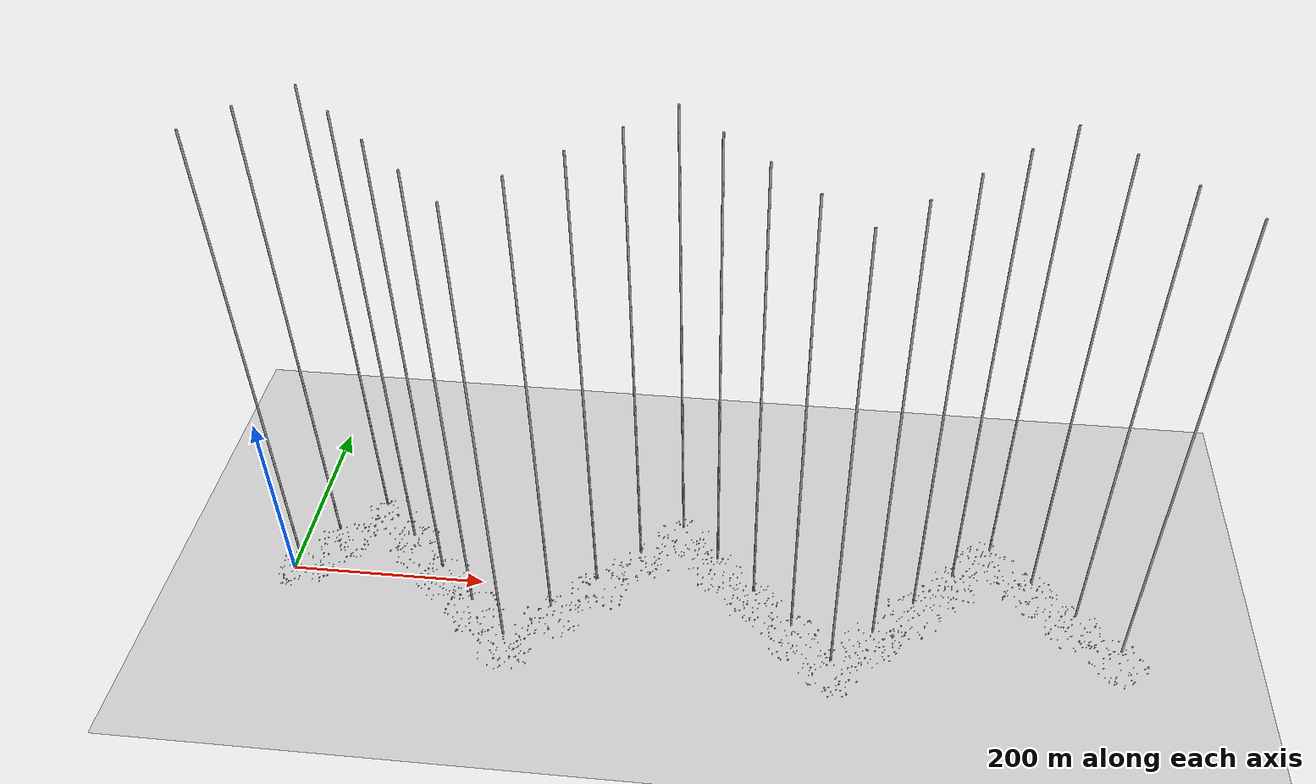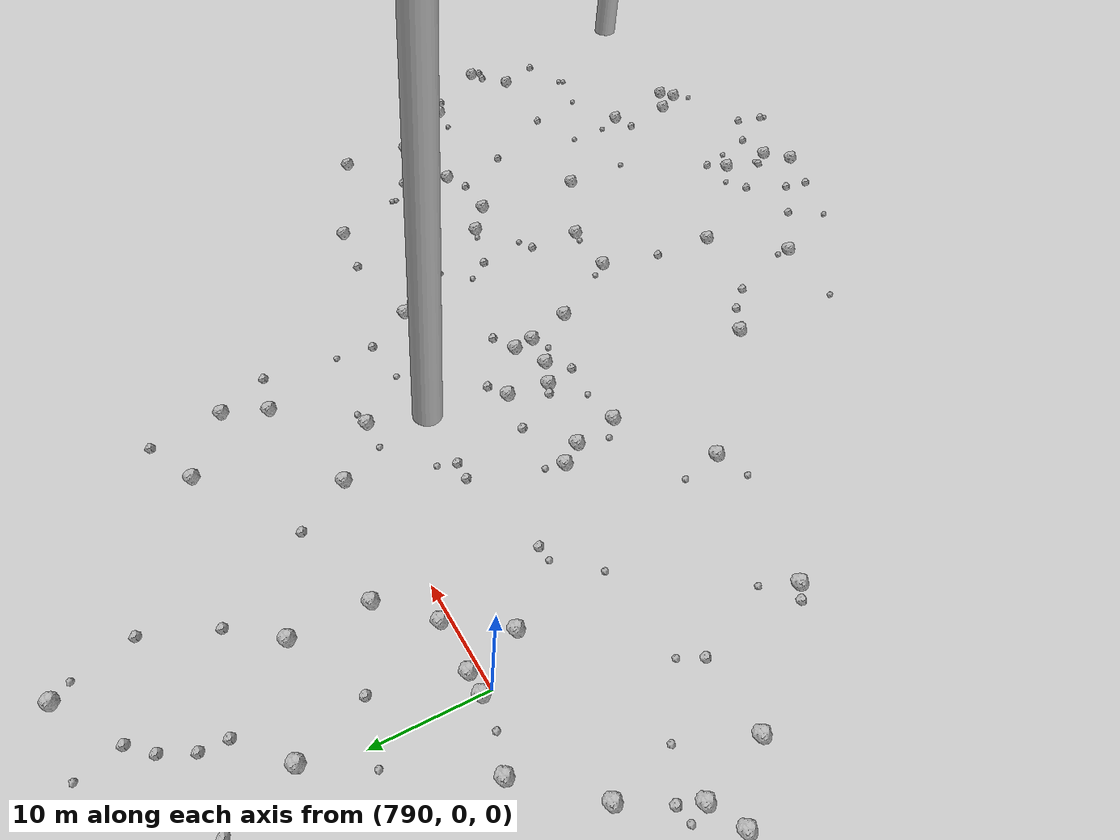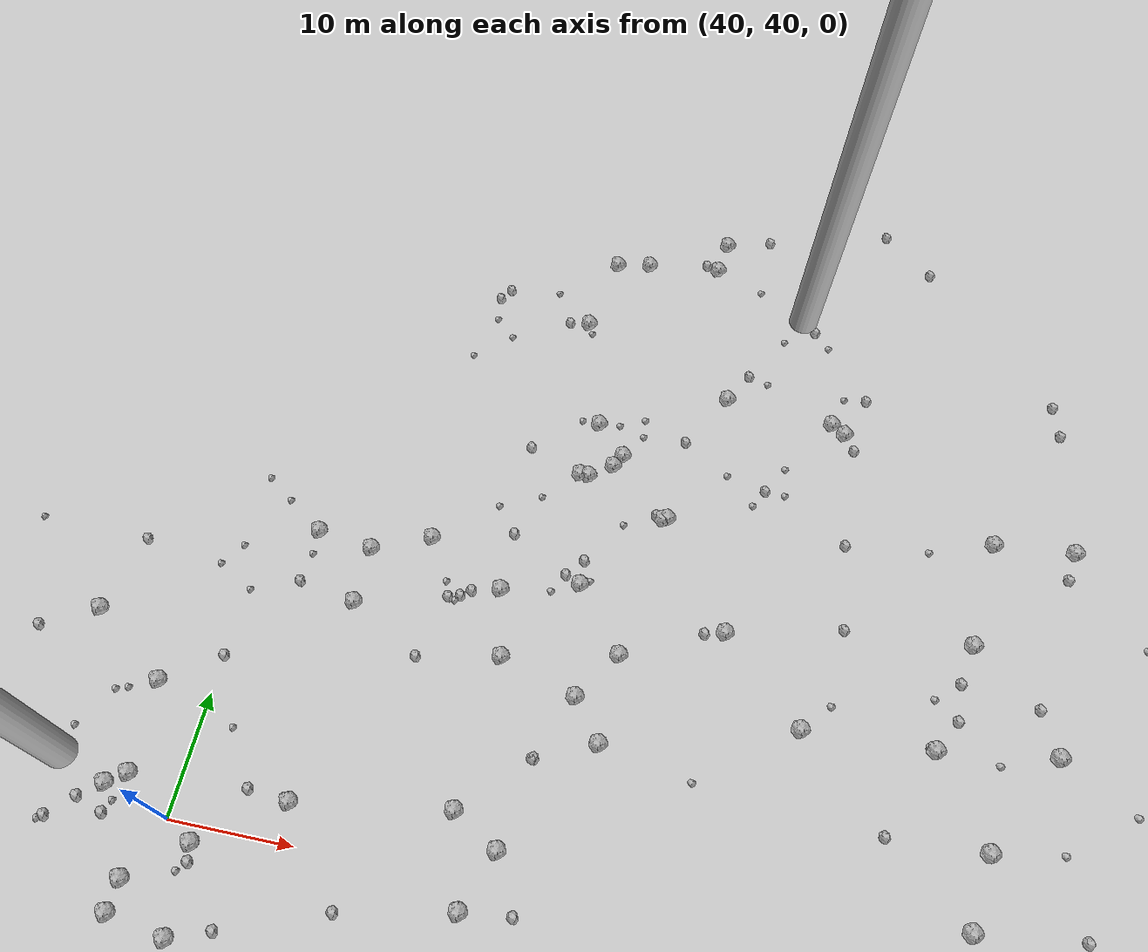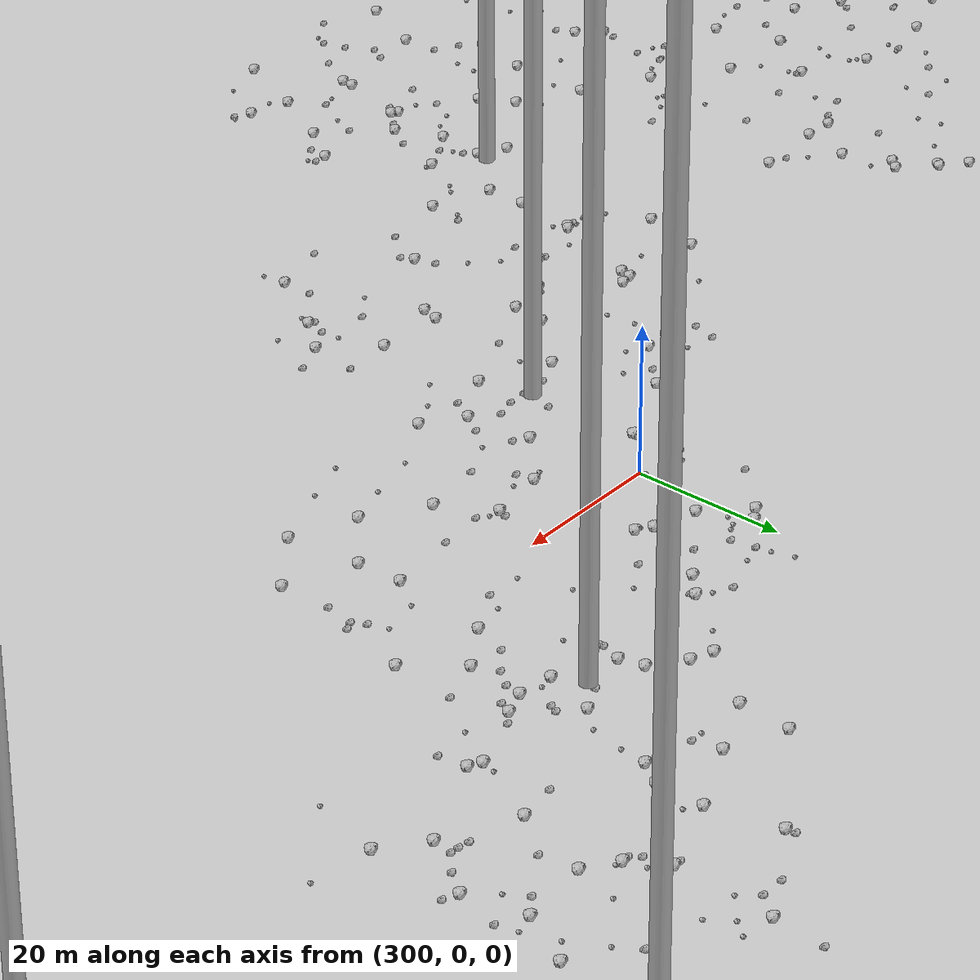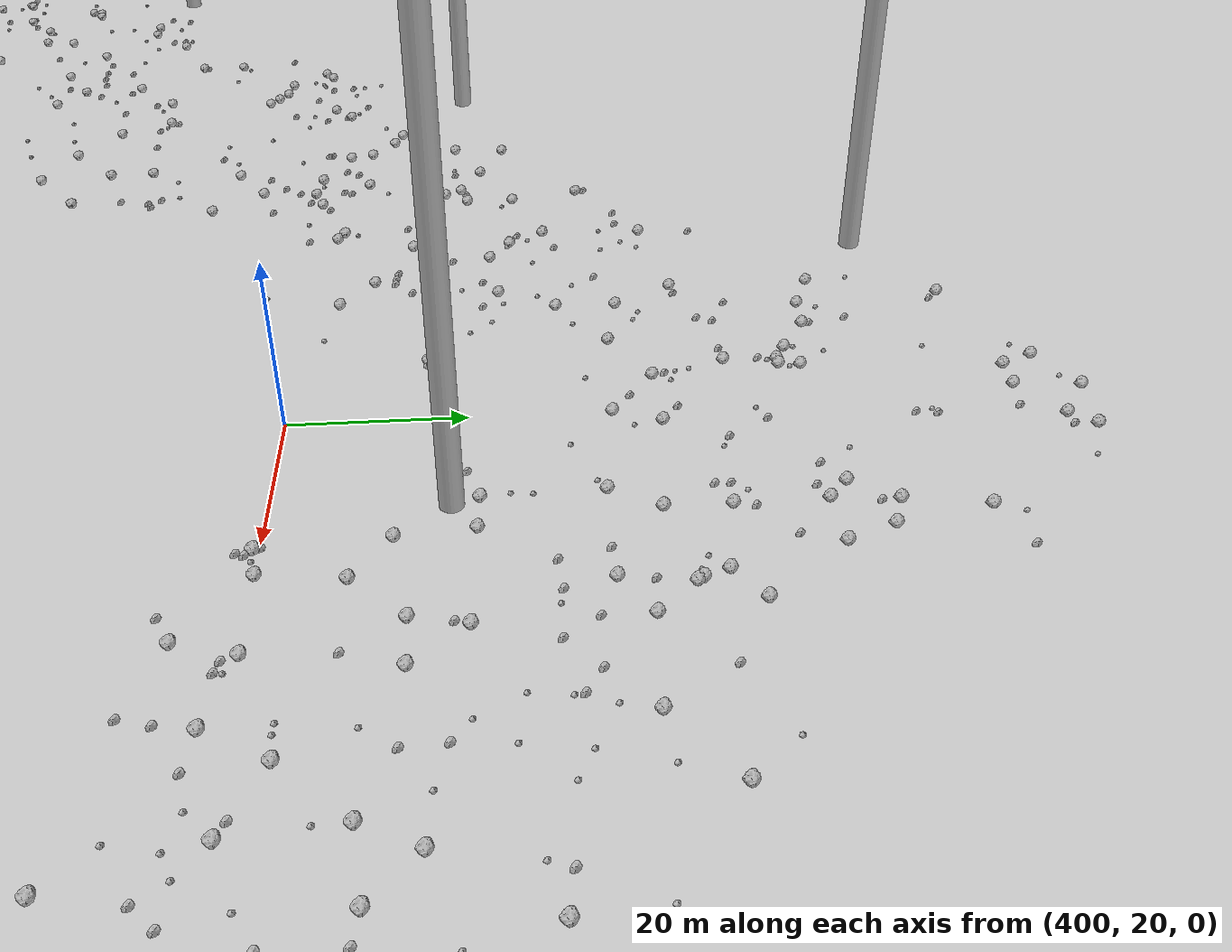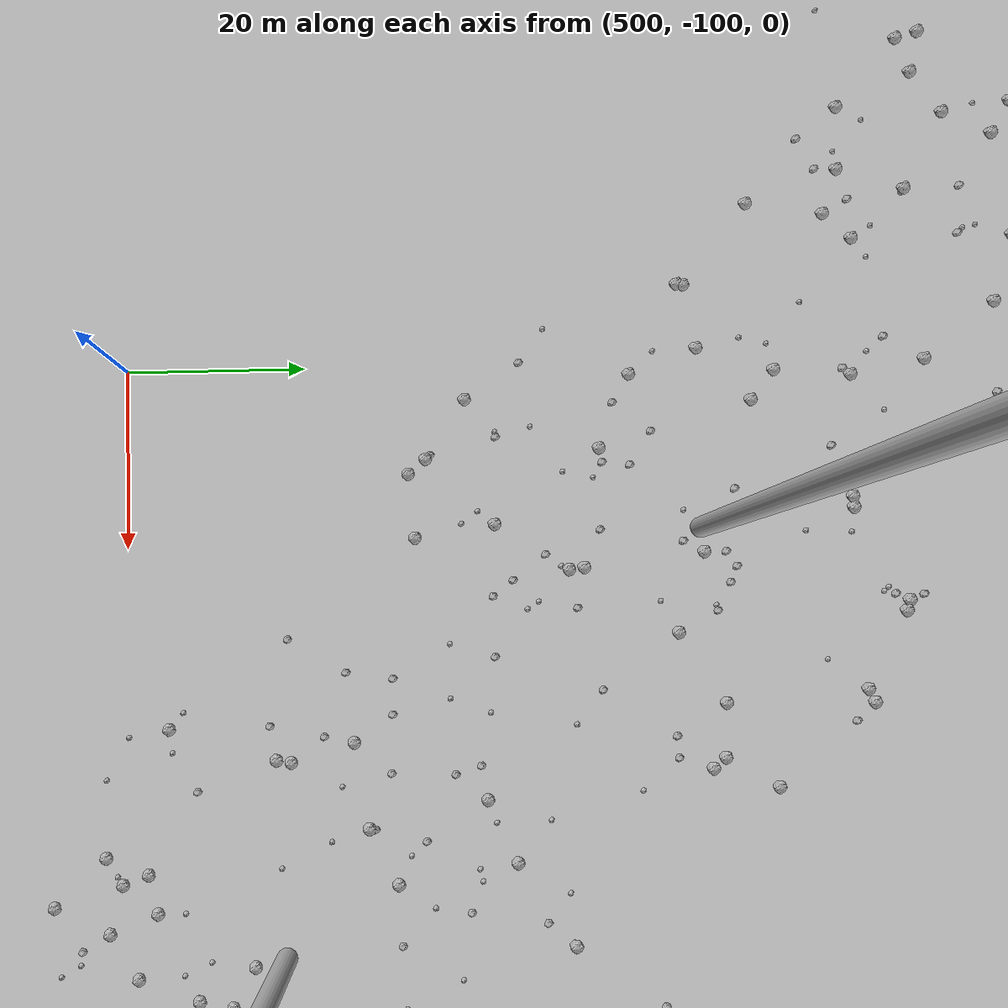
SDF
<sdf version="1.6">
 <world name="default">
  <include><uri>model://custom_ground</uri></include>
  <include><uri>model://sun</uri></include>
  <spherical_coordinates>
   <surface_model>EARTH_WGS84</surface_model>
   <latitude_deg>38.161479</latitude_deg>
   <longitude_deg>-122.454630</longitude_deg>
   <elevation>488.0</elevation>
   <heading_deg>90</heading_deg>
  </spherical_coordinates>
  <model name="rock1_0_0">
   <include><uri>model://rock1</uri><pose>33.48092743309829 -9.326103419252167 0.5 0 0 0</pose></include>
  </model>
  <model name="rock1_0_1">
   <include><uri>model://rock1</uri><pose>29.41898792670245 20.72050995712751 0.5 0 0 0</pose></include>
  </model>
  <model name="rock1_0_2">
   <include><uri>model://rock1</uri><pose>5.54505580973278 3.030387508109463 0.5 0 0 0</pose></include>
  </model>
  <model name="rock1_0_3">
   <include><uri>model://rock1</uri><pose>-0.44001886370844545 -19.751975685549017 0.5 0 0 0</pose></include>
  </model>
  <model name="rock1_0_4">
   <include><uri>model://rock1</uri><pose>24.43688452238456 9.280470032288306 0.5 0 0 0</pose></include>
  </model>
  <model name="rock1_0_5">
   <include><uri>model://rock1</uri><pose>8.508851895517772 -11.911615114221679 0.5 0 0 0</pose></include>
  </model>
  <model name="rock1_0_6">
   <include><uri>model://rock1</uri><pose>3.1789527513600966 26.984004540953734 0.5 0 0 0</pose></include>
  </model>
  <model name="rock1_0_7">
   <include><uri>model://rock1</uri><pose>4.6085433174544335 -16.208655932948037 0.5 0 0 0</pose></include>
  </model>
  <model name="rock1_0_8">
   <include><uri>model://rock1</uri><pose>8.34947680387559 19.332925990894303 0.5 0 0 0</pose></include>
  </model>
  <model name="rock1_0_9">
   <include><uri>model://rock1</uri><pose>39.55571474109297 2.8886161691373786 0.5 0 0 0</pose></include>
  </model>
  <model name="rock1_0_10">
   <include><uri>model://rock1</uri><pose>-7.084247435174213 -16.19274437085252 0.5 0 0 0</pose></include>
  </model>
  <model name="rock1_0_11">
   <include><uri>model://rock1</uri><pose>-11.773809338668856 -0.8835811716899613 0.5 0 0 0</pose></include>
  </model>
  <model name="rock1_0_12">
   <include><uri>model://rock1</uri><pose>3.6131503753311662 -3.449969344255525 0.5 0 0 0</pose></include>
  </model>
  <model name="rock1_0_13">
   <include><uri>model://rock1</uri><pose>37.03922638825003 0.7604099222660494 0.5 0 0 0</pose></include>
  </model>
  <model name="rock1_0_14">
   <include><uri>model://rock1</uri><pose>27.878199747291816 5.879217747921089 0.5 0 0 0</pose></include>
  </model>
  <model name="rock1_0_15">
   <include><uri>model://rock1</uri><pose>23.928897416034943 21.50041570805199 0.5 0 0 0</pose></include>
  </model>
  <model name="rock1_0_16">
   <include><uri>model://rock1</uri><pose>-6.139912296293257 -22.662500574279 0.5 0 0 0</pose></include>
  </model>
  <model name="rock1_0_17">
   <include><uri>model://rock1</uri><pose>25.973974266434226 4.216760661313415 0.5 0 0 0</pose></include>
  </model>
  <model name="rock1_0_18">
   <include><uri>model://rock1</uri><pose>29.506858663661895 -11.951769143263917 0.5 0 0 0</pose></include>
  </model>
  <model name="rock1_0_19">
   <include><uri>model://rock1</uri><pose>-3.336803864472344 -17.949962794252265 0.5 0 0 0</pose></include>
  </model>
  <model name="rock1_0_20">
   <include><uri>model://rock1</uri><pose>-14.768763444629599 14.004524159583411 0.5 0 0 0</pose></include>
  </model>
  <model name="rock1_0_21">
   <include><uri>model://rock1</uri><pose>36.90252615363966 -8.026750581440915 0.5 0 0 0</pose></include>
  </model>
  <model name="rock1_0_22">
   <include><uri>model://rock1</uri><pose>-8.10312503912131 -12.493867934087255 0.5 0 0 0</pose></include>
  </model>
  <model name="rock1_0_23">
   <include><uri>model://rock1</uri><pose>23.576728709797372 -1.7986465078500622 0.5 0 0 0</pose></include>
  </model>
  <model name="rock1_0_24">
   <include><uri>model://rock1</uri><pose>30.935893930030147 -16.87208144167651 0.5 0 0 0</pose></include>
  </model>
  <model name="rock1_0_25">
   <include><uri>model://rock1</uri><pose>-7.419584975284433 -23.632368536258745 0.5 0 0 0</pose></include>
  </model>
  <model name="rock1_0_26">
   <include><uri>model://rock1</uri><pose>-11.386555248476027 14.267519173964786 0.5 0 0 0</pose></include>
  </model>
  <model name="rock2_0_0">
   <include><uri>model://rock2</uri><pose>3.856183961605211 -24.52179467602359 0.3 0 0 0</pose></include>
  </model>
  <model name="rock2_0_1">
   <include><uri>model://rock2</uri><pose>-17.129980434639606 11.375389929515471 0.3 0 0 0</pose></include>
  </model>
  <model name="rock2_0_2">
   <include><uri>model://rock2</uri><pose>1.7780648143428976 -19.130323954198467 0.3 0 0 0</pose></include>
  </model>
  <model name="rock2_0_3">
   <include><uri>model://rock2</uri><pose>-4.985571886803449 20.074585134584503 0.3 0 0 0</pose></include>
  </model>
  <model name="rock2_0_4">
   <include><uri>model://rock2</uri><pose>0.06725853325990983 -12.635762148024593 0.3 0 0 0</pose></include>
  </model>
  <model name="rock2_0_5">
   <include><uri>model://rock2</uri><pose>14.391349566683104 -5.139451082268817 0.3 0 0 0</pose></include>
  </model>
  <model name="rock2_0_6">
   <include><uri>model://rock2</uri><pose>34.04537437319068 -1.853604462604185 0.3 0 0 0</pose></include>
  </model>
  <model name="rock2_0_7">
   <include><uri>model://rock2</uri><pose>21.53213151569495 -7.063517998420068 0.3 0 0 0</pose></include>
  </model>
  <model name="rock2_0_8">
   <include><uri>model://rock2</uri><pose>3.2055942487072357 -4.784607659981106 0.3 0 0 0</pose></include>
  </model>
  <model name="rock2_0_9">
   <include><uri>model://rock2</uri><pose>-2.3080240095491007 -21.002786097367572 0.3 0 0 0</pose></include>
  </model>
  <model name="rock2_0_10">
   <include><uri>model://rock2</uri><pose>13.428080007209509 16.22363177327962 0.3 0 0 0</pose></include>
  </model>
  <model name="rock2_0_11">
   <include><uri>model://rock2</uri><pose>-13.552589573815572 17.84801520114533 0.3 0 0 0</pose></include>
  </model>
  <model name="rock2_0_12">
   <include><uri>model://rock2</uri><pose>27.877873258752864 0.8199212779522895 0.3 0 0 0</pose></include>
  </model>
  <model name="rock2_0_13">
   <include><uri>model://rock2</uri><pose>-14.811091801125308 -1.6173912262203807 0.3 0 0 0</pose></include>
  </model>
  <model name="rock2_0_14">
   <include><uri>model://rock2</uri><pose>19.1782861287991 -18.863439535302355 0.3 0 0 0</pose></include>
  </model>
  <model name="rock2_0_15">
   <include><uri>model://rock2</uri><pose>9.271171397781114 -15.875349443184458 0.3 0 0 0</pose></include>
  </model>
  <model name="rock2_0_16">
   <include><uri>model://rock2</uri><pose>12.631861861594096 -5.649633124707385 0.3 0 0 0</pose></include>
  </model>
  <model name="rock2_0_17">
   <include><uri>model://rock2</uri><pose>25.459748911574714 16.629733225865273 0.3 0 0 0</pose></include>
  </model>
  <model name="rock2_0_18">
   <include><uri>model://rock2</uri><pose>14.758377830095796 0.7602927908935655 0.3 0 0 0</pose></include>
  </model>
  <model name="rock2_0_19">
   <include><uri>model://rock2</uri><pose>26.70533870843707 -6.98418508004578 0.3 0 0 0</pose></include>
  </model>
  <model name="rock2_0_20">
   <include><uri>model://rock2</uri><pose>-10.463003240104216 8.777390612806968 0.3 0 0 0</pose></include>
  </model>
  <model name="rock2_0_21">
   <include><uri>model://rock2</uri><pose>-3.552243768312021 2.369402986216535 0.3 0 0 0</pose></include>
  </model>
  <model name="rock2_0_22">
   <include><uri>model://rock2</uri><pose>0.18056775331650954 22.09771925945536 0.3 0 0 0</pose></include>
  </model>
  <model name="rock2_0_23">
   <include><uri>model://rock2</uri><pose>-1.6159806842486617 -6.0261118167477825 0.3 0 0 0</pose></include>
  </model>
  <model name="rock2_0_24">
   <include><uri>model://rock2</uri><pose>-6.095911497279028 2.0232586297049977 0.3 0 0 0</pose></include>
  </model>
  <model name="rock2_0_25">
   <include><uri>model://rock2</uri><pose>-2.76170540629327 20.787121341111607 0.3 0 0 0</pose></include>
  </model>
  <model name="rock2_0_26">
   <include><uri>model://rock2</uri><pose>-9.507682121175288 -10.664804248338545 0.3 0 0 0</pose></include>
  </model>
  <model name="rock3_0_0">
   <include><uri>model://rock3</uri><pose>13.557309236497481 18.733771688179274 0.2 0 0 0</pose></include>
  </model>
  <model name="rock3_0_1">
   <include><uri>model://rock3</uri><pose>38.624749426703794 7.522688702360888 0.2 0 0 0</pose></include>
  </model>
  <model name="rock3_0_2">
   <include><uri>model://rock3</uri><pose>21.42893682527533 -2.5224101579158607 0.2 0 0 0</pose></include>
  </model>
  <model name="rock3_0_3">
   <include><uri>model://rock3</uri><pose>16.436359706322683 -26.2861256276555 0.2 0 0 0</pose></include>
  </model>
  <model name="rock3_0_4">
   <include><uri>model://rock3</uri><pose>-12.944114929940682 -2.7948187674281364 0.2 0 0 0</pose></include>
  </model>
  <model name="rock3_0_5">
   <include><uri>model://rock3</uri><pose>-13.764761837583592 -10.98692275377941 0.2 0 0 0</pose></include>
  </model>
  <model name="rock3_0_6">
   <include><uri>model://rock3</uri><pose>-5.268484073442327 0.5925161183612175 0.2 0 0 0</pose></include>
  </model>
  <model name="rock3_0_7">
   <include><uri>model://rock3</uri><pose>24.84276680217546 -2.359306376881232 0.2 0 0 0</pose></include>
  </model>
  <model name="rock3_0_8">
   <include><uri>model://rock3</uri><pose>37.99546936893786 -9.425436087733825 0.2 0 0 0</pose></include>
  </model>
  <model name="rock3_0_9">
   <include><uri>model://rock3</uri><pose>-2.1337440070809386 -23.565634814952503 0.2 0 0 0</pose></include>
  </model>
  <model name="rock3_0_10">
   <include><uri>model://rock3</uri><pose>-1.0748507359936426 -12.778419800932856 0.2 0 0 0</pose></include>
  </model>
  <model name="rock3_0_11">
   <include><uri>model://rock3</uri><pose>18.733963734465966 19.199043795800215 0.2 0 0 0</pose></include>
  </model>
  <model name="rock3_0_12">
   <include><uri>model://rock3</uri><pose>23.568870495914638 11.470884295731075 0.2 0 0 0</pose></include>
  </model>
  <model name="rock3_0_13">
   <include><uri>model://rock3</uri><pose>14.906823991482703 -11.308176522324217 0.2 0 0 0</pose></include>
  </model>
  <model name="rock3_0_14">
   <include><uri>model://rock3</uri><pose>6.724894354765507 -26.674107705933785 0.2 0 0 0</pose></include>
  </model>
  <model name="rock3_0_15">
   <include><uri>model://rock3</uri><pose>19.21341383026926 -21.026838238077637 0.2 0 0 0</pose></include>
  </model>
  <model name="rock3_0_16">
   <include><uri>model://rock3</uri><pose>19.786040521637744 26.766428226359245 0.2 0 0 0</pose></include>
  </model>
  <model name="rock3_0_17">
   <include><uri>model://rock3</uri><pose>18.43077672378996 20.01313771636847 0.2 0 0 0</pose></include>
  </model>
  <model name="rock3_0_18">
   <include><uri>model://rock3</uri><pose>-13.92570973501247 7.908467774298373 0.2 0 0 0</pose></include>
  </model>
  <model name="rock3_0_19">
   <include><uri>model://rock3</uri><pose>33.632026298178296 8.936156709410163 0.2 0 0 0</pose></include>
  </model>
  <model name="rock3_0_20">
   <include><uri>model://rock3</uri><pose>3.7938730724291645 25.745785856147556 0.2 0 0 0</pose></include>
  </model>
  <model name="rock3_0_21">
   <include><uri>model://rock3</uri><pose>6.755385188800027 -18.73220762039758 0.2 0 0 0</pose></include>
  </model>
  <model name="rock3_0_22">
   <include><uri>model://rock3</uri><pose>9.380025160656007 -9.18740471086534 0.2 0 0 0</pose></include>
  </model>
  <model name="rock3_0_23">
   <include><uri>model://rock3</uri><pose>22.974059545347842 -14.386420150086776 0.2 0 0 0</pose></include>
  </model>
  <model name="rock3_0_24">
   <include><uri>model://rock3</uri><pose>9.713197362886152 23.95782861153654 0.2 0 0 0</pose></include>
  </model>
  <model name="rock3_0_25">
   <include><uri>model://rock3</uri><pose>14.236827425444929 14.691360609893756 0.2 0 0 0</pose></include>
  </model>
  <model name="rock3_0_26">
   <include><uri>model://rock3</uri><pose>19.83286742883363 5.7080964843669335 0.2 0 0 0</pose></include>
  </model>
  <model name="rock1_1_0">
   <include><uri>model://rock1</uri><pose>15.201782637358834 51.687279839996975 0.5 0 0 0</pose></include>
  </model>
  <model name="rock1_1_1">
   <include><uri>model://rock1</uri><pose>48.68951556012089 43.06797758096176 0.5 0 0 0</pose></include>
  </model>
  <model name="rock1_1_2">
   <include><uri>model://rock1</uri><pose>21.25273858738795 34.86423386471786 0.5 0 0 0</pose></include>
  </model>
  <model name="rock1_1_3">
   <include><uri>model://rock1</uri><pose>45.257503321219346 28.084638263773606 0.5 0 0 0</pose></include>
  </model>
  <model name="rock1_1_4">
   <include><uri>model://rock1</uri><pose>34.504510621250056 41.67193135362246 0.5 0 0 0</pose></include>
  </model>
  <model name="rock1_1_5">
   <include><uri>model://rock1</uri><pose>35.99955613792379 42.733493787030916 0.5 0 0 0</pose></include>
  </model>
  <model name="rock1_1_6">
   <include><uri>model://rock1</uri><pose>49.33674534151462 19.207980457128077 0.5 0 0 0</pose></include>
  </model>
  <model name="rock1_1_7">
   <include><uri>model://rock1</uri><pose>13.449283633083873 39.254305145144585 0.5 0 0 0</pose></include>
  </model>
  <model name="rock1_1_8">
   <include><uri>model://rock1</uri><pose>44.29885946429727 65.38303876582549 0.5 0 0 0</pose></include>
  </model>
  <model name="rock1_1_9">
   <include><uri>model://rock1</uri><pose>22.067710093069707 43.9850550592285 0.5 0 0 0</pose></include>
  </model>
  <model name="rock1_1_10">
   <include><uri>model://rock1</uri><pose>42.44239313820926 38.731811155667245 0.5 0 0 0</pose></include>
  </model>
  <model name="rock1_1_11">
   <include><uri>model://rock1</uri><pose>35.60226843339956 50.169815724011634 0.5 0 0 0</pose></include>
  </model>
  <model name="rock1_1_12">
   <include><uri>model://rock1</uri><pose>56.92757123330138 29.941005188112868 0.5 0 0 0</pose></include>
  </model>
  <model name="rock1_1_13">
   <include><uri>model://rock1</uri><pose>18.82572643248499 41.81324304191703 0.5 0 0 0</pose></include>
  </model>
  <model name="rock1_1_14">
   <include><uri>model://rock1</uri><pose>40.716621382858676 27.820324169666378 0.5 0 0 0</pose></include>
  </model>
  <model name="rock1_1_15">
   <include><uri>model://rock1</uri><pose>63.09263849702173 31.173206885931325 0.5 0 0 0</pose></include>
  </model>
  <model name="rock1_1_16">
   <include><uri>model://rock1</uri><pose>53.31764836483997 20.5170353023618 0.5 0 0 0</pose></include>
  </model>
  <model name="rock1_1_17">
   <include><uri>model://rock1</uri><pose>49.063844746298074 64.67802788537864 0.5 0 0 0</pose></include>
  </model>
  <model name="rock1_1_18">
   <include><uri>model://rock1</uri><pose>38.159128179108734 32.85504200838809 0.5 0 0 0</pose></include>
  </model>
  <model name="rock1_1_19">
   <include><uri>model://rock1</uri><pose>49.00192062344014 12.192293430761074 0.5 0 0 0</pose></include>
  </model>
  <model name="rock1_1_20">
   <include><uri>model://rock1</uri><pose>38.27788726633359 35.29102985932991 0.5 0 0 0</pose></include>
  </model>
  <model name="rock1_1_21">
   <include><uri>model://rock1</uri><pose>42.92448228024235 32.03390968262447 0.5 0 0 0</pose></include>
  </model>
  <model name="rock1_1_22">
   <include><uri>model://rock1</uri><pose>64.89502852663492 42.69745454653821 0.5 0 0 0</pose></include>
  </model>
  <model name="rock1_1_23">
   <include><uri>model://rock1</uri><pose>63.11144622513975 37.94776499692787 0.5 0 0 0</pose></include>
  </model>
  <model name="rock1_1_24">
   <include><uri>model://rock1</uri><pose>61.0943750854297 44.941646899439775 0.5 0 0 0</pose></include>
  </model>
  <model name="rock1_1_25">
   <include><uri>model://rock1</uri><pose>28.71183705711725 55.07118862108239 0.5 0 0 0</pose></include>
  </model>
  <model name="rock1_1_26">
   <include><uri>model://rock1</uri><pose>48.95557177724747 59.73464562360361 0.5 0 0 0</pose></include>
  </model>
  <model name="rock2_1_0">
   <include><uri>model://rock2</uri><pose>45.31386620943864 43.402756393297295 0.3 0 0 0</pose></include>
  </model>
  <model name="rock2_1_1">
   <include><uri>model://rock2</uri><pose>23.775438574199917 35.07873631326571 0.3 0 0 0</pose></include>
  </model>
  <model name="rock2_1_2">
   <include><uri>model://rock2</uri><pose>66.27663984431179 32.19518157015626 0.3 0 0 0</pose></include>
  </model>
  <model name="rock2_1_3">
   <include><uri>model://rock2</uri><pose>24.281078015469753 52.73739773201353 0.3 0 0 0</pose></include>
  </model>
  <model name="rock2_1_4">
   <include><uri>model://rock2</uri><pose>42.65928942065328 37.39370900622414 0.3 0 0 0</pose></include>
  </model>
  <model name="rock2_1_5">
   <include><uri>model://rock2</uri><pose>59.337794299252174 20.041531248316584 0.3 0 0 0</pose></include>
  </model>
  <model name="rock2_1_6">
   <include><uri>model://rock2</uri><pose>54.30246797247377 25.56441782791584 0.3 0 0 0</pose></include>
  </model>
  <model name="rock2_1_7">
   <include><uri>model://rock2</uri><pose>56.42557251519128 61.756011813790366 0.3 0 0 0</pose></include>
  </model>
  <model name="rock2_1_8">
   <include><uri>model://rock2</uri><pose>18.245220371006727 30.435867044915533 0.3 0 0 0</pose></include>
  </model>
  <model name="rock2_1_9">
   <include><uri>model://rock2</uri><pose>44.02779505577899 60.675458516926376 0.3 0 0 0</pose></include>
  </model>
  <model name="rock2_1_10">
   <include><uri>model://rock2</uri><pose>35.03929728231165 39.511218719428264 0.3 0 0 0</pose></include>
  </model>
  <model name="rock2_1_11">
   <include><uri>model://rock2</uri><pose>66.13665004200607 50.024287749156244 0.3 0 0 0</pose></include>
  </model>
  <model name="rock2_1_12">
   <include><uri>model://rock2</uri><pose>52.97039279460146 23.696737115741055 0.3 0 0 0</pose></include>
  </model>
  <model name="rock2_1_13">
   <include><uri>model://rock2</uri><pose>30.81546043531067 38.48659917131552 0.3 0 0 0</pose></include>
  </model>
  <model name="rock2_1_14">
   <include><uri>model://rock2</uri><pose>46.08811282443178 33.180939474966706 0.3 0 0 0</pose></include>
  </model>
  <model name="rock2_1_15">
   <include><uri>model://rock2</uri><pose>55.09866640600026 56.20090863836607 0.3 0 0 0</pose></include>
  </model>
  <model name="rock2_1_16">
   <include><uri>model://rock2</uri><pose>32.698150643536884 40.32433410835351 0.3 0 0 0</pose></include>
  </model>
  <model name="rock2_1_17">
   <include><uri>model://rock2</uri><pose>63.548074601120476 21.564069467787732 0.3 0 0 0</pose></include>
  </model>
  <model name="rock2_1_18">
   <include><uri>model://rock2</uri><pose>19.947059862170004 51.1232724005893 0.3 0 0 0</pose></include>
  </model>
  <model name="rock2_1_19">
   <include><uri>model://rock2</uri><pose>54.17632181510548 36.11703526989457 0.3 0 0 0</pose></include>
  </model>
  <model name="rock2_1_20">
   <include><uri>model://rock2</uri><pose>39.998202814110456 53.21097545828455 0.3 0 0 0</pose></include>
  </model>
  <model name="rock2_1_21">
   <include><uri>model://rock2</uri><pose>43.589661135035065 10.88944500866731 0.3 0 0 0</pose></include>
  </model>
  <model name="rock2_1_22">
   <include><uri>model://rock2</uri><pose>66.03282806958288 49.94663419652029 0.3 0 0 0</pose></include>
  </model>
  <model name="rock2_1_23">
   <include><uri>model://rock2</uri><pose>58.21372744229747 62.654488219755976 0.3 0 0 0</pose></include>
  </model>
  <model name="rock2_1_24">
   <include><uri>model://rock2</uri><pose>61.23770771147407 31.968992526354477 0.3 0 0 0</pose></include>
  </model>
  <model name="rock2_1_25">
   <include><uri>model://rock2</uri><pose>30.22003696511873 61.81299019545739 0.3 0 0 0</pose></include>
  </model>
  <model name="rock2_1_26">
   <include><uri>model://rock2</uri><pose>67.04791260875609 38.39431440719895 0.3 0 0 0</pose></include>
  </model>
  <model name="rock3_1_0">
   <include><uri>model://rock3</uri><pose>60.623406642537844 20.080020926771184 0.2 0 0 0</pose></include>
  </model>
  <model name="rock3_1_1">
   <include><uri>model://rock3</uri><pose>23.90312728362436 27.991306533890302 0.2 0 0 0</pose></include>
  </model>
  <model name="rock3_1_2">
   <include><uri>model://rock3</uri><pose>17.07050577825122 27.444030371227903 0.2 0 0 0</pose></include>
  </model>
  <model name="rock3_1_3">
   <include><uri>model://rock3</uri><pose>28.245113717300484 35.62309471519597 0.2 0 0 0</pose></include>
  </model>
  <model name="rock3_1_4">
   <include><uri>model://rock3</uri><pose>40.949522332325294 67.75007102599062 0.2 0 0 0</pose></include>
  </model>
  <model name="rock3_1_5">
   <include><uri>model://rock3</uri><pose>35.442977398640046 40.51017242041465 0.2 0 0 0</pose></include>
  </model>
  <model name="rock3_1_6">
   <include><uri>model://rock3</uri><pose>32.41782592770855 48.83088933075982 0.2 0 0 0</pose></include>
  </model>
  <model name="rock3_1_7">
   <include><uri>model://rock3</uri><pose>56.07389073189007 21.30792081583449 0.2 0 0 0</pose></include>
  </model>
  <model name="rock3_1_8">
   <include><uri>model://rock3</uri><pose>59.102319343104085 28.780911458247076 0.2 0 0 0</pose></include>
  </model>
  <model name="rock3_1_9">
   <include><uri>model://rock3</uri><pose>30.367431669057186 45.450572462559855 0.2 0 0 0</pose></include>
  </model>
  <model name="rock3_1_10">
   <include><uri>model://rock3</uri><pose>41.995087750559975 36.57373427729219 0.2 0 0 0</pose></include>
  </model>
  <model name="rock3_1_11">
   <include><uri>model://rock3</uri><pose>18.096165758970706 33.16470843178753 0.2 0 0 0</pose></include>
  </model>
  <model name="rock3_1_12">
   <include><uri>model://rock3</uri><pose>57.03147643736506 61.528655796433554 0.2 0 0 0</pose></include>
  </model>
  <model name="rock3_1_13">
   <include><uri>model://rock3</uri><pose>20.675366434749606 62.07372970641956 0.2 0 0 0</pose></include>
  </model>
  <model name="rock3_1_14">
   <include><uri>model://rock3</uri><pose>37.012636611291114 60.88344486000595 0.2 0 0 0</pose></include>
  </model>
  <model name="rock3_1_15">
   <include><uri>model://rock3</uri><pose>38.39384063915284 62.85489110962 0.2 0 0 0</pose></include>
  </model>
  <model name="rock3_1_16">
   <include><uri>model://rock3</uri><pose>66.00034736940933 31.59467191507128 0.2 0 0 0</pose></include>
  </model>
  <model name="rock3_1_17">
   <include><uri>model://rock3</uri><pose>38.59591232926876 69.49946970110028 0.2 0 0 0</pose></include>
  </model>
  <model name="rock3_1_18">
   <include><uri>model://rock3</uri><pose>33.37062301364642 49.1526467436246 0.2 0 0 0</pose></include>
  </model>
  <model name="rock3_1_19">
   <include><uri>model://rock3</uri><pose>40.175877184226195 59.099129347722155 0.2 0 0 0</pose></include>
  </model>
  <model name="rock3_1_20">
   <include><uri>model://rock3</uri><pose>42.590615715673486 47.67947409978066 0.2 0 0 0</pose></include>
  </model>
  <model name="rock3_1_21">
   <include><uri>model://rock3</uri><pose>30.348770249976564 38.12056660722261 0.2 0 0 0</pose></include>
  </model>
  <model name="rock3_1_22">
   <include><uri>model://rock3</uri><pose>16.500843897652295 23.392993378337685 0.2 0 0 0</pose></include>
  </model>
  <model name="rock3_1_23">
   <include><uri>model://rock3</uri><pose>17.278194036115107 39.63231348246575 0.2 0 0 0</pose></include>
  </model>
  <model name="rock3_1_24">
   <include><uri>model://rock3</uri><pose>55.961521894635865 63.04415466792232 0.2 0 0 0</pose></include>
  </model>
  <model name="rock3_1_25">
   <include><uri>model://rock3</uri><pose>29.317585978303363 30.96440310054578 0.2 0 0 0</pose></include>
  </model>
  <model name="rock3_1_26">
   <include><uri>model://rock3</uri><pose>44.30515786994342 63.248300288652665 0.2 0 0 0</pose></include>
  </model>
  <model name="rock1_2_0">
   <include><uri>model://rock1</uri><pose>64.30407078018501 98.60476406584336 0.5 0 0 0</pose></include>
  </model>
  <model name="rock1_2_1">
   <include><uri>model://rock1</uri><pose>107.30845329329023 75.9605222944142 0.5 0 0 0</pose></include>
  </model>
  <model name="rock1_2_2">
   <include><uri>model://rock1</uri><pose>65.74914857879506 75.21241244513814 0.5 0 0 0</pose></include>
  </model>
  <model name="rock1_2_3">
   <include><uri>model://rock1</uri><pose>99.12588876572171 65.96727669892921 0.5 0 0 0</pose></include>
  </model>
  <model name="rock1_2_4">
   <include><uri>model://rock1</uri><pose>71.15591069172632 59.52807659153672 0.5 0 0 0</pose></include>
  </model>
  <model name="rock1_2_5">
   <include><uri>model://rock1</uri><pose>73.11878406067413 72.40408156489036 0.5 0 0 0</pose></include>
  </model>
  <model name="rock1_2_6">
   <include><uri>model://rock1</uri><pose>60.57309636210096 63.201111804405755 0.5 0 0 0</pose></include>
  </model>
  <model name="rock1_2_7">
   <include><uri>model://rock1</uri><pose>67.32235079840224 99.15896206342504 0.5 0 0 0</pose></include>
  </model>
  <model name="rock1_2_8">
   <include><uri>model://rock1</uri><pose>74.41864370414524 103.0844299678144 0.5 0 0 0</pose></include>
  </model>
  <model name="rock1_2_9">
   <include><uri>model://rock1</uri><pose>67.6884636387029 76.57376945227873 0.5 0 0 0</pose></include>
  </model>
  <model name="rock1_2_10">
   <include><uri>model://rock1</uri><pose>86.09126533518355 56.303992521601245 0.5 0 0 0</pose></include>
  </model>
  <model name="rock1_2_11">
   <include><uri>model://rock1</uri><pose>68.34582418900737 77.73693529863645 0.5 0 0 0</pose></include>
  </model>
  <model name="rock1_2_12">
   <include><uri>model://rock1</uri><pose>53.85616494356449 66.66530404862637 0.5 0 0 0</pose></include>
  </model>
  <model name="rock1_2_13">
   <include><uri>model://rock1</uri><pose>76.63087576407244 85.3966740465864 0.5 0 0 0</pose></include>
  </model>
  <model name="rock1_2_14">
   <include><uri>model://rock1</uri><pose>100.57213574684091 75.40734384305175 0.5 0 0 0</pose></include>
  </model>
  <model name="rock1_2_15">
   <include><uri>model://rock1</uri><pose>61.88167974081021 57.513073458160164 0.5 0 0 0</pose></include>
  </model>
  <model name="rock1_2_16">
   <include><uri>model://rock1</uri><pose>73.88665763563256 99.86689156996724 0.5 0 0 0</pose></include>
  </model>
  <model name="rock1_2_17">
   <include><uri>model://rock1</uri><pose>64.98987222542208 75.21694762986273 0.5 0 0 0</pose></include>
  </model>
  <model name="rock1_2_18">
   <include><uri>model://rock1</uri><pose>65.72578246863304 80.5370607708017 0.5 0 0 0</pose></include>
  </model>
  <model name="rock1_2_19">
   <include><uri>model://rock1</uri><pose>72.79140619842941 72.24946224819531 0.5 0 0 0</pose></include>
  </model>
  <model name="rock1_2_20">
   <include><uri>model://rock1</uri><pose>68.35717734411692 55.42720865410902 0.5 0 0 0</pose></include>
  </model>
  <model name="rock1_2_21">
   <include><uri>model://rock1</uri><pose>86.12185556684395 84.62178525824424 0.5 0 0 0</pose></include>
  </model>
  <model name="rock1_2_22">
   <include><uri>model://rock1</uri><pose>70.836232487524 52.082456926573435 0.5 0 0 0</pose></include>
  </model>
  <model name="rock1_2_23">
   <include><uri>model://rock1</uri><pose>87.32183217449781 83.78784350592085 0.5 0 0 0</pose></include>
  </model>
  <model name="rock1_2_24">
   <include><uri>model://rock1</uri><pose>79.30012147756673 63.0995301496761 0.5 0 0 0</pose></include>
  </model>
  <model name="rock1_2_25">
   <include><uri>model://rock1</uri><pose>66.94183976590585 64.95407586322318 0.5 0 0 0</pose></include>
  </model>
  <model name="rock1_2_26">
   <include><uri>model://rock1</uri><pose>62.829884647038305 91.17615826208107 0.5 0 0 0</pose></include>
  </model>
  <model name="rock2_2_0">
   <include><uri>model://rock2</uri><pose>72.14025793314146 72.54740794090424 0.3 0 0 0</pose></include>
  </model>
  <model name="rock2_2_1">
   <include><uri>model://rock2</uri><pose>66.88168194425151 67.15149068835517 0.3 0 0 0</pose></include>
  </model>
  <model name="rock2_2_2">
   <include><uri>model://rock2</uri><pose>89.60419025753492 107.29923027401009 0.3 0 0 0</pose></include>
  </model>
  <model name="rock2_2_3">
   <include><uri>model://rock2</uri><pose>88.96122209992942 87.75085400774365 0.3 0 0 0</pose></include>
  </model>
  <model name="rock2_2_4">
   <include><uri>model://rock2</uri><pose>106.17178684771145 87.46298829459059 0.3 0 0 0</pose></include>
  </model>
  <model name="rock2_2_5">
   <include><uri>model://rock2</uri><pose>83.745020067439 94.45620190046182 0.3 0 0 0</pose></include>
  </model>
  <model name="rock2_2_6">
   <include><uri>model://rock2</uri><pose>78.26526599688285 88.331790353449 0.3 0 0 0</pose></include>
  </model>
  <model name="rock2_2_7">
   <include><uri>model://rock2</uri><pose>93.98971603062395 103.39153572678549 0.3 0 0 0</pose></include>
  </model>
  <model name="rock2_2_8">
   <include><uri>model://rock2</uri><pose>106.76345287206937 73.42499575754485 0.3 0 0 0</pose></include>
  </model>
  <model name="rock2_2_9">
   <include><uri>model://rock2</uri><pose>88.25755211994502 72.8970302035855 0.3 0 0 0</pose></include>
  </model>
  <model name="rock2_2_10">
   <include><uri>model://rock2</uri><pose>88.76694981152087 65.27827613921097 0.3 0 0 0</pose></include>
  </model>
  <model name="rock2_2_11">
   <include><uri>model://rock2</uri><pose>105.51010881543777 90.38174035185571 0.3 0 0 0</pose></include>
  </model>
  <model name="rock2_2_12">
   <include><uri>model://rock2</uri><pose>65.59122069857861 65.6018993369138 0.3 0 0 0</pose></include>
  </model>
  <model name="rock2_2_13">
   <include><uri>model://rock2</uri><pose>54.79885607258839 93.66330421444152 0.3 0 0 0</pose></include>
  </model>
  <model name="rock2_2_14">
   <include><uri>model://rock2</uri><pose>57.40108915940022 62.0517873190974 0.3 0 0 0</pose></include>
  </model>
  <model name="rock2_2_15">
   <include><uri>model://rock2</uri><pose>61.0477607740941 91.0323116861307 0.3 0 0 0</pose></include>
  </model>
  <model name="rock2_2_16">
   <include><uri>model://rock2</uri><pose>81.0281952314412 76.75040786237017 0.3 0 0 0</pose></include>
  </model>
  <model name="rock2_2_17">
   <include><uri>model://rock2</uri><pose>60.58882310208155 68.4408939276417 0.3 0 0 0</pose></include>
  </model>
  <model name="rock2_2_18">
   <include><uri>model://rock2</uri><pose>77.64862398020729 62.71054946345584 0.3 0 0 0</pose></include>
  </model>
  <model name="rock2_2_19">
   <include><uri>model://rock2</uri><pose>60.287875144866774 77.03450216309042 0.3 0 0 0</pose></include>
  </model>
  <model name="rock2_2_20">
   <include><uri>model://rock2</uri><pose>73.56485997260391 80.24328648592622 0.3 0 0 0</pose></include>
  </model>
  <model name="rock2_2_21">
   <include><uri>model://rock2</uri><pose>98.27042504343308 62.55447899512171 0.3 0 0 0</pose></include>
  </model>
  <model name="rock2_2_22">
   <include><uri>model://rock2</uri><pose>67.05655226547213 99.37619291986334 0.3 0 0 0</pose></include>
  </model>
  <model name="rock2_2_23">
   <include><uri>model://rock2</uri><pose>72.74309780721953 100.34658994589091 0.3 0 0 0</pose></include>
  </model>
  <model name="rock2_2_24">
   <include><uri>model://rock2</uri><pose>78.44991621422682 104.33051948998678 0.3 0 0 0</pose></include>
  </model>
  <model name="rock2_2_25">
   <include><uri>model://rock2</uri><pose>54.01315700621806 92.52602047153083 0.3 0 0 0</pose></include>
  </model>
  <model name="rock2_2_26">
   <include><uri>model://rock2</uri><pose>88.26941818023795 82.34063523202917 0.3 0 0 0</pose></include>
  </model>
  <model name="rock3_2_0">
   <include><uri>model://rock3</uri><pose>59.37919943817324 94.18325063271107 0.2 0 0 0</pose></include>
  </model>
  <model name="rock3_2_1">
   <include><uri>model://rock3</uri><pose>64.18731778232723 80.6484782117813 0.2 0 0 0</pose></include>
  </model>
  <model name="rock3_2_2">
   <include><uri>model://rock3</uri><pose>77.61784343113794 77.60947817357079 0.2 0 0 0</pose></include>
  </model>
  <model name="rock3_2_3">
   <include><uri>model://rock3</uri><pose>69.81811966269962 80.02305234073994 0.2 0 0 0</pose></include>
  </model>
  <model name="rock3_2_4">
   <include><uri>model://rock3</uri><pose>96.27601634713267 60.828794189494346 0.2 0 0 0</pose></include>
  </model>
  <model name="rock3_2_5">
   <include><uri>model://rock3</uri><pose>69.53559018444535 71.09017305892186 0.2 0 0 0</pose></include>
  </model>
  <model name="rock3_2_6">
   <include><uri>model://rock3</uri><pose>63.279906968246465 90.17003999759041 0.2 0 0 0</pose></include>
  </model>
  <model name="rock3_2_7">
   <include><uri>model://rock3</uri><pose>80.03978887637815 87.79354164087016 0.2 0 0 0</pose></include>
  </model>
  <model name="rock3_2_8">
   <include><uri>model://rock3</uri><pose>69.70625210685364 81.7425380027465 0.2 0 0 0</pose></include>
  </model>
  <model name="rock3_2_9">
   <include><uri>model://rock3</uri><pose>54.27870579766037 90.09806688010207 0.2 0 0 0</pose></include>
  </model>
  <model name="rock3_2_10">
   <include><uri>model://rock3</uri><pose>81.04273940114373 92.76587963201152 0.2 0 0 0</pose></include>
  </model>
  <model name="rock3_2_11">
   <include><uri>model://rock3</uri><pose>85.13252008504324 92.84551026939987 0.2 0 0 0</pose></include>
  </model>
  <model name="rock3_2_12">
   <include><uri>model://rock3</uri><pose>95.25048181012504 73.63875118751933 0.2 0 0 0</pose></include>
  </model>
  <model name="rock3_2_13">
   <include><uri>model://rock3</uri><pose>82.52128621761972 79.2363668927627 0.2 0 0 0</pose></include>
  </model>
  <model name="rock3_2_14">
   <include><uri>model://rock3</uri><pose>52.94395442821242 85.63345344474192 0.2 0 0 0</pose></include>
  </model>
  <model name="rock3_2_15">
   <include><uri>model://rock3</uri><pose>58.76155221757226 70.77497133451419 0.2 0 0 0</pose></include>
  </model>
  <model name="rock3_2_16">
   <include><uri>model://rock3</uri><pose>88.29316468436961 58.64316126596394 0.2 0 0 0</pose></include>
  </model>
  <model name="rock3_2_17">
   <include><uri>model://rock3</uri><pose>67.68228105052351 65.3934145897043 0.2 0 0 0</pose></include>
  </model>
  <model name="rock3_2_18">
   <include><uri>model://rock3</uri><pose>78.35687145230635 50.5322254399891 0.2 0 0 0</pose></include>
  </model>
  <model name="rock3_2_19">
   <include><uri>model://rock3</uri><pose>64.66109458294169 63.87996303608074 0.2 0 0 0</pose></include>
  </model>
  <model name="rock3_2_20">
   <include><uri>model://rock3</uri><pose>62.163126829688444 72.34733215744328 0.2 0 0 0</pose></include>
  </model>
  <model name="rock3_2_21">
   <include><uri>model://rock3</uri><pose>87.00184769564203 87.4978045858729 0.2 0 0 0</pose></include>
  </model>
  <model name="rock3_2_22">
   <include><uri>model://rock3</uri><pose>82.75569953298537 76.6179809700761 0.2 0 0 0</pose></include>
  </model>
  <model name="rock3_2_23">
   <include><uri>model://rock3</uri><pose>78.2699608374939 98.06859763096315 0.2 0 0 0</pose></include>
  </model>
  <model name="rock3_2_24">
   <include><uri>model://rock3</uri><pose>56.045176990213655 88.3215840863893 0.2 0 0 0</pose></include>
  </model>
  <model name="rock3_2_25">
   <include><uri>model://rock3</uri><pose>67.55376208824333 80.7601987290158 0.2 0 0 0</pose></include>
  </model>
  <model name="rock3_2_26">
   <include><uri>model://rock3</uri><pose>80.14568745458946 75.11695366455102 0.2 0 0 0</pose></include>
  </model>
  <model name="rock1_3_0">
   <include><uri>model://rock1</uri><pose>99.80611925481433 38.91171184585461 0.5 0 0 0</pose></include>
  </model>
  <model name="rock1_3_1">
   <include><uri>model://rock1</uri><pose>98.94135896143457 39.1303894278452 0.5 0 0 0</pose></include>
  </model>
  <model name="rock1_3_2">
   <include><uri>model://rock1</uri><pose>116.65455583579053 11.049154131276753 0.5 0 0 0</pose></include>
  </model>
  <model name="rock1_3_3">
   <include><uri>model://rock1</uri><pose>105.91722963495263 58.03214835654745 0.5 0 0 0</pose></include>
  </model>
  <model name="rock1_3_4">
   <include><uri>model://rock1</uri><pose>133.67948821414092 47.98758235885409 0.5 0 0 0</pose></include>
  </model>
  <model name="rock1_3_5">
   <include><uri>model://rock1</uri><pose>116.61888631231143 22.225376056623933 0.5 0 0 0</pose></include>
  </model>
  <model name="rock1_3_6">
   <include><uri>model://rock1</uri><pose>138.1522776316554 58.567734377799844 0.5 0 0 0</pose></include>
  </model>
  <model name="rock1_3_7">
   <include><uri>model://rock1</uri><pose>118.9717138165003 46.18617653673153 0.5 0 0 0</pose></include>
  </model>
  <model name="rock1_3_8">
   <include><uri>model://rock1</uri><pose>104.51371870190064 17.40413436035029 0.5 0 0 0</pose></include>
  </model>
  <model name="rock1_3_9">
   <include><uri>model://rock1</uri><pose>103.07206497933218 35.34674321553523 0.5 0 0 0</pose></include>
  </model>
  <model name="rock1_3_10">
   <include><uri>model://rock1</uri><pose>128.21781957506028 16.076140491118345 0.5 0 0 0</pose></include>
  </model>
  <model name="rock1_3_11">
   <include><uri>model://rock1</uri><pose>98.22473797348545 37.33973264061569 0.5 0 0 0</pose></include>
  </model>
  <model name="rock1_3_12">
   <include><uri>model://rock1</uri><pose>119.9470303521448 64.1998593730464 0.5 0 0 0</pose></include>
  </model>
  <model name="rock1_3_13">
   <include><uri>model://rock1</uri><pose>99.6408885449837 43.88467267725872 0.5 0 0 0</pose></include>
  </model>
  <model name="rock1_3_14">
   <include><uri>model://rock1</uri><pose>122.91376222097443 42.053603918906056 0.5 0 0 0</pose></include>
  </model>
  <model name="rock1_3_15">
   <include><uri>model://rock1</uri><pose>144.65232202452222 28.093361848256723 0.5 0 0 0</pose></include>
  </model>
  <model name="rock1_3_16">
   <include><uri>model://rock1</uri><pose>111.84575342353193 14.961237810694563 0.5 0 0 0</pose></include>
  </model>
  <model name="rock1_3_17">
   <include><uri>model://rock1</uri><pose>117.9712986054054 40.142033399188904 0.5 0 0 0</pose></include>
  </model>
  <model name="rock1_3_18">
   <include><uri>model://rock1</uri><pose>141.52933276945333 25.348856523842972 0.5 0 0 0</pose></include>
  </model>
  <model name="rock1_3_19">
   <include><uri>model://rock1</uri><pose>120.3500867037404 59.56807738511487 0.5 0 0 0</pose></include>
  </model>
  <model name="rock1_3_20">
   <include><uri>model://rock1</uri><pose>116.33237936012978 42.16247227345293 0.5 0 0 0</pose></include>
  </model>
  <model name="rock1_3_21">
   <include><uri>model://rock1</uri><pose>137.237598174262 63.8638883946218 0.5 0 0 0</pose></include>
  </model>
  <model name="rock1_3_22">
   <include><uri>model://rock1</uri><pose>121.55979365144424 66.17272285856052 0.5 0 0 0</pose></include>
  </model>
  <model name="rock1_3_23">
   <include><uri>model://rock1</uri><pose>100.78816815977888 49.74702900679131 0.5 0 0 0</pose></include>
  </model>
  <model name="rock1_3_24">
   <include><uri>model://rock1</uri><pose>96.5138273670388 56.72701891945755 0.5 0 0 0</pose></include>
  </model>
  <model name="rock1_3_25">
   <include><uri>model://rock1</uri><pose>124.46031381191611 69.58306695151077 0.5 0 0 0</pose></include>
  </model>
  <model name="rock1_3_26">
   <include><uri>model://rock1</uri><pose>116.68603637957972 31.725974956566592 0.5 0 0 0</pose></include>
  </model>
  <model name="rock2_3_0">
   <include><uri>model://rock2</uri><pose>107.82024330431753 44.87408449257899 0.3 0 0 0</pose></include>
  </model>
  <model name="rock2_3_1">
   <include><uri>model://rock2</uri><pose>115.23570241175352 24.2454373834695 0.3 0 0 0</pose></include>
  </model>
  <model name="rock2_3_2">
   <include><uri>model://rock2</uri><pose>104.45303279130908 61.64050547256421 0.3 0 0 0</pose></include>
  </model>
  <model name="rock2_3_3">
   <include><uri>model://rock2</uri><pose>131.53235883312283 47.13839348329986 0.3 0 0 0</pose></include>
  </model>
  <model name="rock2_3_4">
   <include><uri>model://rock2</uri><pose>141.48064142212104 32.38518222912029 0.3 0 0 0</pose></include>
  </model>
  <model name="rock2_3_5">
   <include><uri>model://rock2</uri><pose>131.23262439952333 63.941751531396335 0.3 0 0 0</pose></include>
  </model>
  <model name="rock2_3_6">
   <include><uri>model://rock2</uri><pose>98.16029996238109 59.41596403118748 0.3 0 0 0</pose></include>
  </model>
  <model name="rock2_3_7">
   <include><uri>model://rock2</uri><pose>118.596524835384 50.545543106272625 0.3 0 0 0</pose></include>
  </model>
  <model name="rock2_3_8">
   <include><uri>model://rock2</uri><pose>136.79425265027766 49.732531752209425 0.3 0 0 0</pose></include>
  </model>
  <model name="rock2_3_9">
   <include><uri>model://rock2</uri><pose>107.14840500570295 40.42538667279241 0.3 0 0 0</pose></include>
  </model>
  <model name="rock2_3_10">
   <include><uri>model://rock2</uri><pose>107.3155427170017 32.505859311443956 0.3 0 0 0</pose></include>
  </model>
  <model name="rock2_3_11">
   <include><uri>model://rock2</uri><pose>130.82351058667234 50.46990561650064 0.3 0 0 0</pose></include>
  </model>
  <model name="rock2_3_12">
   <include><uri>model://rock2</uri><pose>132.3133841724732 47.525438810464685 0.3 0 0 0</pose></include>
  </model>
  <model name="rock2_3_13">
   <include><uri>model://rock2</uri><pose>130.98983324113274 37.83288417080563 0.3 0 0 0</pose></include>
  </model>
  <model name="rock2_3_14">
   <include><uri>model://rock2</uri><pose>118.485648279584 68.91910843249643 0.3 0 0 0</pose></include>
  </model>
  <model name="rock2_3_15">
   <include><uri>model://rock2</uri><pose>121.06983777333227 43.23802619416823 0.3 0 0 0</pose></include>
  </model>
  <model name="rock2_3_16">
   <include><uri>model://rock2</uri><pose>138.6247440861213 58.47542542947365 0.3 0 0 0</pose></include>
  </model>
  <model name="rock2_3_17">
   <include><uri>model://rock2</uri><pose>128.16992035740853 14.072908071667419 0.3 0 0 0</pose></include>
  </model>
  <model name="rock2_3_18">
   <include><uri>model://rock2</uri><pose>118.57889523129651 52.41411624067673 0.3 0 0 0</pose></include>
  </model>
  <model name="rock2_3_19">
   <include><uri>model://rock2</uri><pose>93.03450548457526 49.43127386252281 0.3 0 0 0</pose></include>
  </model>
  <model name="rock2_3_20">
   <include><uri>model://rock2</uri><pose>92.30703525689636 32.53017173324159 0.3 0 0 0</pose></include>
  </model>
  <model name="rock2_3_21">
   <include><uri>model://rock2</uri><pose>114.78492794328892 36.811174696327 0.3 0 0 0</pose></include>
  </model>
  <model name="rock2_3_22">
   <include><uri>model://rock2</uri><pose>93.45395555321201 32.70597708198923 0.3 0 0 0</pose></include>
  </model>
  <model name="rock2_3_23">
   <include><uri>model://rock2</uri><pose>96.17696178089625 56.87033629268702 0.3 0 0 0</pose></include>
  </model>
  <model name="rock2_3_24">
   <include><uri>model://rock2</uri><pose>123.40026711147968 67.04841919416734 0.3 0 0 0</pose></include>
  </model>
  <model name="rock2_3_25">
   <include><uri>model://rock2</uri><pose>100.1424416716019 34.641994249817415 0.3 0 0 0</pose></include>
  </model>
  <model name="rock2_3_26">
   <include><uri>model://rock2</uri><pose>108.29228169720143 17.28333165976889 0.3 0 0 0</pose></include>
  </model>
  <model name="rock3_3_0">
   <include><uri>model://rock3</uri><pose>136.9410569247838 36.88190433730218 0.2 0 0 0</pose></include>
  </model>
  <model name="rock3_3_1">
   <include><uri>model://rock3</uri><pose>121.67258773837543 18.59309880899697 0.2 0 0 0</pose></include>
  </model>
  <model name="rock3_3_2">
   <include><uri>model://rock3</uri><pose>146.8675478456595 39.8554041506638 0.2 0 0 0</pose></include>
  </model>
  <model name="rock3_3_3">
   <include><uri>model://rock3</uri><pose>118.17097468183711 67.71287888475507 0.2 0 0 0</pose></include>
  </model>
  <model name="rock3_3_4">
   <include><uri>model://rock3</uri><pose>121.32190632479488 23.753358736040397 0.2 0 0 0</pose></include>
  </model>
  <model name="rock3_3_5">
   <include><uri>model://rock3</uri><pose>119.27350863245917 53.91099611973338 0.2 0 0 0</pose></include>
  </model>
  <model name="rock3_3_6">
   <include><uri>model://rock3</uri><pose>106.3302634040042 50.689322450399686 0.2 0 0 0</pose></include>
  </model>
  <model name="rock3_3_7">
   <include><uri>model://rock3</uri><pose>140.18635663380448 39.92178304558716 0.2 0 0 0</pose></include>
  </model>
  <model name="rock3_3_8">
   <include><uri>model://rock3</uri><pose>113.36395044240696 60.39532972784751 0.2 0 0 0</pose></include>
  </model>
  <model name="rock3_3_9">
   <include><uri>model://rock3</uri><pose>118.83120005460744 54.87720432083227 0.2 0 0 0</pose></include>
  </model>
  <model name="rock3_3_10">
   <include><uri>model://rock3</uri><pose>137.13388517609366 55.58088773433511 0.2 0 0 0</pose></include>
  </model>
  <model name="rock3_3_11">
   <include><uri>model://rock3</uri><pose>111.73027033734115 54.58504526264314 0.2 0 0 0</pose></include>
  </model>
  <model name="rock3_3_12">
   <include><uri>model://rock3</uri><pose>114.9052322309888 66.72927886009944 0.2 0 0 0</pose></include>
  </model>
  <model name="rock3_3_13">
   <include><uri>model://rock3</uri><pose>103.49220032559688 24.79688153019655 0.2 0 0 0</pose></include>
  </model>
  <model name="rock3_3_14">
   <include><uri>model://rock3</uri><pose>131.78862702115273 45.518320226990426 0.2 0 0 0</pose></include>
  </model>
  <model name="rock3_3_15">
   <include><uri>model://rock3</uri><pose>101.44991205195389 56.501716051942736 0.2 0 0 0</pose></include>
  </model>
  <model name="rock3_3_16">
   <include><uri>model://rock3</uri><pose>131.7837919937138 16.759850775774673 0.2 0 0 0</pose></include>
  </model>
  <model name="rock3_3_17">
   <include><uri>model://rock3</uri><pose>145.13774804440163 32.70968687272659 0.2 0 0 0</pose></include>
  </model>
  <model name="rock3_3_18">
   <include><uri>model://rock3</uri><pose>114.0527503648872 36.677862024762874 0.2 0 0 0</pose></include>
  </model>
  <model name="rock3_3_19">
   <include><uri>model://rock3</uri><pose>140.62140453427776 29.70245687556407 0.2 0 0 0</pose></include>
  </model>
  <model name="rock3_3_20">
   <include><uri>model://rock3</uri><pose>115.11193961482431 68.59795901600918 0.2 0 0 0</pose></include>
  </model>
  <model name="rock3_3_21">
   <include><uri>model://rock3</uri><pose>104.69986732651823 38.1838878070982 0.2 0 0 0</pose></include>
  </model>
  <model name="rock3_3_22">
   <include><uri>model://rock3</uri><pose>145.74897733958724 32.96041169053612 0.2 0 0 0</pose></include>
  </model>
  <model name="rock3_3_23">
   <include><uri>model://rock3</uri><pose>136.42529245768398 50.52232257579509 0.2 0 0 0</pose></include>
  </model>
  <model name="rock3_3_24">
   <include><uri>model://rock3</uri><pose>112.99450522540658 68.30073449966423 0.2 0 0 0</pose></include>
  </model>
  <model name="rock3_3_25">
   <include><uri>model://rock3</uri><pose>105.74368130367236 40.45066336274128 0.2 0 0 0</pose></include>
  </model>
  <model name="rock3_3_26">
   <include><uri>model://rock3</uri><pose>108.07084446934915 26.92124191978121 0.2 0 0 0</pose></include>
  </model>
  <model name="rock1_4_0">
   <include><uri>model://rock1</uri><pose>139.45206600222807 11.996413630774967 0.5 0 0 0</pose></include>
  </model>
  <model name="rock1_4_1">
   <include><uri>model://rock1</uri><pose>151.2160102642526 19.832381983676022 0.5 0 0 0</pose></include>
  </model>
  <model name="rock1_4_2">
   <include><uri>model://rock1</uri><pose>183.9381165141604 -2.7668238309870716 0.5 0 0 0</pose></include>
  </model>
  <model name="rock1_4_3">
   <include><uri>model://rock1</uri><pose>142.60001334289504 18.824330854534544 0.5 0 0 0</pose></include>
  </model>
  <model name="rock1_4_4">
   <include><uri>model://rock1</uri><pose>143.573957443503 12.411265155153352 0.5 0 0 0</pose></include>
  </model>
  <model name="rock1_4_5">
   <include><uri>model://rock1</uri><pose>172.89334235448467 -17.717118310057405 0.5 0 0 0</pose></include>
  </model>
  <model name="rock1_4_6">
   <include><uri>model://rock1</uri><pose>177.04416556039138 -10.892586975423367 0.5 0 0 0</pose></include>
  </model>
  <model name="rock1_4_7">
   <include><uri>model://rock1</uri><pose>164.67233326122403 -14.923375928928454 0.5 0 0 0</pose></include>
  </model>
  <model name="rock1_4_8">
   <include><uri>model://rock1</uri><pose>146.5656560862278 -15.211197189123894 0.5 0 0 0</pose></include>
  </model>
  <model name="rock1_4_9">
   <include><uri>model://rock1</uri><pose>160.9078884148404 -12.678851583704176 0.5 0 0 0</pose></include>
  </model>
  <model name="rock1_4_10">
   <include><uri>model://rock1</uri><pose>173.06548193923484 -25.928844998196737 0.5 0 0 0</pose></include>
  </model>
  <model name="rock1_4_11">
   <include><uri>model://rock1</uri><pose>152.01710901942255 -4.150832966494075 0.5 0 0 0</pose></include>
  </model>
  <model name="rock1_4_12">
   <include><uri>model://rock1</uri><pose>179.81603017561633 20.044635282094475 0.5 0 0 0</pose></include>
  </model>
  <model name="rock1_4_13">
   <include><uri>model://rock1</uri><pose>173.3891200636148 -23.39009480368769 0.5 0 0 0</pose></include>
  </model>
  <model name="rock1_4_14">
   <include><uri>model://rock1</uri><pose>189.88142331834146 -0.12949673418266627 0.5 0 0 0</pose></include>
  </model>
  <model name="rock1_4_15">
   <include><uri>model://rock1</uri><pose>174.4255890161702 3.011608439068638 0.5 0 0 0</pose></include>
  </model>
  <model name="rock1_4_16">
   <include><uri>model://rock1</uri><pose>146.46638719384626 -23.71113858335296 0.5 0 0 0</pose></include>
  </model>
  <model name="rock1_4_17">
   <include><uri>model://rock1</uri><pose>136.640501080197 9.165809405088645 0.5 0 0 0</pose></include>
  </model>
  <model name="rock1_4_18">
   <include><uri>model://rock1</uri><pose>132.95636966637963 3.7514575073921606 0.5 0 0 0</pose></include>
  </model>
  <model name="rock1_4_19">
   <include><uri>model://rock1</uri><pose>180.16321850592118 -19.723649351920134 0.5 0 0 0</pose></include>
  </model>
  <model name="rock1_4_20">
   <include><uri>model://rock1</uri><pose>143.65960139203594 -4.375634694712264 0.5 0 0 0</pose></include>
  </model>
  <model name="rock1_4_21">
   <include><uri>model://rock1</uri><pose>181.99543488797116 1.5450238159609277 0.5 0 0 0</pose></include>
  </model>
  <model name="rock1_4_22">
   <include><uri>model://rock1</uri><pose>134.94142465855552 -12.577054331336576 0.5 0 0 0</pose></include>
  </model>
  <model name="rock1_4_23">
   <include><uri>model://rock1</uri><pose>152.8069519519582 -28.451759792542905 0.5 0 0 0</pose></include>
  </model>
  <model name="rock1_4_24">
   <include><uri>model://rock1</uri><pose>134.11980525204535 4.156135478384314 0.5 0 0 0</pose></include>
  </model>
  <model name="rock1_4_25">
   <include><uri>model://rock1</uri><pose>147.52588653255745 -6.783166955270609 0.5 0 0 0</pose></include>
  </model>
  <model name="rock1_4_26">
   <include><uri>model://rock1</uri><pose>140.92909196321634 -9.725034916219943 0.5 0 0 0</pose></include>
  </model>
  <model name="rock2_4_0">
   <include><uri>model://rock2</uri><pose>153.2515609003192 -22.26765606355482 0.3 0 0 0</pose></include>
  </model>
  <model name="rock2_4_1">
   <include><uri>model://rock2</uri><pose>151.8029781598512 -8.089403019673842 0.3 0 0 0</pose></include>
  </model>
  <model name="rock2_4_2">
   <include><uri>model://rock2</uri><pose>158.13687542622165 -20.5251286508628 0.3 0 0 0</pose></include>
  </model>
  <model name="rock2_4_3">
   <include><uri>model://rock2</uri><pose>181.47623307429353 -5.258263862941103 0.3 0 0 0</pose></include>
  </model>
  <model name="rock2_4_4">
   <include><uri>model://rock2</uri><pose>177.3524197488026 10.31846520953497 0.3 0 0 0</pose></include>
  </model>
  <model name="rock2_4_5">
   <include><uri>model://rock2</uri><pose>175.80706505337065 -23.86922435211299 0.3 0 0 0</pose></include>
  </model>
  <model name="rock2_4_6">
   <include><uri>model://rock2</uri><pose>180.9835856892468 11.261020087550463 0.3 0 0 0</pose></include>
  </model>
  <model name="rock2_4_7">
   <include><uri>model://rock2</uri><pose>153.81030270207395 24.28219771515745 0.3 0 0 0</pose></include>
  </model>
  <model name="rock2_4_8">
   <include><uri>model://rock2</uri><pose>156.9960114768758 -11.001737826650245 0.3 0 0 0</pose></include>
  </model>
  <model name="rock2_4_9">
   <include><uri>model://rock2</uri><pose>179.25609868014917 -10.346060779174419 0.3 0 0 0</pose></include>
  </model>
  <model name="rock2_4_10">
   <include><uri>model://rock2</uri><pose>153.39565019902855 26.134410972435262 0.3 0 0 0</pose></include>
  </model>
  <model name="rock2_4_11">
   <include><uri>model://rock2</uri><pose>158.5539345140311 29.94806454930214 0.3 0 0 0</pose></include>
  </model>
  <model name="rock2_4_12">
   <include><uri>model://rock2</uri><pose>147.90645428000715 11.953624951499613 0.3 0 0 0</pose></include>
  </model>
  <model name="rock2_4_13">
   <include><uri>model://rock2</uri><pose>161.7416416817643 11.811360033688707 0.3 0 0 0</pose></include>
  </model>
  <model name="rock2_4_14">
   <include><uri>model://rock2</uri><pose>171.76155033723276 -9.27034818560643 0.3 0 0 0</pose></include>
  </model>
  <model name="rock2_4_15">
   <include><uri>model://rock2</uri><pose>140.37509989942197 4.91533727873702 0.3 0 0 0</pose></include>
  </model>
  <model name="rock2_4_16">
   <include><uri>model://rock2</uri><pose>163.48048678571945 -21.912972049480885 0.3 0 0 0</pose></include>
  </model>
  <model name="rock2_4_17">
   <include><uri>model://rock2</uri><pose>159.73165805251222 -6.628604406422173 0.3 0 0 0</pose></include>
  </model>
  <model name="rock2_4_18">
   <include><uri>model://rock2</uri><pose>160.54884670499175 26.94375393255492 0.3 0 0 0</pose></include>
  </model>
  <model name="rock2_4_19">
   <include><uri>model://rock2</uri><pose>138.54688193849358 -15.380166436980709 0.3 0 0 0</pose></include>
  </model>
  <model name="rock2_4_20">
   <include><uri>model://rock2</uri><pose>132.11965266093063 -10.246959653229673 0.3 0 0 0</pose></include>
  </model>
  <model name="rock2_4_21">
   <include><uri>model://rock2</uri><pose>172.473937343633 -13.414669555534658 0.3 0 0 0</pose></include>
  </model>
  <model name="rock2_4_22">
   <include><uri>model://rock2</uri><pose>165.57538953267854 -27.55867409521936 0.3 0 0 0</pose></include>
  </model>
  <model name="rock2_4_23">
   <include><uri>model://rock2</uri><pose>174.22326350151747 -19.55362847572897 0.3 0 0 0</pose></include>
  </model>
  <model name="rock2_4_24">
   <include><uri>model://rock2</uri><pose>168.04976497880898 -3.871184024422547 0.3 0 0 0</pose></include>
  </model>
  <model name="rock2_4_25">
   <include><uri>model://rock2</uri><pose>139.08711227335732 19.238871054938585 0.3 0 0 0</pose></include>
  </model>
  <model name="rock2_4_26">
   <include><uri>model://rock2</uri><pose>182.14391624521318 3.03275814258415 0.3 0 0 0</pose></include>
  </model>
  <model name="rock3_4_0">
   <include><uri>model://rock3</uri><pose>161.85497753814244 -21.0899346830339 0.2 0 0 0</pose></include>
  </model>
  <model name="rock3_4_1">
   <include><uri>model://rock3</uri><pose>179.60582398926897 21.229303783379784 0.2 0 0 0</pose></include>
  </model>
  <model name="rock3_4_2">
   <include><uri>model://rock3</uri><pose>163.97606026392268 10.246783872251065 0.2 0 0 0</pose></include>
  </model>
  <model name="rock3_4_3">
   <include><uri>model://rock3</uri><pose>168.07081159864597 -15.44918351842075 0.2 0 0 0</pose></include>
  </model>
  <model name="rock3_4_4">
   <include><uri>model://rock3</uri><pose>155.71820140564884 -6.852537863694707 0.2 0 0 0</pose></include>
  </model>
  <model name="rock3_4_5">
   <include><uri>model://rock3</uri><pose>135.6562494230303 -15.082068256203254 0.2 0 0 0</pose></include>
  </model>
  <model name="rock3_4_6">
   <include><uri>model://rock3</uri><pose>145.42111291696307 8.740793903422514 0.2 0 0 0</pose></include>
  </model>
  <model name="rock3_4_7">
   <include><uri>model://rock3</uri><pose>183.06767726403777 9.934229398305874 0.2 0 0 0</pose></include>
  </model>
  <model name="rock3_4_8">
   <include><uri>model://rock3</uri><pose>188.59560984375742 6.793712773539632 0.2 0 0 0</pose></include>
  </model>
  <model name="rock3_4_9">
   <include><uri>model://rock3</uri><pose>166.14514596866815 26.77519455808644 0.2 0 0 0</pose></include>
  </model>
  <model name="rock3_4_10">
   <include><uri>model://rock3</uri><pose>164.6409261452332 7.581042115953551 0.2 0 0 0</pose></include>
  </model>
  <model name="rock3_4_11">
   <include><uri>model://rock3</uri><pose>174.36232776436626 -14.809470819407169 0.2 0 0 0</pose></include>
  </model>
  <model name="rock3_4_12">
   <include><uri>model://rock3</uri><pose>174.08940288080638 21.472762945364096 0.2 0 0 0</pose></include>
  </model>
  <model name="rock3_4_13">
   <include><uri>model://rock3</uri><pose>154.34167698785075 24.121241341400776 0.2 0 0 0</pose></include>
  </model>
  <model name="rock3_4_14">
   <include><uri>model://rock3</uri><pose>137.74888292162547 15.448660556166885 0.2 0 0 0</pose></include>
  </model>
  <model name="rock3_4_15">
   <include><uri>model://rock3</uri><pose>167.48706373519022 -19.812914459880247 0.2 0 0 0</pose></include>
  </model>
  <model name="rock3_4_16">
   <include><uri>model://rock3</uri><pose>145.2847968858469 8.890731141616051 0.2 0 0 0</pose></include>
  </model>
  <model name="rock3_4_17">
   <include><uri>model://rock3</uri><pose>142.60466708616084 -21.030872868047013 0.2 0 0 0</pose></include>
  </model>
  <model name="rock3_4_18">
   <include><uri>model://rock3</uri><pose>132.15936584576724 0.3118078976786087 0.2 0 0 0</pose></include>
  </model>
  <model name="rock3_4_19">
   <include><uri>model://rock3</uri><pose>175.81610227632538 18.02926613726413 0.2 0 0 0</pose></include>
  </model>
  <model name="rock3_4_20">
   <include><uri>model://rock3</uri><pose>157.75563562254138 12.146066549385921 0.2 0 0 0</pose></include>
  </model>
  <model name="rock3_4_21">
   <include><uri>model://rock3</uri><pose>186.92418528308343 -3.1588118375602683 0.2 0 0 0</pose></include>
  </model>
  <model name="rock3_4_22">
   <include><uri>model://rock3</uri><pose>168.69095531723224 2.705790031297383 0.2 0 0 0</pose></include>
  </model>
  <model name="rock3_4_23">
   <include><uri>model://rock3</uri><pose>181.02954717911004 -19.254951253780348 0.2 0 0 0</pose></include>
  </model>
  <model name="rock3_4_24">
   <include><uri>model://rock3</uri><pose>167.3636535022239 11.93367414045214 0.2 0 0 0</pose></include>
  </model>
  <model name="rock3_4_25">
   <include><uri>model://rock3</uri><pose>164.33295585676328 -8.975033751864462 0.2 0 0 0</pose></include>
  </model>
  <model name="rock3_4_26">
   <include><uri>model://rock3</uri><pose>171.00552581532855 -2.378606021486199 0.2 0 0 0</pose></include>
  </model>
  <model name="rock1_5_0">
   <include><uri>model://rock1</uri><pose>186.90546989440057 -14.462897284534847 0.5 0 0 0</pose></include>
  </model>
  <model name="rock1_5_1">
   <include><uri>model://rock1</uri><pose>171.38634393251908 -32.85013998402939 0.5 0 0 0</pose></include>
  </model>
  <model name="rock1_5_2">
   <include><uri>model://rock1</uri><pose>215.00625700541121 -16.502963085170443 0.5 0 0 0</pose></include>
  </model>
  <model name="rock1_5_3">
   <include><uri>model://rock1</uri><pose>214.71457757101862 -16.977907306565157 0.5 0 0 0</pose></include>
  </model>
  <model name="rock1_5_4">
   <include><uri>model://rock1</uri><pose>209.74476893174966 -55.030246365709345 0.5 0 0 0</pose></include>
  </model>
  <model name="rock1_5_5">
   <include><uri>model://rock1</uri><pose>205.25895995279507 -68.73584511280197 0.5 0 0 0</pose></include>
  </model>
  <model name="rock1_5_6">
   <include><uri>model://rock1</uri><pose>195.47511568306848 -42.20886733802534 0.5 0 0 0</pose></include>
  </model>
  <model name="rock1_5_7">
   <include><uri>model://rock1</uri><pose>228.6728251212847 -34.332829354897 0.5 0 0 0</pose></include>
  </model>
  <model name="rock1_5_8">
   <include><uri>model://rock1</uri><pose>174.0154471613573 -46.07468180424179 0.5 0 0 0</pose></include>
  </model>
  <model name="rock1_5_9">
   <include><uri>model://rock1</uri><pose>219.12306062413853 -20.653163220117733 0.5 0 0 0</pose></include>
  </model>
  <model name="rock1_5_10">
   <include><uri>model://rock1</uri><pose>182.8151475120573 -42.64199269042291 0.5 0 0 0</pose></include>
  </model>
  <model name="rock1_5_11">
   <include><uri>model://rock1</uri><pose>170.3185808385398 -39.53263135659475 0.5 0 0 0</pose></include>
  </model>
  <model name="rock1_5_12">
   <include><uri>model://rock1</uri><pose>186.9743913440967 -63.886504392179816 0.5 0 0 0</pose></include>
  </model>
  <model name="rock1_5_13">
   <include><uri>model://rock1</uri><pose>211.74169163421243 -13.926329823518728 0.5 0 0 0</pose></include>
  </model>
  <model name="rock1_5_14">
   <include><uri>model://rock1</uri><pose>188.95778019358247 -59.3730302641018 0.5 0 0 0</pose></include>
  </model>
  <model name="rock1_5_15">
   <include><uri>model://rock1</uri><pose>201.17752203529017 -64.02763575976967 0.5 0 0 0</pose></include>
  </model>
  <model name="rock1_5_16">
   <include><uri>model://rock1</uri><pose>204.28594871911946 -46.855011376470515 0.5 0 0 0</pose></include>
  </model>
  <model name="rock1_5_17">
   <include><uri>model://rock1</uri><pose>170.390429701718 -44.47786434062271 0.5 0 0 0</pose></include>
  </model>
  <model name="rock1_5_18">
   <include><uri>model://rock1</uri><pose>188.43366573808913 -64.68721183896342 0.5 0 0 0</pose></include>
  </model>
  <model name="rock1_5_19">
   <include><uri>model://rock1</uri><pose>220.50016939563977 -28.331931947034377 0.5 0 0 0</pose></include>
  </model>
  <model name="rock1_5_20">
   <include><uri>model://rock1</uri><pose>182.9308620361233 -55.62454124830728 0.5 0 0 0</pose></include>
  </model>
  <model name="rock1_5_21">
   <include><uri>model://rock1</uri><pose>186.80547889822012 -66.05879671661631 0.5 0 0 0</pose></include>
  </model>
  <model name="rock1_5_22">
   <include><uri>model://rock1</uri><pose>217.83936996058452 -22.105522309547382 0.5 0 0 0</pose></include>
  </model>
  <model name="rock1_5_23">
   <include><uri>model://rock1</uri><pose>198.49241190998063 -54.88364614210086 0.5 0 0 0</pose></include>
  </model>
  <model name="rock1_5_24">
   <include><uri>model://rock1</uri><pose>181.21238761824821 -24.83581018892822 0.5 0 0 0</pose></include>
  </model>
  <model name="rock1_5_25">
   <include><uri>model://rock1</uri><pose>214.46339503103746 -34.985587035920354 0.5 0 0 0</pose></include>
  </model>
  <model name="rock1_5_26">
   <include><uri>model://rock1</uri><pose>218.72535842482705 -35.06506387472121 0.5 0 0 0</pose></include>
  </model>
  <model name="rock2_5_0">
   <include><uri>model://rock2</uri><pose>205.86241496473616 -14.130971123770983 0.3 0 0 0</pose></include>
  </model>
  <model name="rock2_5_1">
   <include><uri>model://rock2</uri><pose>204.8857827812308 -47.19924339428896 0.3 0 0 0</pose></include>
  </model>
  <model name="rock2_5_2">
   <include><uri>model://rock2</uri><pose>189.6481596656097 -40.86803634619068 0.3 0 0 0</pose></include>
  </model>
  <model name="rock2_5_3">
   <include><uri>model://rock2</uri><pose>212.27981335408793 -28.191158689394577 0.3 0 0 0</pose></include>
  </model>
  <model name="rock2_5_4">
   <include><uri>model://rock2</uri><pose>199.33392077276292 -14.48943975905545 0.3 0 0 0</pose></include>
  </model>
  <model name="rock2_5_5">
   <include><uri>model://rock2</uri><pose>198.5335554730488 -29.584331862701546 0.3 0 0 0</pose></include>
  </model>
  <model name="rock2_5_6">
   <include><uri>model://rock2</uri><pose>188.52155262560706 -49.80127561764043 0.3 0 0 0</pose></include>
  </model>
  <model name="rock2_5_7">
   <include><uri>model://rock2</uri><pose>225.85773884926925 -33.547045785918655 0.3 0 0 0</pose></include>
  </model>
  <model name="rock2_5_8">
   <include><uri>model://rock2</uri><pose>209.78543607444283 -66.48440097923005 0.3 0 0 0</pose></include>
  </model>
  <model name="rock2_5_9">
   <include><uri>model://rock2</uri><pose>195.3963005193495 -16.321155870806663 0.3 0 0 0</pose></include>
  </model>
  <model name="rock2_5_10">
   <include><uri>model://rock2</uri><pose>192.22376497257738 -21.47229808352222 0.3 0 0 0</pose></include>
  </model>
  <model name="rock2_5_11">
   <include><uri>model://rock2</uri><pose>193.25374730055782 -21.411439274857855 0.3 0 0 0</pose></include>
  </model>
  <model name="rock2_5_12">
   <include><uri>model://rock2</uri><pose>208.13479962252092 -38.0098231808834 0.3 0 0 0</pose></include>
  </model>
  <model name="rock2_5_13">
   <include><uri>model://rock2</uri><pose>183.73401799261666 -53.984132360162604 0.3 0 0 0</pose></include>
  </model>
  <model name="rock2_5_14">
   <include><uri>model://rock2</uri><pose>181.54388134227855 -24.645526615811434 0.3 0 0 0</pose></include>
  </model>
  <model name="rock2_5_15">
   <include><uri>model://rock2</uri><pose>190.06917251456258 -20.21224061150714 0.3 0 0 0</pose></include>
  </model>
  <model name="rock2_5_16">
   <include><uri>model://rock2</uri><pose>213.18591851463287 -64.43636078088062 0.3 0 0 0</pose></include>
  </model>
  <model name="rock2_5_17">
   <include><uri>model://rock2</uri><pose>213.61238435186604 -64.38356940321225 0.3 0 0 0</pose></include>
  </model>
  <model name="rock2_5_18">
   <include><uri>model://rock2</uri><pose>179.53831942340915 -48.898275856633255 0.3 0 0 0</pose></include>
  </model>
  <model name="rock2_5_19">
   <include><uri>model://rock2</uri><pose>201.4705208011389 -11.448740762367073 0.3 0 0 0</pose></include>
  </model>
  <model name="rock2_5_20">
   <include><uri>model://rock2</uri><pose>212.3205127682179 -36.52001164631949 0.3 0 0 0</pose></include>
  </model>
  <model name="rock2_5_21">
   <include><uri>model://rock2</uri><pose>193.29468529654042 -66.25049247079389 0.3 0 0 0</pose></include>
  </model>
  <model name="rock2_5_22">
   <include><uri>model://rock2</uri><pose>211.16165541058905 -45.63421860235715 0.3 0 0 0</pose></include>
  </model>
  <model name="rock2_5_23">
   <include><uri>model://rock2</uri><pose>195.42713246584697 -59.553938125287466 0.3 0 0 0</pose></include>
  </model>
  <model name="rock2_5_24">
   <include><uri>model://rock2</uri><pose>220.57447106964014 -44.1033425075016 0.3 0 0 0</pose></include>
  </model>
  <model name="rock2_5_25">
   <include><uri>model://rock2</uri><pose>213.12802211181003 -61.51539098319692 0.3 0 0 0</pose></include>
  </model>
  <model name="rock2_5_26">
   <include><uri>model://rock2</uri><pose>191.80015343703647 -34.26787367188143 0.3 0 0 0</pose></include>
  </model>
  <model name="rock3_5_0">
   <include><uri>model://rock3</uri><pose>197.58650633903142 -47.13087535390706 0.2 0 0 0</pose></include>
  </model>
  <model name="rock3_5_1">
   <include><uri>model://rock3</uri><pose>210.39013319049738 -20.450993553473893 0.2 0 0 0</pose></include>
  </model>
  <model name="rock3_5_2">
   <include><uri>model://rock3</uri><pose>216.20290056640718 -63.710090740836925 0.2 0 0 0</pose></include>
  </model>
  <model name="rock3_5_3">
   <include><uri>model://rock3</uri><pose>220.31565513200985 -23.707298450636003 0.2 0 0 0</pose></include>
  </model>
  <model name="rock3_5_4">
   <include><uri>model://rock3</uri><pose>211.08156083594938 -67.5115154377865 0.2 0 0 0</pose></include>
  </model>
  <model name="rock3_5_5">
   <include><uri>model://rock3</uri><pose>196.3653047570769 -49.54347245034301 0.2 0 0 0</pose></include>
  </model>
  <model name="rock3_5_6">
   <include><uri>model://rock3</uri><pose>208.88980833332414 -41.15197101316362 0.2 0 0 0</pose></include>
  </model>
  <model name="rock3_5_7">
   <include><uri>model://rock3</uri><pose>196.41482656361111 -66.14639954576425 0.2 0 0 0</pose></include>
  </model>
  <model name="rock3_5_8">
   <include><uri>model://rock3</uri><pose>181.5324388900379 -19.625322635715307 0.2 0 0 0</pose></include>
  </model>
  <model name="rock3_5_9">
   <include><uri>model://rock3</uri><pose>197.6558144545446 -54.70771767023641 0.2 0 0 0</pose></include>
  </model>
  <model name="rock3_5_10">
   <include><uri>model://rock3</uri><pose>204.4824136166617 -23.416842292989827 0.2 0 0 0</pose></include>
  </model>
  <model name="rock3_5_11">
   <include><uri>model://rock3</uri><pose>189.4029093854406 -42.753834467290545 0.2 0 0 0</pose></include>
  </model>
  <model name="rock3_5_12">
   <include><uri>model://rock3</uri><pose>198.5783110584237 -33.27887704570496 0.2 0 0 0</pose></include>
  </model>
  <model name="rock3_5_13">
   <include><uri>model://rock3</uri><pose>193.4074476614112 -30.208729340203256 0.2 0 0 0</pose></include>
  </model>
  <model name="rock3_5_14">
   <include><uri>model://rock3</uri><pose>190.372928188693 -40.726966624744804 0.2 0 0 0</pose></include>
  </model>
  <model name="rock3_5_15">
   <include><uri>model://rock3</uri><pose>206.01798133896264 -52.53456241512025 0.2 0 0 0</pose></include>
  </model>
  <model name="rock3_5_16">
   <include><uri>model://rock3</uri><pose>177.97522755668348 -33.536866873951205 0.2 0 0 0</pose></include>
  </model>
  <model name="rock3_5_17">
   <include><uri>model://rock3</uri><pose>188.1252265069506 -37.34247737788343 0.2 0 0 0</pose></include>
  </model>
  <model name="rock3_5_18">
   <include><uri>model://rock3</uri><pose>196.83586073127134 -44.13293802543508 0.2 0 0 0</pose></include>
  </model>
  <model name="rock3_5_19">
   <include><uri>model://rock3</uri><pose>195.86724340045893 -43.50499384366951 0.2 0 0 0</pose></include>
  </model>
  <model name="rock3_5_20">
   <include><uri>model://rock3</uri><pose>178.49929246460206 -49.286869513580996 0.2 0 0 0</pose></include>
  </model>
  <model name="rock3_5_21">
   <include><uri>model://rock3</uri><pose>180.52409849272607 -18.526423247360157 0.2 0 0 0</pose></include>
  </model>
  <model name="rock3_5_22">
   <include><uri>model://rock3</uri><pose>205.14464461651883 -26.70748815900636 0.2 0 0 0</pose></include>
  </model>
  <model name="rock3_5_23">
   <include><uri>model://rock3</uri><pose>184.18462010160366 -23.902511207397836 0.2 0 0 0</pose></include>
  </model>
  <model name="rock3_5_24">
   <include><uri>model://rock3</uri><pose>223.58613320913082 -31.621056119451275 0.2 0 0 0</pose></include>
  </model>
  <model name="rock3_5_25">
   <include><uri>model://rock3</uri><pose>204.907069460472 -48.56912770597259 0.2 0 0 0</pose></include>
  </model>
  <model name="rock3_5_26">
   <include><uri>model://rock3</uri><pose>220.05680507876357 -51.517170929035686 0.2 0 0 0</pose></include>
  </model>
  <model name="rock1_6_0">
   <include><uri>model://rock1</uri><pose>264.56738694264544 -81.02399278585597 0.5 0 0 0</pose></include>
  </model>
  <model name="rock1_6_1">
   <include><uri>model://rock1</uri><pose>249.57973687041624 -82.414995857476 0.5 0 0 0</pose></include>
  </model>
  <model name="rock1_6_2">
   <include><uri>model://rock1</uri><pose>251.15266724714255 -65.83323220618496 0.5 0 0 0</pose></include>
  </model>
  <model name="rock1_6_3">
   <include><uri>model://rock1</uri><pose>231.51640325473946 -95.34812613130063 0.5 0 0 0</pose></include>
  </model>
  <model name="rock1_6_4">
   <include><uri>model://rock1</uri><pose>257.29709826748257 -68.5785822839867 0.5 0 0 0</pose></include>
  </model>
  <model name="rock1_6_5">
   <include><uri>model://rock1</uri><pose>238.87622048105658 -76.01807207162994 0.5 0 0 0</pose></include>
  </model>
  <model name="rock1_6_6">
   <include><uri>model://rock1</uri><pose>247.47555153586651 -63.82441428805335 0.5 0 0 0</pose></include>
  </model>
  <model name="rock1_6_7">
   <include><uri>model://rock1</uri><pose>211.97958518551368 -75.56951745954771 0.5 0 0 0</pose></include>
  </model>
  <model name="rock1_6_8">
   <include><uri>model://rock1</uri><pose>261.6592190580492 -96.96266996900269 0.5 0 0 0</pose></include>
  </model>
  <model name="rock1_6_9">
   <include><uri>model://rock1</uri><pose>244.59762880952258 -52.20086967657607 0.5 0 0 0</pose></include>
  </model>
  <model name="rock1_6_10">
   <include><uri>model://rock1</uri><pose>246.72331411744153 -91.9975514053959 0.5 0 0 0</pose></include>
  </model>
  <model name="rock1_6_11">
   <include><uri>model://rock1</uri><pose>260.64777140228495 -86.57947271034551 0.5 0 0 0</pose></include>
  </model>
  <model name="rock1_6_12">
   <include><uri>model://rock1</uri><pose>227.85261941447146 -78.22114225985743 0.5 0 0 0</pose></include>
  </model>
  <model name="rock1_6_13">
   <include><uri>model://rock1</uri><pose>258.03590368932987 -58.02434475597004 0.5 0 0 0</pose></include>
  </model>
  <model name="rock1_6_14">
   <include><uri>model://rock1</uri><pose>256.0976448450265 -95.32415816601379 0.5 0 0 0</pose></include>
  </model>
  <model name="rock1_6_15">
   <include><uri>model://rock1</uri><pose>235.5234569055341 -68.24083820412008 0.5 0 0 0</pose></include>
  </model>
  <model name="rock1_6_16">
   <include><uri>model://rock1</uri><pose>253.03865609998667 -78.75625457614436 0.5 0 0 0</pose></include>
  </model>
  <model name="rock1_6_17">
   <include><uri>model://rock1</uri><pose>248.80562449392067 -81.84462412006054 0.5 0 0 0</pose></include>
  </model>
  <model name="rock1_6_18">
   <include><uri>model://rock1</uri><pose>214.5789173471671 -78.67652461662237 0.5 0 0 0</pose></include>
  </model>
  <model name="rock1_6_19">
   <include><uri>model://rock1</uri><pose>218.8601148340641 -61.88458641773674 0.5 0 0 0</pose></include>
  </model>
  <model name="rock1_6_20">
   <include><uri>model://rock1</uri><pose>250.43998834550757 -72.49017146050554 0.5 0 0 0</pose></include>
  </model>
  <model name="rock1_6_21">
   <include><uri>model://rock1</uri><pose>225.82511070150304 -86.24487704616371 0.5 0 0 0</pose></include>
  </model>
  <model name="rock1_6_22">
   <include><uri>model://rock1</uri><pose>227.1711363812218 -104.61390341494157 0.5 0 0 0</pose></include>
  </model>
  <model name="rock1_6_23">
   <include><uri>model://rock1</uri><pose>246.56316184178553 -93.74431866098394 0.5 0 0 0</pose></include>
  </model>
  <model name="rock1_6_24">
   <include><uri>model://rock1</uri><pose>236.39388393441118 -71.41217550486604 0.5 0 0 0</pose></include>
  </model>
  <model name="rock1_6_25">
   <include><uri>model://rock1</uri><pose>228.0523718604812 -66.86472504808307 0.5 0 0 0</pose></include>
  </model>
  <model name="rock1_6_26">
   <include><uri>model://rock1</uri><pose>251.7270858975154 -105.52881585540186 0.5 0 0 0</pose></include>
  </model>
  <model name="rock2_6_0">
   <include><uri>model://rock2</uri><pose>253.4517923459451 -70.45107574742458 0.3 0 0 0</pose></include>
  </model>
  <model name="rock2_6_1">
   <include><uri>model://rock2</uri><pose>224.93238997036457 -76.58782127865751 0.3 0 0 0</pose></include>
  </model>
  <model name="rock2_6_2">
   <include><uri>model://rock2</uri><pose>248.2310757455225 -83.77401703235935 0.3 0 0 0</pose></include>
  </model>
  <model name="rock2_6_3">
   <include><uri>model://rock2</uri><pose>227.80723666837238 -88.74254194724602 0.3 0 0 0</pose></include>
  </model>
  <model name="rock2_6_4">
   <include><uri>model://rock2</uri><pose>242.1751969706989 -84.88899129611895 0.3 0 0 0</pose></include>
  </model>
  <model name="rock2_6_5">
   <include><uri>model://rock2</uri><pose>237.59903538390407 -94.67400577893532 0.3 0 0 0</pose></include>
  </model>
  <model name="rock2_6_6">
   <include><uri>model://rock2</uri><pose>263.6755154279867 -98.15985667398202 0.3 0 0 0</pose></include>
  </model>
  <model name="rock2_6_7">
   <include><uri>model://rock2</uri><pose>243.50542220356073 -99.05038599374593 0.3 0 0 0</pose></include>
  </model>
  <model name="rock2_6_8">
   <include><uri>model://rock2</uri><pose>238.41877165350803 -100.51251539525005 0.3 0 0 0</pose></include>
  </model>
  <model name="rock2_6_9">
   <include><uri>model://rock2</uri><pose>236.37210353315066 -96.91081401686927 0.3 0 0 0</pose></include>
  </model>
  <model name="rock2_6_10">
   <include><uri>model://rock2</uri><pose>243.35358950345872 -79.55363778774989 0.3 0 0 0</pose></include>
  </model>
  <model name="rock2_6_11">
   <include><uri>model://rock2</uri><pose>255.0932324004837 -75.45886821284458 0.3 0 0 0</pose></include>
  </model>
  <model name="rock2_6_12">
   <include><uri>model://rock2</uri><pose>266.2542391041825 -81.11093334794701 0.3 0 0 0</pose></include>
  </model>
  <model name="rock2_6_13">
   <include><uri>model://rock2</uri><pose>234.62562894937102 -107.8878488821321 0.3 0 0 0</pose></include>
  </model>
  <model name="rock2_6_14">
   <include><uri>model://rock2</uri><pose>231.09891529288032 -90.46164387352307 0.3 0 0 0</pose></include>
  </model>
  <model name="rock2_6_15">
   <include><uri>model://rock2</uri><pose>215.5060082335677 -81.27499582701056 0.3 0 0 0</pose></include>
  </model>
  <model name="rock2_6_16">
   <include><uri>model://rock2</uri><pose>252.45956347550143 -55.52416295240247 0.3 0 0 0</pose></include>
  </model>
  <model name="rock2_6_17">
   <include><uri>model://rock2</uri><pose>213.86501418947773 -68.07046424044643 0.3 0 0 0</pose></include>
  </model>
  <model name="rock2_6_18">
   <include><uri>model://rock2</uri><pose>264.2085720528766 -83.78037475056144 0.3 0 0 0</pose></include>
  </model>
  <model name="rock2_6_19">
   <include><uri>model://rock2</uri><pose>228.83011811355732 -53.806387118307974 0.3 0 0 0</pose></include>
  </model>
  <model name="rock2_6_20">
   <include><uri>model://rock2</uri><pose>212.0041223060007 -73.8018092439884 0.3 0 0 0</pose></include>
  </model>
  <model name="rock2_6_21">
   <include><uri>model://rock2</uri><pose>256.81989577908314 -83.49939643666572 0.3 0 0 0</pose></include>
  </model>
  <model name="rock2_6_22">
   <include><uri>model://rock2</uri><pose>252.07709899937288 -67.51395359297754 0.3 0 0 0</pose></include>
  </model>
  <model name="rock2_6_23">
   <include><uri>model://rock2</uri><pose>253.06306879140698 -91.03452499075351 0.3 0 0 0</pose></include>
  </model>
  <model name="rock2_6_24">
   <include><uri>model://rock2</uri><pose>251.19486932223396 -65.47254185375083 0.3 0 0 0</pose></include>
  </model>
  <model name="rock2_6_25">
   <include><uri>model://rock2</uri><pose>251.57365135351748 -80.24778692545092 0.3 0 0 0</pose></include>
  </model>
  <model name="rock2_6_26">
   <include><uri>model://rock2</uri><pose>239.3071399775771 -103.72548533254854 0.3 0 0 0</pose></include>
  </model>
  <model name="rock3_6_0">
   <include><uri>model://rock3</uri><pose>257.84257336292984 -103.71966392066837 0.2 0 0 0</pose></include>
  </model>
  <model name="rock3_6_1">
   <include><uri>model://rock3</uri><pose>234.40163584135738 -77.75839066989546 0.2 0 0 0</pose></include>
  </model>
  <model name="rock3_6_2">
   <include><uri>model://rock3</uri><pose>257.9696463521119 -68.95525572807429 0.2 0 0 0</pose></include>
  </model>
  <model name="rock3_6_3">
   <include><uri>model://rock3</uri><pose>247.84290763533886 -75.12138260605978 0.2 0 0 0</pose></include>
  </model>
  <model name="rock3_6_4">
   <include><uri>model://rock3</uri><pose>228.71043945033006 -71.01262525872853 0.2 0 0 0</pose></include>
  </model>
  <model name="rock3_6_5">
   <include><uri>model://rock3</uri><pose>211.7916047877744 -86.95987888606138 0.2 0 0 0</pose></include>
  </model>
  <model name="rock3_6_6">
   <include><uri>model://rock3</uri><pose>263.95054819482465 -97.74107126548054 0.2 0 0 0</pose></include>
  </model>
  <model name="rock3_6_7">
   <include><uri>model://rock3</uri><pose>216.01665529292546 -97.28372584434776 0.2 0 0 0</pose></include>
  </model>
  <model name="rock3_6_8">
   <include><uri>model://rock3</uri><pose>259.99439374543664 -63.14735000733894 0.2 0 0 0</pose></include>
  </model>
  <model name="rock3_6_9">
   <include><uri>model://rock3</uri><pose>231.35617396792586 -81.65833899711888 0.2 0 0 0</pose></include>
  </model>
  <model name="rock3_6_10">
   <include><uri>model://rock3</uri><pose>232.3713433071802 -82.22195324092702 0.2 0 0 0</pose></include>
  </model>
  <model name="rock3_6_11">
   <include><uri>model://rock3</uri><pose>255.34666717225585 -86.90069828866214 0.2 0 0 0</pose></include>
  </model>
  <model name="rock3_6_12">
   <include><uri>model://rock3</uri><pose>224.56648136794828 -55.659067914506394 0.2 0 0 0</pose></include>
  </model>
  <model name="rock3_6_13">
   <include><uri>model://rock3</uri><pose>214.79032496518883 -90.23657529807836 0.2 0 0 0</pose></include>
  </model>
  <model name="rock3_6_14">
   <include><uri>model://rock3</uri><pose>251.08945763333116 -91.73445616276896 0.2 0 0 0</pose></include>
  </model>
  <model name="rock3_6_15">
   <include><uri>model://rock3</uri><pose>232.0773528126021 -85.34990618694948 0.2 0 0 0</pose></include>
  </model>
  <model name="rock3_6_16">
   <include><uri>model://rock3</uri><pose>222.60168958094866 -57.72196856437878 0.2 0 0 0</pose></include>
  </model>
  <model name="rock3_6_17">
   <include><uri>model://rock3</uri><pose>248.9934096687989 -65.98131256098328 0.2 0 0 0</pose></include>
  </model>
  <model name="rock3_6_18">
   <include><uri>model://rock3</uri><pose>252.33533865927086 -69.06841164813875 0.2 0 0 0</pose></include>
  </model>
  <model name="rock3_6_19">
   <include><uri>model://rock3</uri><pose>238.37639269652888 -105.55418451670138 0.2 0 0 0</pose></include>
  </model>
  <model name="rock3_6_20">
   <include><uri>model://rock3</uri><pose>257.49672558331355 -97.38960156512012 0.2 0 0 0</pose></include>
  </model>
  <model name="rock3_6_21">
   <include><uri>model://rock3</uri><pose>245.23371590809776 -81.66985242591235 0.2 0 0 0</pose></include>
  </model>
  <model name="rock3_6_22">
   <include><uri>model://rock3</uri><pose>266.5330631898153 -82.24069689536759 0.2 0 0 0</pose></include>
  </model>
  <model name="rock3_6_23">
   <include><uri>model://rock3</uri><pose>261.2236566949222 -61.93774467832754 0.2 0 0 0</pose></include>
  </model>
  <model name="rock3_6_24">
   <include><uri>model://rock3</uri><pose>222.19967590485678 -75.00417603857824 0.2 0 0 0</pose></include>
  </model>
  <model name="rock3_6_25">
   <include><uri>model://rock3</uri><pose>244.9856148902044 -76.38370321605882 0.2 0 0 0</pose></include>
  </model>
  <model name="rock3_6_26">
   <include><uri>model://rock3</uri><pose>221.69748139489658 -57.4073529398444 0.2 0 0 0</pose></include>
  </model>
  <model name="rock1_7_0">
   <include><uri>model://rock1</uri><pose>279.6295636804234 -35.783862194205554 0.5 0 0 0</pose></include>
  </model>
  <model name="rock1_7_1">
   <include><uri>model://rock1</uri><pose>250.7854358118385 -36.86340957737779 0.5 0 0 0</pose></include>
  </model>
  <model name="rock1_7_2">
   <include><uri>model://rock1</uri><pose>283.13214624570986 -10.81226378120121 0.5 0 0 0</pose></include>
  </model>
  <model name="rock1_7_3">
   <include><uri>model://rock1</uri><pose>298.99065263594076 -53.17178143189713 0.5 0 0 0</pose></include>
  </model>
  <model name="rock1_7_4">
   <include><uri>model://rock1</uri><pose>258.0952055473082 -52.549492797470776 0.5 0 0 0</pose></include>
  </model>
  <model name="rock1_7_5">
   <include><uri>model://rock1</uri><pose>273.80913491107583 -36.86226970174243 0.5 0 0 0</pose></include>
  </model>
  <model name="rock1_7_6">
   <include><uri>model://rock1</uri><pose>266.142999599972 -60.913992781982586 0.5 0 0 0</pose></include>
  </model>
  <model name="rock1_7_7">
   <include><uri>model://rock1</uri><pose>276.6861319242362 -17.044662977801806 0.5 0 0 0</pose></include>
  </model>
  <model name="rock1_7_8">
   <include><uri>model://rock1</uri><pose>259.1062969013514 -44.10441524546438 0.5 0 0 0</pose></include>
  </model>
  <model name="rock1_7_9">
   <include><uri>model://rock1</uri><pose>264.03374059559366 -31.287597120455878 0.5 0 0 0</pose></include>
  </model>
  <model name="rock1_7_10">
   <include><uri>model://rock1</uri><pose>302.97681520285374 -48.41506956147472 0.5 0 0 0</pose></include>
  </model>
  <model name="rock1_7_11">
   <include><uri>model://rock1</uri><pose>293.32963535976893 -62.233316253318606 0.5 0 0 0</pose></include>
  </model>
  <model name="rock1_7_12">
   <include><uri>model://rock1</uri><pose>288.1012463958612 -41.692139631536214 0.5 0 0 0</pose></include>
  </model>
  <model name="rock1_7_13">
   <include><uri>model://rock1</uri><pose>273.0615910298968 -17.21196198994791 0.5 0 0 0</pose></include>
  </model>
  <model name="rock1_7_14">
   <include><uri>model://rock1</uri><pose>268.2844487951232 -41.355605343728456 0.5 0 0 0</pose></include>
  </model>
  <model name="rock1_7_15">
   <include><uri>model://rock1</uri><pose>259.54052333570615 -43.645108011658984 0.5 0 0 0</pose></include>
  </model>
  <model name="rock1_7_16">
   <include><uri>model://rock1</uri><pose>297.24100176712784 -42.2464447851347 0.5 0 0 0</pose></include>
  </model>
  <model name="rock1_7_17">
   <include><uri>model://rock1</uri><pose>287.2535199459934 -23.793583249370215 0.5 0 0 0</pose></include>
  </model>
  <model name="rock1_7_18">
   <include><uri>model://rock1</uri><pose>252.88922532846266 -28.74590133073262 0.5 0 0 0</pose></include>
  </model>
  <model name="rock1_7_19">
   <include><uri>model://rock1</uri><pose>296.4253218700219 -27.75689252998543 0.5 0 0 0</pose></include>
  </model>
  <model name="rock1_7_20">
   <include><uri>model://rock1</uri><pose>278.3161430216147 -53.551813341206454 0.5 0 0 0</pose></include>
  </model>
  <model name="rock1_7_21">
   <include><uri>model://rock1</uri><pose>260.81421612337357 -48.99360232942594 0.5 0 0 0</pose></include>
  </model>
  <model name="rock1_7_22">
   <include><uri>model://rock1</uri><pose>303.5828262287231 -23.459837803829878 0.5 0 0 0</pose></include>
  </model>
  <model name="rock1_7_23">
   <include><uri>model://rock1</uri><pose>264.4003227883325 -29.7040837722025 0.5 0 0 0</pose></include>
  </model>
  <model name="rock1_7_24">
   <include><uri>model://rock1</uri><pose>287.346140592203 -44.166896893469605 0.5 0 0 0</pose></include>
  </model>
  <model name="rock1_7_25">
   <include><uri>model://rock1</uri><pose>266.15382728421974 -29.350163881566964 0.5 0 0 0</pose></include>
  </model>
  <model name="rock1_7_26">
   <include><uri>model://rock1</uri><pose>280.21337240980625 -31.17177416314327 0.5 0 0 0</pose></include>
  </model>
  <model name="rock2_7_0">
   <include><uri>model://rock2</uri><pose>299.40161623671804 -50.491672039574524 0.3 0 0 0</pose></include>
  </model>
  <model name="rock2_7_1">
   <include><uri>model://rock2</uri><pose>303.8973054455239 -41.845673696686575 0.3 0 0 0</pose></include>
  </model>
  <model name="rock2_7_2">
   <include><uri>model://rock2</uri><pose>267.5804927340341 -45.789248249103814 0.3 0 0 0</pose></include>
  </model>
  <model name="rock2_7_3">
   <include><uri>model://rock2</uri><pose>266.6914217227782 -56.061589914475334 0.3 0 0 0</pose></include>
  </model>
  <model name="rock2_7_4">
   <include><uri>model://rock2</uri><pose>278.92574069429725 -55.34224131889379 0.3 0 0 0</pose></include>
  </model>
  <model name="rock2_7_5">
   <include><uri>model://rock2</uri><pose>268.8297329658516 -15.717462375108525 0.3 0 0 0</pose></include>
  </model>
  <model name="rock2_7_6">
   <include><uri>model://rock2</uri><pose>275.1926991987782 -59.43806009865497 0.3 0 0 0</pose></include>
  </model>
  <model name="rock2_7_7">
   <include><uri>model://rock2</uri><pose>307.4301508448195 -46.46238836063899 0.3 0 0 0</pose></include>
  </model>
  <model name="rock2_7_8">
   <include><uri>model://rock2</uri><pose>255.72346629034215 -43.92681465679865 0.3 0 0 0</pose></include>
  </model>
  <model name="rock2_7_9">
   <include><uri>model://rock2</uri><pose>293.2129960772437 -58.1114185958552 0.3 0 0 0</pose></include>
  </model>
  <model name="rock2_7_10">
   <include><uri>model://rock2</uri><pose>301.7221484372849 -26.57183661809202 0.3 0 0 0</pose></include>
  </model>
  <model name="rock2_7_11">
   <include><uri>model://rock2</uri><pose>298.1665932122058 -52.77540278153941 0.3 0 0 0</pose></include>
  </model>
  <model name="rock2_7_12">
   <include><uri>model://rock2</uri><pose>280.08578470293276 -11.50801347783593 0.3 0 0 0</pose></include>
  </model>
  <model name="rock2_7_13">
   <include><uri>model://rock2</uri><pose>267.04523164185247 -41.23096568775415 0.3 0 0 0</pose></include>
  </model>
  <model name="rock2_7_14">
   <include><uri>model://rock2</uri><pose>300.30325604334786 -20.970157404429536 0.3 0 0 0</pose></include>
  </model>
  <model name="rock2_7_15">
   <include><uri>model://rock2</uri><pose>293.3923403682162 -49.13661552166504 0.3 0 0 0</pose></include>
  </model>
  <model name="rock2_7_16">
   <include><uri>model://rock2</uri><pose>297.5685457078842 -21.719954104671466 0.3 0 0 0</pose></include>
  </model>
  <model name="rock2_7_17">
   <include><uri>model://rock2</uri><pose>294.88288666216874 -21.903370765978025 0.3 0 0 0</pose></include>
  </model>
  <model name="rock2_7_18">
   <include><uri>model://rock2</uri><pose>291.1839583565923 -21.94093063883686 0.3 0 0 0</pose></include>
  </model>
  <model name="rock2_7_19">
   <include><uri>model://rock2</uri><pose>269.74434123651474 -12.457170520919718 0.3 0 0 0</pose></include>
  </model>
  <model name="rock2_7_20">
   <include><uri>model://rock2</uri><pose>285.1454095222785 -64.5073312618398 0.3 0 0 0</pose></include>
  </model>
  <model name="rock2_7_21">
   <include><uri>model://rock2</uri><pose>295.47441685952896 -17.589358931858378 0.3 0 0 0</pose></include>
  </model>
  <model name="rock2_7_22">
   <include><uri>model://rock2</uri><pose>257.7458841978016 -44.23588399045113 0.3 0 0 0</pose></include>
  </model>
  <model name="rock2_7_23">
   <include><uri>model://rock2</uri><pose>270.79149452741774 -39.96506228009484 0.3 0 0 0</pose></include>
  </model>
  <model name="rock2_7_24">
   <include><uri>model://rock2</uri><pose>287.603388757212 -31.850313722835104 0.3 0 0 0</pose></include>
  </model>
  <model name="rock2_7_25">
   <include><uri>model://rock2</uri><pose>277.2772257371892 -50.88441192961572 0.3 0 0 0</pose></include>
  </model>
  <model name="rock2_7_26">
   <include><uri>model://rock2</uri><pose>280.5256524504547 -13.376412305852469 0.3 0 0 0</pose></include>
  </model>
  <model name="rock3_7_0">
   <include><uri>model://rock3</uri><pose>289.19159812537885 -27.180324260117565 0.2 0 0 0</pose></include>
  </model>
  <model name="rock3_7_1">
   <include><uri>model://rock3</uri><pose>274.38545367502405 -47.94936614184939 0.2 0 0 0</pose></include>
  </model>
  <model name="rock3_7_2">
   <include><uri>model://rock3</uri><pose>252.94889484653675 -42.60672285791068 0.2 0 0 0</pose></include>
  </model>
  <model name="rock3_7_3">
   <include><uri>model://rock3</uri><pose>293.36827277932275 -65.66222565177104 0.2 0 0 0</pose></include>
  </model>
  <model name="rock3_7_4">
   <include><uri>model://rock3</uri><pose>283.37797999757356 -15.667998731660447 0.2 0 0 0</pose></include>
  </model>
  <model name="rock3_7_5">
   <include><uri>model://rock3</uri><pose>289.89348848822544 -16.745881114714663 0.2 0 0 0</pose></include>
  </model>
  <model name="rock3_7_6">
   <include><uri>model://rock3</uri><pose>262.4707636843198 -41.022118078085775 0.2 0 0 0</pose></include>
  </model>
  <model name="rock3_7_7">
   <include><uri>model://rock3</uri><pose>271.33234311299594 -45.04068743164508 0.2 0 0 0</pose></include>
  </model>
  <model name="rock3_7_8">
   <include><uri>model://rock3</uri><pose>257.53763943179365 -43.8043168443338 0.2 0 0 0</pose></include>
  </model>
  <model name="rock3_7_9">
   <include><uri>model://rock3</uri><pose>257.6072608425422 -41.77769139611081 0.2 0 0 0</pose></include>
  </model>
  <model name="rock3_7_10">
   <include><uri>model://rock3</uri><pose>265.42956709152276 -57.24319263895467 0.2 0 0 0</pose></include>
  </model>
  <model name="rock3_7_11">
   <include><uri>model://rock3</uri><pose>298.96425828385475 -48.12929052523805 0.2 0 0 0</pose></include>
  </model>
  <model name="rock3_7_12">
   <include><uri>model://rock3</uri><pose>289.38932872410396 -52.27083758945438 0.2 0 0 0</pose></include>
  </model>
  <model name="rock3_7_13">
   <include><uri>model://rock3</uri><pose>300.3929193236498 -32.11769861065357 0.2 0 0 0</pose></include>
  </model>
  <model name="rock3_7_14">
   <include><uri>model://rock3</uri><pose>298.25775381833773 -54.88068548813048 0.2 0 0 0</pose></include>
  </model>
  <model name="rock3_7_15">
   <include><uri>model://rock3</uri><pose>274.15938838068007 -36.0059612121368 0.2 0 0 0</pose></include>
  </model>
  <model name="rock3_7_16">
   <include><uri>model://rock3</uri><pose>273.46292298725587 -26.04033997537656 0.2 0 0 0</pose></include>
  </model>
  <model name="rock3_7_17">
   <include><uri>model://rock3</uri><pose>254.59707706898706 -28.576878163250925 0.2 0 0 0</pose></include>
  </model>
  <model name="rock3_7_18">
   <include><uri>model://rock3</uri><pose>273.4643319287554 -13.427454705536412 0.2 0 0 0</pose></include>
  </model>
  <model name="rock3_7_19">
   <include><uri>model://rock3</uri><pose>304.3801942751198 -29.047079026525104 0.2 0 0 0</pose></include>
  </model>
  <model name="rock3_7_20">
   <include><uri>model://rock3</uri><pose>304.20260253262916 -53.465164104727585 0.2 0 0 0</pose></include>
  </model>
  <model name="rock3_7_21">
   <include><uri>model://rock3</uri><pose>279.82448023287475 -10.35245533493827 0.2 0 0 0</pose></include>
  </model>
  <model name="rock3_7_22">
   <include><uri>model://rock3</uri><pose>260.02206630108736 -45.68457091576023 0.2 0 0 0</pose></include>
  </model>
  <model name="rock3_7_23">
   <include><uri>model://rock3</uri><pose>259.3934689102695 -22.47256818362296 0.2 0 0 0</pose></include>
  </model>
  <model name="rock3_7_24">
   <include><uri>model://rock3</uri><pose>258.86888900514583 -32.0980755520126 0.2 0 0 0</pose></include>
  </model>
  <model name="rock3_7_25">
   <include><uri>model://rock3</uri><pose>279.0533618786934 -18.669911026322126 0.2 0 0 0</pose></include>
  </model>
  <model name="rock3_7_26">
   <include><uri>model://rock3</uri><pose>273.0121356773889 -22.087082830423284 0.2 0 0 0</pose></include>
  </model>
  <model name="rock1_8_0">
   <include><uri>model://rock1</uri><pose>298.02103935283674 15.318360362854044 0.5 0 0 0</pose></include>
  </model>
  <model name="rock1_8_1">
   <include><uri>model://rock1</uri><pose>299.9837198329084 16.57443829774064 0.5 0 0 0</pose></include>
  </model>
  <model name="rock1_8_2">
   <include><uri>model://rock1</uri><pose>306.57164216099795 9.839272417240757 0.5 0 0 0</pose></include>
  </model>
  <model name="rock1_8_3">
   <include><uri>model://rock1</uri><pose>308.6479258807551 8.671681798368546 0.5 0 0 0</pose></include>
  </model>
  <model name="rock1_8_4">
   <include><uri>model://rock1</uri><pose>313.80082737923266 18.247738198220084 0.5 0 0 0</pose></include>
  </model>
  <model name="rock1_8_5">
   <include><uri>model://rock1</uri><pose>309.45677649336585 -8.414482945303263 0.5 0 0 0</pose></include>
  </model>
  <model name="rock1_8_6">
   <include><uri>model://rock1</uri><pose>294.03273768198636 -5.859138040426316 0.5 0 0 0</pose></include>
  </model>
  <model name="rock1_8_7">
   <include><uri>model://rock1</uri><pose>321.13107780395666 -13.961216172149015 0.5 0 0 0</pose></include>
  </model>
  <model name="rock1_8_8">
   <include><uri>model://rock1</uri><pose>348.694906599017 4.127416808750638 0.5 0 0 0</pose></include>
  </model>
  <model name="rock1_8_9">
   <include><uri>model://rock1</uri><pose>327.3277113963851 28.302839245988693 0.5 0 0 0</pose></include>
  </model>
  <model name="rock1_8_10">
   <include><uri>model://rock1</uri><pose>335.9647396793707 -12.441395283904132 0.5 0 0 0</pose></include>
  </model>
  <model name="rock1_8_11">
   <include><uri>model://rock1</uri><pose>343.5606106353392 10.573718191220038 0.5 0 0 0</pose></include>
  </model>
  <model name="rock1_8_12">
   <include><uri>model://rock1</uri><pose>310.5839004760796 7.453256425687634 0.5 0 0 0</pose></include>
  </model>
  <model name="rock1_8_13">
   <include><uri>model://rock1</uri><pose>344.96092127745084 -15.99801073957989 0.5 0 0 0</pose></include>
  </model>
  <model name="rock1_8_14">
   <include><uri>model://rock1</uri><pose>302.57455288213265 -14.696503726083499 0.5 0 0 0</pose></include>
  </model>
  <model name="rock1_8_15">
   <include><uri>model://rock1</uri><pose>293.9774471658325 0.8130046804006632 0.5 0 0 0</pose></include>
  </model>
  <model name="rock1_8_16">
   <include><uri>model://rock1</uri><pose>332.2227999441303 22.07438451628836 0.5 0 0 0</pose></include>
  </model>
  <model name="rock1_8_17">
   <include><uri>model://rock1</uri><pose>331.4069742309493 25.213753560084378 0.5 0 0 0</pose></include>
  </model>
  <model name="rock1_8_18">
   <include><uri>model://rock1</uri><pose>328.74469745947846 -18.832784677752706 0.5 0 0 0</pose></include>
  </model>
  <model name="rock1_8_19">
   <include><uri>model://rock1</uri><pose>316.71154604483837 20.898682290402405 0.5 0 0 0</pose></include>
  </model>
  <model name="rock1_8_20">
   <include><uri>model://rock1</uri><pose>337.43915521454016 6.496267144723419 0.5 0 0 0</pose></include>
  </model>
  <model name="rock1_8_21">
   <include><uri>model://rock1</uri><pose>324.44896305533615 29.36031127131018 0.5 0 0 0</pose></include>
  </model>
  <model name="rock1_8_22">
   <include><uri>model://rock1</uri><pose>337.0736433209984 -22.156798130911266 0.5 0 0 0</pose></include>
  </model>
  <model name="rock1_8_23">
   <include><uri>model://rock1</uri><pose>308.60539806810306 -26.937309182185817 0.5 0 0 0</pose></include>
  </model>
  <model name="rock1_8_24">
   <include><uri>model://rock1</uri><pose>302.9720637537945 10.396619072166324 0.5 0 0 0</pose></include>
  </model>
  <model name="rock1_8_25">
   <include><uri>model://rock1</uri><pose>335.6909109166129 -6.436308884651673 0.5 0 0 0</pose></include>
  </model>
  <model name="rock1_8_26">
   <include><uri>model://rock1</uri><pose>317.2300414445483 -7.182840418539982 0.5 0 0 0</pose></include>
  </model>
  <model name="rock2_8_0">
   <include><uri>model://rock2</uri><pose>312.64976502469784 -15.279896274631447 0.3 0 0 0</pose></include>
  </model>
  <model name="rock2_8_1">
   <include><uri>model://rock2</uri><pose>309.73516898946656 -10.84568024074958 0.3 0 0 0</pose></include>
  </model>
  <model name="rock2_8_2">
   <include><uri>model://rock2</uri><pose>338.8602450758249 11.019345969538563 0.3 0 0 0</pose></include>
  </model>
  <model name="rock2_8_3">
   <include><uri>model://rock2</uri><pose>342.0310545426411 13.559647204576024 0.3 0 0 0</pose></include>
  </model>
  <model name="rock2_8_4">
   <include><uri>model://rock2</uri><pose>305.0612238808011 17.095823974393923 0.3 0 0 0</pose></include>
  </model>
  <model name="rock2_8_5">
   <include><uri>model://rock2</uri><pose>294.06299334815725 -5.0997705930037505 0.3 0 0 0</pose></include>
  </model>
  <model name="rock2_8_6">
   <include><uri>model://rock2</uri><pose>331.0958976661693 19.224572384630733 0.3 0 0 0</pose></include>
  </model>
  <model name="rock2_8_7">
   <include><uri>model://rock2</uri><pose>315.76036946543377 12.062693391457628 0.3 0 0 0</pose></include>
  </model>
  <model name="rock2_8_8">
   <include><uri>model://rock2</uri><pose>305.2159015028511 -20.758600973355513 0.3 0 0 0</pose></include>
  </model>
  <model name="rock2_8_9">
   <include><uri>model://rock2</uri><pose>317.48885349744927 -6.042718895891923 0.3 0 0 0</pose></include>
  </model>
  <model name="rock2_8_10">
   <include><uri>model://rock2</uri><pose>331.20835213084496 18.691370172087268 0.3 0 0 0</pose></include>
  </model>
  <model name="rock2_8_11">
   <include><uri>model://rock2</uri><pose>304.26426351976147 -15.924103243778072 0.3 0 0 0</pose></include>
  </model>
  <model name="rock2_8_12">
   <include><uri>model://rock2</uri><pose>346.5153238528302 -4.768853372724685 0.3 0 0 0</pose></include>
  </model>
  <model name="rock2_8_13">
   <include><uri>model://rock2</uri><pose>337.97213502849996 23.597480511776297 0.3 0 0 0</pose></include>
  </model>
  <model name="rock2_8_14">
   <include><uri>model://rock2</uri><pose>344.3835917347974 -3.660201760293976 0.3 0 0 0</pose></include>
  </model>
  <model name="rock2_8_15">
   <include><uri>model://rock2</uri><pose>309.31407361302735 15.018483029196908 0.3 0 0 0</pose></include>
  </model>
  <model name="rock2_8_16">
   <include><uri>model://rock2</uri><pose>344.6370495381219 -9.250485697275227 0.3 0 0 0</pose></include>
  </model>
  <model name="rock2_8_17">
   <include><uri>model://rock2</uri><pose>326.1376069062245 -7.748549274435021 0.3 0 0 0</pose></include>
  </model>
  <model name="rock2_8_18">
   <include><uri>model://rock2</uri><pose>331.27380566345556 3.095129065376895 0.3 0 0 0</pose></include>
  </model>
  <model name="rock2_8_19">
   <include><uri>model://rock2</uri><pose>312.6599568253127 23.195230989732238 0.3 0 0 0</pose></include>
  </model>
  <model name="rock2_8_20">
   <include><uri>model://rock2</uri><pose>336.8915148989171 21.82780399176179 0.3 0 0 0</pose></include>
  </model>
  <model name="rock2_8_21">
   <include><uri>model://rock2</uri><pose>291.8256534238747 9.175560752041385 0.3 0 0 0</pose></include>
  </model>
  <model name="rock2_8_22">
   <include><uri>model://rock2</uri><pose>345.3313500409134 -5.343329197838134 0.3 0 0 0</pose></include>
  </model>
  <model name="rock2_8_23">
   <include><uri>model://rock2</uri><pose>320.0116250939019 -8.384524143461615 0.3 0 0 0</pose></include>
  </model>
  <model name="rock2_8_24">
   <include><uri>model://rock2</uri><pose>316.7639394405073 20.25000531885931 0.3 0 0 0</pose></include>
  </model>
  <model name="rock2_8_25">
   <include><uri>model://rock2</uri><pose>304.50837060513663 20.240166955669878 0.3 0 0 0</pose></include>
  </model>
  <model name="rock2_8_26">
   <include><uri>model://rock2</uri><pose>317.721255271768 17.222383500681467 0.3 0 0 0</pose></include>
  </model>
  <model name="rock3_8_0">
   <include><uri>model://rock3</uri><pose>302.0302596764269 15.135977340095849 0.2 0 0 0</pose></include>
  </model>
  <model name="rock3_8_1">
   <include><uri>model://rock3</uri><pose>307.464060433535 -9.203100795505641 0.2 0 0 0</pose></include>
  </model>
  <model name="rock3_8_2">
   <include><uri>model://rock3</uri><pose>343.38649566186285 -1.3333369854910835 0.2 0 0 0</pose></include>
  </model>
  <model name="rock3_8_3">
   <include><uri>model://rock3</uri><pose>307.10933002976043 20.972699338107233 0.2 0 0 0</pose></include>
  </model>
  <model name="rock3_8_4">
   <include><uri>model://rock3</uri><pose>303.9151188198313 21.992710439071402 0.2 0 0 0</pose></include>
  </model>
  <model name="rock3_8_5">
   <include><uri>model://rock3</uri><pose>303.06466042163146 24.702248637962818 0.2 0 0 0</pose></include>
  </model>
  <model name="rock3_8_6">
   <include><uri>model://rock3</uri><pose>332.9039905798699 14.964948538692262 0.2 0 0 0</pose></include>
  </model>
  <model name="rock3_8_7">
   <include><uri>model://rock3</uri><pose>301.1732671757733 13.719204256827354 0.2 0 0 0</pose></include>
  </model>
  <model name="rock3_8_8">
   <include><uri>model://rock3</uri><pose>322.75962967015033 -20.95533978127117 0.2 0 0 0</pose></include>
  </model>
  <model name="rock3_8_9">
   <include><uri>model://rock3</uri><pose>320.9270211140285 26.56480248947245 0.2 0 0 0</pose></include>
  </model>
  <model name="rock3_8_10">
   <include><uri>model://rock3</uri><pose>311.725697700505 -9.588605217483178 0.2 0 0 0</pose></include>
  </model>
  <model name="rock3_8_11">
   <include><uri>model://rock3</uri><pose>299.740888954416 0.5789185080625181 0.2 0 0 0</pose></include>
  </model>
  <model name="rock3_8_12">
   <include><uri>model://rock3</uri><pose>315.9196742426291 -22.685129798995558 0.2 0 0 0</pose></include>
  </model>
  <model name="rock3_8_13">
   <include><uri>model://rock3</uri><pose>314.84955311751554 21.954321158710933 0.2 0 0 0</pose></include>
  </model>
  <model name="rock3_8_14">
   <include><uri>model://rock3</uri><pose>319.7788292996336 14.570571519734372 0.2 0 0 0</pose></include>
  </model>
  <model name="rock3_8_15">
   <include><uri>model://rock3</uri><pose>303.06818500819327 15.583274271648577 0.2 0 0 0</pose></include>
  </model>
  <model name="rock3_8_16">
   <include><uri>model://rock3</uri><pose>307.4378412085422 -17.908606023079464 0.2 0 0 0</pose></include>
  </model>
  <model name="rock3_8_17">
   <include><uri>model://rock3</uri><pose>318.49269808205383 -7.5766445647741065 0.2 0 0 0</pose></include>
  </model>
  <model name="rock3_8_18">
   <include><uri>model://rock3</uri><pose>338.3323283669004 -2.438844142113741 0.2 0 0 0</pose></include>
  </model>
  <model name="rock3_8_19">
   <include><uri>model://rock3</uri><pose>294.6468044633082 2.0354573047680518 0.2 0 0 0</pose></include>
  </model>
  <model name="rock3_8_20">
   <include><uri>model://rock3</uri><pose>326.52816894012153 3.160338072071937 0.2 0 0 0</pose></include>
  </model>
  <model name="rock3_8_21">
   <include><uri>model://rock3</uri><pose>321.98980210135875 -28.236287749349135 0.2 0 0 0</pose></include>
  </model>
  <model name="rock3_8_22">
   <include><uri>model://rock3</uri><pose>309.4522443967304 7.398238579322744 0.2 0 0 0</pose></include>
  </model>
  <model name="rock3_8_23">
   <include><uri>model://rock3</uri><pose>324.35464173681123 9.418344222123139 0.2 0 0 0</pose></include>
  </model>
  <model name="rock3_8_24">
   <include><uri>model://rock3</uri><pose>315.59258046960656 14.931657611920329 0.2 0 0 0</pose></include>
  </model>
  <model name="rock3_8_25">
   <include><uri>model://rock3</uri><pose>332.6489217102757 5.4256419028383505 0.2 0 0 0</pose></include>
  </model>
  <model name="rock3_8_26">
   <include><uri>model://rock3</uri><pose>328.0410129104539 -26.089165752345302 0.2 0 0 0</pose></include>
  </model>
  <model name="rock1_9_0">
   <include><uri>model://rock1</uri><pose>330.5343718790901 37.47461340649123 0.5 0 0 0</pose></include>
  </model>
  <model name="rock1_9_1">
   <include><uri>model://rock1</uri><pose>331.0098639360333 44.437909289696535 0.5 0 0 0</pose></include>
  </model>
  <model name="rock1_9_2">
   <include><uri>model://rock1</uri><pose>377.35502730931086 50.516025258897315 0.5 0 0 0</pose></include>
  </model>
  <model name="rock1_9_3">
   <include><uri>model://rock1</uri><pose>375.4376028949867 23.937181209948903 0.5 0 0 0</pose></include>
  </model>
  <model name="rock1_9_4">
   <include><uri>model://rock1</uri><pose>338.4609601461397 41.2306287431012 0.5 0 0 0</pose></include>
  </model>
  <model name="rock1_9_5">
   <include><uri>model://rock1</uri><pose>358.0960644046085 22.257304700142473 0.5 0 0 0</pose></include>
  </model>
  <model name="rock1_9_6">
   <include><uri>model://rock1</uri><pose>360.6107579325293 45.10179155293341 0.5 0 0 0</pose></include>
  </model>
  <model name="rock1_9_7">
   <include><uri>model://rock1</uri><pose>377.37054963981 57.843503926850836 0.5 0 0 0</pose></include>
  </model>
  <model name="rock1_9_8">
   <include><uri>model://rock1</uri><pose>357.79316922626856 49.588390334972324 0.5 0 0 0</pose></include>
  </model>
  <model name="rock1_9_9">
   <include><uri>model://rock1</uri><pose>360.93141352361965 32.411451906999 0.5 0 0 0</pose></include>
  </model>
  <model name="rock1_9_10">
   <include><uri>model://rock1</uri><pose>375.3167153385926 35.760087842579836 0.5 0 0 0</pose></include>
  </model>
  <model name="rock1_9_11">
   <include><uri>model://rock1</uri><pose>347.5750514355479 19.25854813467639 0.5 0 0 0</pose></include>
  </model>
  <model name="rock1_9_12">
   <include><uri>model://rock1</uri><pose>370.2013992185 27.94355842156145 0.5 0 0 0</pose></include>
  </model>
  <model name="rock1_9_13">
   <include><uri>model://rock1</uri><pose>341.73427193685256 25.443200806605528 0.5 0 0 0</pose></include>
  </model>
  <model name="rock1_9_14">
   <include><uri>model://rock1</uri><pose>344.32592626382984 38.528318154020994 0.5 0 0 0</pose></include>
  </model>
  <model name="rock1_9_15">
   <include><uri>model://rock1</uri><pose>347.74574237641673 45.71670157005145 0.5 0 0 0</pose></include>
  </model>
  <model name="rock1_9_16">
   <include><uri>model://rock1</uri><pose>345.55400920629523 54.71806517455177 0.5 0 0 0</pose></include>
  </model>
  <model name="rock1_9_17">
   <include><uri>model://rock1</uri><pose>345.6405669886042 36.34318592345906 0.5 0 0 0</pose></include>
  </model>
  <model name="rock1_9_18">
   <include><uri>model://rock1</uri><pose>373.5620773459549 43.52975470335322 0.5 0 0 0</pose></include>
  </model>
  <model name="rock1_9_19">
   <include><uri>model://rock1</uri><pose>344.23141999495147 18.034108613665545 0.5 0 0 0</pose></include>
  </model>
  <model name="rock1_9_20">
   <include><uri>model://rock1</uri><pose>364.51536784311264 42.49395493644025 0.5 0 0 0</pose></include>
  </model>
  <model name="rock1_9_21">
   <include><uri>model://rock1</uri><pose>373.2589218002683 65.01676775452856 0.5 0 0 0</pose></include>
  </model>
  <model name="rock1_9_22">
   <include><uri>model://rock1</uri><pose>339.6264717321521 18.630735789591903 0.5 0 0 0</pose></include>
  </model>
  <model name="rock1_9_23">
   <include><uri>model://rock1</uri><pose>358.2627802814719 62.55481602418316 0.5 0 0 0</pose></include>
  </model>
  <model name="rock1_9_24">
   <include><uri>model://rock1</uri><pose>347.7380623542314 39.435462432308206 0.5 0 0 0</pose></include>
  </model>
  <model name="rock1_9_25">
   <include><uri>model://rock1</uri><pose>388.77023909414197 35.240423445418216 0.5 0 0 0</pose></include>
  </model>
  <model name="rock1_9_26">
   <include><uri>model://rock1</uri><pose>356.4158718292368 23.0492670482995 0.5 0 0 0</pose></include>
  </model>
  <model name="rock2_9_0">
   <include><uri>model://rock2</uri><pose>358.5119845604185 46.15477474659211 0.3 0 0 0</pose></include>
  </model>
  <model name="rock2_9_1">
   <include><uri>model://rock2</uri><pose>356.6054007508184 49.5532846105854 0.3 0 0 0</pose></include>
  </model>
  <model name="rock2_9_2">
   <include><uri>model://rock2</uri><pose>377.0645094744768 34.91638496216444 0.3 0 0 0</pose></include>
  </model>
  <model name="rock2_9_3">
   <include><uri>model://rock2</uri><pose>345.65328984277386 39.23788810858689 0.3 0 0 0</pose></include>
  </model>
  <model name="rock2_9_4">
   <include><uri>model://rock2</uri><pose>352.59315604376854 59.48968925672039 0.3 0 0 0</pose></include>
  </model>
  <model name="rock2_9_5">
   <include><uri>model://rock2</uri><pose>370.2998550129991 55.68874648627086 0.3 0 0 0</pose></include>
  </model>
  <model name="rock2_9_6">
   <include><uri>model://rock2</uri><pose>369.3137864336717 30.587374584102513 0.3 0 0 0</pose></include>
  </model>
  <model name="rock2_9_7">
   <include><uri>model://rock2</uri><pose>358.4349808892091 18.519126231008435 0.3 0 0 0</pose></include>
  </model>
  <model name="rock2_9_8">
   <include><uri>model://rock2</uri><pose>355.5659500017528 31.472818121986457 0.3 0 0 0</pose></include>
  </model>
  <model name="rock2_9_9">
   <include><uri>model://rock2</uri><pose>349.1523501839299 20.463559335397747 0.3 0 0 0</pose></include>
  </model>
  <model name="rock2_9_10">
   <include><uri>model://rock2</uri><pose>367.85360089741823 30.806993356198433 0.3 0 0 0</pose></include>
  </model>
  <model name="rock2_9_11">
   <include><uri>model://rock2</uri><pose>358.6331959414695 69.26874861093982 0.3 0 0 0</pose></include>
  </model>
  <model name="rock2_9_12">
   <include><uri>model://rock2</uri><pose>372.952059824654 32.750824994574955 0.3 0 0 0</pose></include>
  </model>
  <model name="rock2_9_13">
   <include><uri>model://rock2</uri><pose>343.6417640326392 21.96988956065578 0.3 0 0 0</pose></include>
  </model>
  <model name="rock2_9_14">
   <include><uri>model://rock2</uri><pose>344.1019660634201 23.02797638123515 0.3 0 0 0</pose></include>
  </model>
  <model name="rock2_9_15">
   <include><uri>model://rock2</uri><pose>359.4654292730344 44.98456095636991 0.3 0 0 0</pose></include>
  </model>
  <model name="rock2_9_16">
   <include><uri>model://rock2</uri><pose>370.83624321529743 41.566779798365644 0.3 0 0 0</pose></include>
  </model>
  <model name="rock2_9_17">
   <include><uri>model://rock2</uri><pose>362.11400015158193 50.9873791769642 0.3 0 0 0</pose></include>
  </model>
  <model name="rock2_9_18">
   <include><uri>model://rock2</uri><pose>343.7429204191442 15.785259340516157 0.3 0 0 0</pose></include>
  </model>
  <model name="rock2_9_19">
   <include><uri>model://rock2</uri><pose>355.7639540541967 59.507693609327426 0.3 0 0 0</pose></include>
  </model>
  <model name="rock2_9_20">
   <include><uri>model://rock2</uri><pose>339.1181375379945 37.58946429512002 0.3 0 0 0</pose></include>
  </model>
  <model name="rock2_9_21">
   <include><uri>model://rock2</uri><pose>345.2578068342301 55.87279786441776 0.3 0 0 0</pose></include>
  </model>
  <model name="rock2_9_22">
   <include><uri>model://rock2</uri><pose>346.6640928707174 17.532227803695523 0.3 0 0 0</pose></include>
  </model>
  <model name="rock2_9_23">
   <include><uri>model://rock2</uri><pose>349.37022320497726 12.577024355811696 0.3 0 0 0</pose></include>
  </model>
  <model name="rock2_9_24">
   <include><uri>model://rock2</uri><pose>376.82939177074473 41.58876751427741 0.3 0 0 0</pose></include>
  </model>
  <model name="rock2_9_25">
   <include><uri>model://rock2</uri><pose>365.06457956273795 37.704468743596145 0.3 0 0 0</pose></include>
  </model>
  <model name="rock2_9_26">
   <include><uri>model://rock2</uri><pose>370.48641604591535 30.52512427968125 0.3 0 0 0</pose></include>
  </model>
  <model name="rock3_9_0">
   <include><uri>model://rock3</uri><pose>353.12499411217186 17.841801191425766 0.2 0 0 0</pose></include>
  </model>
  <model name="rock3_9_1">
   <include><uri>model://rock3</uri><pose>389.5589947171578 34.94635336004687 0.2 0 0 0</pose></include>
  </model>
  <model name="rock3_9_2">
   <include><uri>model://rock3</uri><pose>381.3897166946167 52.420059860849776 0.2 0 0 0</pose></include>
  </model>
  <model name="rock3_9_3">
   <include><uri>model://rock3</uri><pose>362.3521019271028 61.894706055349886 0.2 0 0 0</pose></include>
  </model>
  <model name="rock3_9_4">
   <include><uri>model://rock3</uri><pose>356.66876878539506 24.762747290578837 0.2 0 0 0</pose></include>
  </model>
  <model name="rock3_9_5">
   <include><uri>model://rock3</uri><pose>344.980718994545 32.633169073953916 0.2 0 0 0</pose></include>
  </model>
  <model name="rock3_9_6">
   <include><uri>model://rock3</uri><pose>344.0526855631414 28.145420652793412 0.2 0 0 0</pose></include>
  </model>
  <model name="rock3_9_7">
   <include><uri>model://rock3</uri><pose>374.45277249930894 48.36876812837348 0.2 0 0 0</pose></include>
  </model>
  <model name="rock3_9_8">
   <include><uri>model://rock3</uri><pose>383.2811409576309 22.679725385830512 0.2 0 0 0</pose></include>
  </model>
  <model name="rock3_9_9">
   <include><uri>model://rock3</uri><pose>372.8653060054788 14.671389876766415 0.2 0 0 0</pose></include>
  </model>
  <model name="rock3_9_10">
   <include><uri>model://rock3</uri><pose>372.3323289635781 38.91031634980943 0.2 0 0 0</pose></include>
  </model>
  <model name="rock3_9_11">
   <include><uri>model://rock3</uri><pose>359.52453091499245 47.53647152511829 0.2 0 0 0</pose></include>
  </model>
  <model name="rock3_9_12">
   <include><uri>model://rock3</uri><pose>357.5162251291974 57.180056359052855 0.2 0 0 0</pose></include>
  </model>
  <model name="rock3_9_13">
   <include><uri>model://rock3</uri><pose>343.9522273669727 38.42513043391926 0.2 0 0 0</pose></include>
  </model>
  <model name="rock3_9_14">
   <include><uri>model://rock3</uri><pose>380.768717229456 59.790973560681714 0.2 0 0 0</pose></include>
  </model>
  <model name="rock3_9_15">
   <include><uri>model://rock3</uri><pose>360.74491263647064 59.93707195467926 0.2 0 0 0</pose></include>
  </model>
  <model name="rock3_9_16">
   <include><uri>model://rock3</uri><pose>337.1757151114151 37.446413302700904 0.2 0 0 0</pose></include>
  </model>
  <model name="rock3_9_17">
   <include><uri>model://rock3</uri><pose>372.03404319676196 52.78472533898902 0.2 0 0 0</pose></include>
  </model>
  <model name="rock3_9_18">
   <include><uri>model://rock3</uri><pose>382.6102748493338 40.04011709523311 0.2 0 0 0</pose></include>
  </model>
  <model name="rock3_9_19">
   <include><uri>model://rock3</uri><pose>349.26622782290417 44.219622348542394 0.2 0 0 0</pose></include>
  </model>
  <model name="rock3_9_20">
   <include><uri>model://rock3</uri><pose>380.22670935578753 42.65918739552124 0.2 0 0 0</pose></include>
  </model>
  <model name="rock3_9_21">
   <include><uri>model://rock3</uri><pose>341.1397371168136 34.86439473639062 0.2 0 0 0</pose></include>
  </model>
  <model name="rock3_9_22">
   <include><uri>model://rock3</uri><pose>341.36868475353583 18.830401604396286 0.2 0 0 0</pose></include>
  </model>
  <model name="rock3_9_23">
   <include><uri>model://rock3</uri><pose>361.18087054029473 44.75356876737338 0.2 0 0 0</pose></include>
  </model>
  <model name="rock3_9_24">
   <include><uri>model://rock3</uri><pose>365.7407514698518 48.01290557326515 0.2 0 0 0</pose></include>
  </model>
  <model name="rock3_9_25">
   <include><uri>model://rock3</uri><pose>362.75266955748384 57.09495090142914 0.2 0 0 0</pose></include>
  </model>
  <model name="rock3_9_26">
   <include><uri>model://rock3</uri><pose>376.00238271516963 44.11423413673214 0.2 0 0 0</pose></include>
  </model>
  <model name="rock1_10_0">
   <include><uri>model://rock1</uri><pose>421.26923810314275 82.20969556191602 0.5 0 0 0</pose></include>
  </model>
  <model name="rock1_10_1">
   <include><uri>model://rock1</uri><pose>390.7339297566548 69.39353106398126 0.5 0 0 0</pose></include>
  </model>
  <model name="rock1_10_2">
   <include><uri>model://rock1</uri><pose>402.34084504060473 61.12273148444906 0.5 0 0 0</pose></include>
  </model>
  <model name="rock1_10_3">
   <include><uri>model://rock1</uri><pose>417.4280389967082 83.65428848894945 0.5 0 0 0</pose></include>
  </model>
  <model name="rock1_10_4">
   <include><uri>model://rock1</uri><pose>417.1425061406047 66.6215683808558 0.5 0 0 0</pose></include>
  </model>
  <model name="rock1_10_5">
   <include><uri>model://rock1</uri><pose>392.0290491360552 75.66444658840186 0.5 0 0 0</pose></include>
  </model>
  <model name="rock1_10_6">
   <include><uri>model://rock1</uri><pose>406.02848134914836 108.34387307479693 0.5 0 0 0</pose></include>
  </model>
  <model name="rock1_10_7">
   <include><uri>model://rock1</uri><pose>423.5334640282531 76.8701065275126 0.5 0 0 0</pose></include>
  </model>
  <model name="rock1_10_8">
   <include><uri>model://rock1</uri><pose>417.10646935066666 59.55565158600608 0.5 0 0 0</pose></include>
  </model>
  <model name="rock1_10_9">
   <include><uri>model://rock1</uri><pose>385.61553358713167 56.34922514302615 0.5 0 0 0</pose></include>
  </model>
  <model name="rock1_10_10">
   <include><uri>model://rock1</uri><pose>373.09505526949846 82.5235299569477 0.5 0 0 0</pose></include>
  </model>
  <model name="rock1_10_11">
   <include><uri>model://rock1</uri><pose>393.8338551040941 101.59555762356425 0.5 0 0 0</pose></include>
  </model>
  <model name="rock1_10_12">
   <include><uri>model://rock1</uri><pose>397.88950219981473 101.50109858521165 0.5 0 0 0</pose></include>
  </model>
  <model name="rock1_10_13">
   <include><uri>model://rock1</uri><pose>403.84091196634944 105.6812245272786 0.5 0 0 0</pose></include>
  </model>
  <model name="rock1_10_14">
   <include><uri>model://rock1</uri><pose>400.26673730115675 55.744829242706686 0.5 0 0 0</pose></include>
  </model>
  <model name="rock1_10_15">
   <include><uri>model://rock1</uri><pose>383.2433932373811 80.07468464719858 0.5 0 0 0</pose></include>
  </model>
  <model name="rock1_10_16">
   <include><uri>model://rock1</uri><pose>414.20661807274865 78.75042725485149 0.5 0 0 0</pose></include>
  </model>
  <model name="rock1_10_17">
   <include><uri>model://rock1</uri><pose>388.5378739552067 76.91939769520127 0.5 0 0 0</pose></include>
  </model>
  <model name="rock1_10_18">
   <include><uri>model://rock1</uri><pose>418.8958805629704 92.68315843700137 0.5 0 0 0</pose></include>
  </model>
  <model name="rock1_10_19">
   <include><uri>model://rock1</uri><pose>392.3350656932951 78.17896072051943 0.5 0 0 0</pose></include>
  </model>
  <model name="rock1_10_20">
   <include><uri>model://rock1</uri><pose>398.4952626848183 109.20881500007263 0.5 0 0 0</pose></include>
  </model>
  <model name="rock1_10_21">
   <include><uri>model://rock1</uri><pose>378.59030240838507 80.34167492270112 0.5 0 0 0</pose></include>
  </model>
  <model name="rock1_10_22">
   <include><uri>model://rock1</uri><pose>390.9133420394618 75.61718801017744 0.5 0 0 0</pose></include>
  </model>
  <model name="rock1_10_23">
   <include><uri>model://rock1</uri><pose>391.99696222529235 105.45762148177472 0.5 0 0 0</pose></include>
  </model>
  <model name="rock1_10_24">
   <include><uri>model://rock1</uri><pose>393.417345714644 60.8283879539821 0.5 0 0 0</pose></include>
  </model>
  <model name="rock1_10_25">
   <include><uri>model://rock1</uri><pose>376.8696950276643 98.43121023510272 0.5 0 0 0</pose></include>
  </model>
  <model name="rock1_10_26">
   <include><uri>model://rock1</uri><pose>416.838337922502 76.55035162849035 0.5 0 0 0</pose></include>
  </model>
  <model name="rock2_10_0">
   <include><uri>model://rock2</uri><pose>405.729649127922 67.9487457161321 0.3 0 0 0</pose></include>
  </model>
  <model name="rock2_10_1">
   <include><uri>model://rock2</uri><pose>417.5695824608617 68.91063852489518 0.3 0 0 0</pose></include>
  </model>
  <model name="rock2_10_2">
   <include><uri>model://rock2</uri><pose>405.8373356320241 105.84069774651311 0.3 0 0 0</pose></include>
  </model>
  <model name="rock2_10_3">
   <include><uri>model://rock2</uri><pose>393.0180825496105 62.28528590824217 0.3 0 0 0</pose></include>
  </model>
  <model name="rock2_10_4">
   <include><uri>model://rock2</uri><pose>422.1277724334208 72.47062402175952 0.3 0 0 0</pose></include>
  </model>
  <model name="rock2_10_5">
   <include><uri>model://rock2</uri><pose>393.41951314104904 60.94389418704563 0.3 0 0 0</pose></include>
  </model>
  <model name="rock2_10_6">
   <include><uri>model://rock2</uri><pose>375.0420795568179 65.33766641705238 0.3 0 0 0</pose></include>
  </model>
  <model name="rock2_10_7">
   <include><uri>model://rock2</uri><pose>378.37330502818827 97.11594164674082 0.3 0 0 0</pose></include>
  </model>
  <model name="rock2_10_8">
   <include><uri>model://rock2</uri><pose>411.0058501182985 76.73664813179582 0.3 0 0 0</pose></include>
  </model>
  <model name="rock2_10_9">
   <include><uri>model://rock2</uri><pose>388.33309275537795 69.18886586459554 0.3 0 0 0</pose></include>
  </model>
  <model name="rock2_10_10">
   <include><uri>model://rock2</uri><pose>382.0080869921952 69.33699227867524 0.3 0 0 0</pose></include>
  </model>
  <model name="rock2_10_11">
   <include><uri>model://rock2</uri><pose>390.60738343775904 73.4846737823832 0.3 0 0 0</pose></include>
  </model>
  <model name="rock2_10_12">
   <include><uri>model://rock2</uri><pose>402.04786778006616 100.98420478037093 0.3 0 0 0</pose></include>
  </model>
  <model name="rock2_10_13">
   <include><uri>model://rock2</uri><pose>399.77797476299827 63.03428788433207 0.3 0 0 0</pose></include>
  </model>
  <model name="rock2_10_14">
   <include><uri>model://rock2</uri><pose>382.1964312357562 85.58211645912182 0.3 0 0 0</pose></include>
  </model>
  <model name="rock2_10_15">
   <include><uri>model://rock2</uri><pose>377.7928403430487 71.30793241275592 0.3 0 0 0</pose></include>
  </model>
  <model name="rock2_10_16">
   <include><uri>model://rock2</uri><pose>417.492459749732 81.71917638675458 0.3 0 0 0</pose></include>
  </model>
  <model name="rock2_10_17">
   <include><uri>model://rock2</uri><pose>402.63395141540974 72.63659200383375 0.3 0 0 0</pose></include>
  </model>
  <model name="rock2_10_18">
   <include><uri>model://rock2</uri><pose>414.66829422893863 75.61819164002604 0.3 0 0 0</pose></include>
  </model>
  <model name="rock2_10_19">
   <include><uri>model://rock2</uri><pose>397.3010627034826 57.93061853786391 0.3 0 0 0</pose></include>
  </model>
  <model name="rock2_10_20">
   <include><uri>model://rock2</uri><pose>402.54275466485814 89.13508901461145 0.3 0 0 0</pose></include>
  </model>
  <model name="rock2_10_21">
   <include><uri>model://rock2</uri><pose>413.75579580143597 65.20898392788436 0.3 0 0 0</pose></include>
  </model>
  <model name="rock2_10_22">
   <include><uri>model://rock2</uri><pose>425.14532639309897 95.06842468868405 0.3 0 0 0</pose></include>
  </model>
  <model name="rock2_10_23">
   <include><uri>model://rock2</uri><pose>402.9137705555408 91.49789988803147 0.3 0 0 0</pose></include>
  </model>
  <model name="rock2_10_24">
   <include><uri>model://rock2</uri><pose>381.1790656926016 67.51673155642301 0.3 0 0 0</pose></include>
  </model>
  <model name="rock2_10_25">
   <include><uri>model://rock2</uri><pose>383.2174902951401 80.9874916780116 0.3 0 0 0</pose></include>
  </model>
  <model name="rock2_10_26">
   <include><uri>model://rock2</uri><pose>413.78690016360963 66.890878011497 0.3 0 0 0</pose></include>
  </model>
  <model name="rock3_10_0">
   <include><uri>model://rock3</uri><pose>372.2283274089882 87.88411926458414 0.2 0 0 0</pose></include>
  </model>
  <model name="rock3_10_1">
   <include><uri>model://rock3</uri><pose>389.0782857903262 93.39772921765207 0.2 0 0 0</pose></include>
  </model>
  <model name="rock3_10_2">
   <include><uri>model://rock3</uri><pose>411.3431984525148 106.29967660882207 0.2 0 0 0</pose></include>
  </model>
  <model name="rock3_10_3">
   <include><uri>model://rock3</uri><pose>412.2886353390416 53.27613470862841 0.2 0 0 0</pose></include>
  </model>
  <model name="rock3_10_4">
   <include><uri>model://rock3</uri><pose>402.77452740196264 57.98121382040247 0.2 0 0 0</pose></include>
  </model>
  <model name="rock3_10_5">
   <include><uri>model://rock3</uri><pose>390.13083264452945 69.62484567103495 0.2 0 0 0</pose></include>
  </model>
  <model name="rock3_10_6">
   <include><uri>model://rock3</uri><pose>396.39265805729895 107.41551678404969 0.2 0 0 0</pose></include>
  </model>
  <model name="rock3_10_7">
   <include><uri>model://rock3</uri><pose>388.23791129698554 78.12098035606112 0.2 0 0 0</pose></include>
  </model>
  <model name="rock3_10_8">
   <include><uri>model://rock3</uri><pose>401.88202923164374 91.11541686070834 0.2 0 0 0</pose></include>
  </model>
  <model name="rock3_10_9">
   <include><uri>model://rock3</uri><pose>392.067639949001 65.23041473013376 0.2 0 0 0</pose></include>
  </model>
  <model name="rock3_10_10">
   <include><uri>model://rock3</uri><pose>392.49085846916824 63.60740210897142 0.2 0 0 0</pose></include>
  </model>
  <model name="rock3_10_11">
   <include><uri>model://rock3</uri><pose>414.8428197940352 68.49156247319223 0.2 0 0 0</pose></include>
  </model>
  <model name="rock3_10_12">
   <include><uri>model://rock3</uri><pose>393.28556598395005 53.20696602514451 0.2 0 0 0</pose></include>
  </model>
  <model name="rock3_10_13">
   <include><uri>model://rock3</uri><pose>407.2844117299426 67.13522505562699 0.2 0 0 0</pose></include>
  </model>
  <model name="rock3_10_14">
   <include><uri>model://rock3</uri><pose>392.3326270818099 76.97918835028248 0.2 0 0 0</pose></include>
  </model>
  <model name="rock3_10_15">
   <include><uri>model://rock3</uri><pose>379.06390528712996 60.5453739401258 0.2 0 0 0</pose></include>
  </model>
  <model name="rock3_10_16">
   <include><uri>model://rock3</uri><pose>408.39483255532787 80.42093811583261 0.2 0 0 0</pose></include>
  </model>
  <model name="rock3_10_17">
   <include><uri>model://rock3</uri><pose>389.33642639981 81.54902588525066 0.2 0 0 0</pose></include>
  </model>
  <model name="rock3_10_18">
   <include><uri>model://rock3</uri><pose>391.87796327811884 78.66899123121533 0.2 0 0 0</pose></include>
  </model>
  <model name="rock3_10_19">
   <include><uri>model://rock3</uri><pose>390.85314596975365 74.57875387480757 0.2 0 0 0</pose></include>
  </model>
  <model name="rock3_10_20">
   <include><uri>model://rock3</uri><pose>389.5293687640349 103.78904027030477 0.2 0 0 0</pose></include>
  </model>
  <model name="rock3_10_21">
   <include><uri>model://rock3</uri><pose>394.2663634054155 62.92218926230714 0.2 0 0 0</pose></include>
  </model>
  <model name="rock3_10_22">
   <include><uri>model://rock3</uri><pose>405.90827040644126 50.85055520768314 0.2 0 0 0</pose></include>
  </model>
  <model name="rock3_10_23">
   <include><uri>model://rock3</uri><pose>400.4161046259452 71.67420863672021 0.2 0 0 0</pose></include>
  </model>
  <model name="rock3_10_24">
   <include><uri>model://rock3</uri><pose>419.9862730691149 95.81041780693727 0.2 0 0 0</pose></include>
  </model>
  <model name="rock3_10_25">
   <include><uri>model://rock3</uri><pose>379.32014896207335 82.63468354605806 0.2 0 0 0</pose></include>
  </model>
  <model name="rock3_10_26">
   <include><uri>model://rock3</uri><pose>424.66476855820974 63.09340011875623 0.2 0 0 0</pose></include>
  </model>
  <model name="rock1_11_0">
   <include><uri>model://rock1</uri><pose>443.8905543227372 56.61349094867124 0.5 0 0 0</pose></include>
  </model>
  <model name="rock1_11_1">
   <include><uri>model://rock1</uri><pose>424.87961831865204 20.04637251834815 0.5 0 0 0</pose></include>
  </model>
  <model name="rock1_11_2">
   <include><uri>model://rock1</uri><pose>447.4083097368521 24.40963555765496 0.5 0 0 0</pose></include>
  </model>
  <model name="rock1_11_3">
   <include><uri>model://rock1</uri><pose>433.43702943009407 13.697765962907301 0.5 0 0 0</pose></include>
  </model>
  <model name="rock1_11_4">
   <include><uri>model://rock1</uri><pose>454.8929162766926 20.91352276678716 0.5 0 0 0</pose></include>
  </model>
  <model name="rock1_11_5">
   <include><uri>model://rock1</uri><pose>453.8815309094541 31.48877389709326 0.5 0 0 0</pose></include>
  </model>
  <model name="rock1_11_6">
   <include><uri>model://rock1</uri><pose>432.3402295232103 57.363351523671234 0.5 0 0 0</pose></include>
  </model>
  <model name="rock1_11_7">
   <include><uri>model://rock1</uri><pose>419.2526139946082 40.9735925600428 0.5 0 0 0</pose></include>
  </model>
  <model name="rock1_11_8">
   <include><uri>model://rock1</uri><pose>414.4864766736542 41.19624750459177 0.5 0 0 0</pose></include>
  </model>
  <model name="rock1_11_9">
   <include><uri>model://rock1</uri><pose>425.86970268886205 28.8275782612102 0.5 0 0 0</pose></include>
  </model>
  <model name="rock1_11_10">
   <include><uri>model://rock1</uri><pose>463.39970846579615 47.67150502156217 0.5 0 0 0</pose></include>
  </model>
  <model name="rock1_11_11">
   <include><uri>model://rock1</uri><pose>413.9465064371599 54.15511886950184 0.5 0 0 0</pose></include>
  </model>
  <model name="rock1_11_12">
   <include><uri>model://rock1</uri><pose>431.4248618100931 34.59907642544468 0.5 0 0 0</pose></include>
  </model>
  <model name="rock1_11_13">
   <include><uri>model://rock1</uri><pose>456.6987245109951 37.097422049276304 0.5 0 0 0</pose></include>
  </model>
  <model name="rock1_11_14">
   <include><uri>model://rock1</uri><pose>421.15512313123105 19.404049341549943 0.5 0 0 0</pose></include>
  </model>
  <model name="rock1_11_15">
   <include><uri>model://rock1</uri><pose>428.2879398620225 61.583003667059 0.5 0 0 0</pose></include>
  </model>
  <model name="rock1_11_16">
   <include><uri>model://rock1</uri><pose>461.52826335173097 32.60004836823758 0.5 0 0 0</pose></include>
  </model>
  <model name="rock1_11_17">
   <include><uri>model://rock1</uri><pose>443.65728662499265 17.869511888476744 0.5 0 0 0</pose></include>
  </model>
  <model name="rock1_11_18">
   <include><uri>model://rock1</uri><pose>432.654725438065 40.39766162557862 0.5 0 0 0</pose></include>
  </model>
  <model name="rock1_11_19">
   <include><uri>model://rock1</uri><pose>437.4215400329353 34.76561919060377 0.5 0 0 0</pose></include>
  </model>
  <model name="rock1_11_20">
   <include><uri>model://rock1</uri><pose>430.9759939815605 67.8447239100193 0.5 0 0 0</pose></include>
  </model>
  <model name="rock1_11_21">
   <include><uri>model://rock1</uri><pose>435.2297802471701 20.099279465976988 0.5 0 0 0</pose></include>
  </model>
  <model name="rock1_11_22">
   <include><uri>model://rock1</uri><pose>427.89799978791785 62.17705482312723 0.5 0 0 0</pose></include>
  </model>
  <model name="rock1_11_23">
   <include><uri>model://rock1</uri><pose>426.7991894653829 64.86341607697699 0.5 0 0 0</pose></include>
  </model>
  <model name="rock1_11_24">
   <include><uri>model://rock1</uri><pose>427.188262709178 54.10535144061035 0.5 0 0 0</pose></include>
  </model>
  <model name="rock1_11_25">
   <include><uri>model://rock1</uri><pose>451.88572148808106 62.789447016409696 0.5 0 0 0</pose></include>
  </model>
  <model name="rock1_11_26">
   <include><uri>model://rock1</uri><pose>420.08299387589267 32.803958499888935 0.5 0 0 0</pose></include>
  </model>
  <model name="rock2_11_0">
   <include><uri>model://rock2</uri><pose>421.89800263526615 18.67776944012517 0.3 0 0 0</pose></include>
  </model>
  <model name="rock2_11_1">
   <include><uri>model://rock2</uri><pose>448.13767904963146 17.270863085662384 0.3 0 0 0</pose></include>
  </model>
  <model name="rock2_11_2">
   <include><uri>model://rock2</uri><pose>435.8555328627834 18.600716005647875 0.3 0 0 0</pose></include>
  </model>
  <model name="rock2_11_3">
   <include><uri>model://rock2</uri><pose>437.26590911084145 18.186562825475203 0.3 0 0 0</pose></include>
  </model>
  <model name="rock2_11_4">
   <include><uri>model://rock2</uri><pose>432.1696494812233 38.94254294180385 0.3 0 0 0</pose></include>
  </model>
  <model name="rock2_11_5">
   <include><uri>model://rock2</uri><pose>464.52547856512996 25.306853763004792 0.3 0 0 0</pose></include>
  </model>
  <model name="rock2_11_6">
   <include><uri>model://rock2</uri><pose>428.5118201706939 48.9983200917491 0.3 0 0 0</pose></include>
  </model>
  <model name="rock2_11_7">
   <include><uri>model://rock2</uri><pose>421.5912190549939 17.817767996085138 0.3 0 0 0</pose></include>
  </model>
  <model name="rock2_11_8">
   <include><uri>model://rock2</uri><pose>446.3475732732654 38.825889500939816 0.3 0 0 0</pose></include>
  </model>
  <model name="rock2_11_9">
   <include><uri>model://rock2</uri><pose>442.93374777138195 14.085000376340975 0.3 0 0 0</pose></include>
  </model>
  <model name="rock2_11_10">
   <include><uri>model://rock2</uri><pose>442.074727146622 10.88538807687767 0.3 0 0 0</pose></include>
  </model>
  <model name="rock2_11_11">
   <include><uri>model://rock2</uri><pose>438.7774898362867 52.00810507390899 0.3 0 0 0</pose></include>
  </model>
  <model name="rock2_11_12">
   <include><uri>model://rock2</uri><pose>434.9610414172722 48.62608701622613 0.3 0 0 0</pose></include>
  </model>
  <model name="rock2_11_13">
   <include><uri>model://rock2</uri><pose>410.10570559471637 39.9009309044246 0.3 0 0 0</pose></include>
  </model>
  <model name="rock2_11_14">
   <include><uri>model://rock2</uri><pose>432.3092860883495 52.226576467047586 0.3 0 0 0</pose></include>
  </model>
  <model name="rock2_11_15">
   <include><uri>model://rock2</uri><pose>424.4167219110883 48.662723750483394 0.3 0 0 0</pose></include>
  </model>
  <model name="rock2_11_16">
   <include><uri>model://rock2</uri><pose>441.6432761897899 50.24157040012576 0.3 0 0 0</pose></include>
  </model>
  <model name="rock2_11_17">
   <include><uri>model://rock2</uri><pose>435.51035872313514 28.84981813793014 0.3 0 0 0</pose></include>
  </model>
  <model name="rock2_11_18">
   <include><uri>model://rock2</uri><pose>422.9733586323575 53.89709207126242 0.3 0 0 0</pose></include>
  </model>
  <model name="rock2_11_19">
   <include><uri>model://rock2</uri><pose>420.90822141482073 20.16752065136413 0.3 0 0 0</pose></include>
  </model>
  <model name="rock2_11_20">
   <include><uri>model://rock2</uri><pose>430.0655649473236 11.995485478820305 0.3 0 0 0</pose></include>
  </model>
  <model name="rock2_11_21">
   <include><uri>model://rock2</uri><pose>453.09300102269185 21.747059878512665 0.3 0 0 0</pose></include>
  </model>
  <model name="rock2_11_22">
   <include><uri>model://rock2</uri><pose>439.01943240596114 63.912244869154726 0.3 0 0 0</pose></include>
  </model>
  <model name="rock2_11_23">
   <include><uri>model://rock2</uri><pose>464.6462742009503 32.11223204960645 0.3 0 0 0</pose></include>
  </model>
  <model name="rock2_11_24">
   <include><uri>model://rock2</uri><pose>446.6270935261315 34.57526528555276 0.3 0 0 0</pose></include>
  </model>
  <model name="rock2_11_25">
   <include><uri>model://rock2</uri><pose>459.0591803587715 48.39125609882501 0.3 0 0 0</pose></include>
  </model>
  <model name="rock2_11_26">
   <include><uri>model://rock2</uri><pose>427.66817904415495 57.760768921636554 0.3 0 0 0</pose></include>
  </model>
  <model name="rock3_11_0">
   <include><uri>model://rock3</uri><pose>458.18823663690097 46.26951087099841 0.2 0 0 0</pose></include>
  </model>
  <model name="rock3_11_1">
   <include><uri>model://rock3</uri><pose>443.2889310067686 56.68361617843912 0.2 0 0 0</pose></include>
  </model>
  <model name="rock3_11_2">
   <include><uri>model://rock3</uri><pose>451.0575412380341 37.54798375009417 0.2 0 0 0</pose></include>
  </model>
  <model name="rock3_11_3">
   <include><uri>model://rock3</uri><pose>444.1371164174942 31.136834422127958 0.2 0 0 0</pose></include>
  </model>
  <model name="rock3_11_4">
   <include><uri>model://rock3</uri><pose>414.0175371153435 46.59741341652505 0.2 0 0 0</pose></include>
  </model>
  <model name="rock3_11_5">
   <include><uri>model://rock3</uri><pose>453.8418697036671 28.230142565701374 0.2 0 0 0</pose></include>
  </model>
  <model name="rock3_11_6">
   <include><uri>model://rock3</uri><pose>430.34358051846493 48.674299156673335 0.2 0 0 0</pose></include>
  </model>
  <model name="rock3_11_7">
   <include><uri>model://rock3</uri><pose>413.81607190001404 44.315963641726576 0.2 0 0 0</pose></include>
  </model>
  <model name="rock3_11_8">
   <include><uri>model://rock3</uri><pose>447.3750666877768 67.76034034640651 0.2 0 0 0</pose></include>
  </model>
  <model name="rock3_11_9">
   <include><uri>model://rock3</uri><pose>422.67408725331615 19.39425903182933 0.2 0 0 0</pose></include>
  </model>
  <model name="rock3_11_10">
   <include><uri>model://rock3</uri><pose>449.5511193883209 57.168215208096555 0.2 0 0 0</pose></include>
  </model>
  <model name="rock3_11_11">
   <include><uri>model://rock3</uri><pose>443.1971837463502 24.14205296658203 0.2 0 0 0</pose></include>
  </model>
  <model name="rock3_11_12">
   <include><uri>model://rock3</uri><pose>441.67444796478674 49.239396846955586 0.2 0 0 0</pose></include>
  </model>
  <model name="rock3_11_13">
   <include><uri>model://rock3</uri><pose>462.55722485153956 55.54566212470086 0.2 0 0 0</pose></include>
  </model>
  <model name="rock3_11_14">
   <include><uri>model://rock3</uri><pose>441.17115214957374 45.22549921503147 0.2 0 0 0</pose></include>
  </model>
  <model name="rock3_11_15">
   <include><uri>model://rock3</uri><pose>443.8050325721579 40.614627569715424 0.2 0 0 0</pose></include>
  </model>
  <model name="rock3_11_16">
   <include><uri>model://rock3</uri><pose>444.4599330192536 24.079897744665516 0.2 0 0 0</pose></include>
  </model>
  <model name="rock3_11_17">
   <include><uri>model://rock3</uri><pose>451.8628370683155 18.186557439127075 0.2 0 0 0</pose></include>
  </model>
  <model name="rock3_11_18">
   <include><uri>model://rock3</uri><pose>458.13438040128045 18.35688463219044 0.2 0 0 0</pose></include>
  </model>
  <model name="rock3_11_19">
   <include><uri>model://rock3</uri><pose>447.6521767319721 50.59998794326464 0.2 0 0 0</pose></include>
  </model>
  <model name="rock3_11_20">
   <include><uri>model://rock3</uri><pose>446.6777954053372 44.369142427720185 0.2 0 0 0</pose></include>
  </model>
  <model name="rock3_11_21">
   <include><uri>model://rock3</uri><pose>442.858018334371 52.99539536866895 0.2 0 0 0</pose></include>
  </model>
  <model name="rock3_11_22">
   <include><uri>model://rock3</uri><pose>450.7916724931506 49.0297838278072 0.2 0 0 0</pose></include>
  </model>
  <model name="rock3_11_23">
   <include><uri>model://rock3</uri><pose>461.17820707780163 23.281857454500297 0.2 0 0 0</pose></include>
  </model>
  <model name="rock3_11_24">
   <include><uri>model://rock3</uri><pose>426.5427577434765 62.183518125015404 0.2 0 0 0</pose></include>
  </model>
  <model name="rock3_11_25">
   <include><uri>model://rock3</uri><pose>465.4122993363065 39.971371846359375 0.2 0 0 0</pose></include>
  </model>
  <model name="rock3_11_26">
   <include><uri>model://rock3</uri><pose>437.21448393368644 18.94346627889636 0.2 0 0 0</pose></include>
  </model>
  <model name="rock1_12_0">
   <include><uri>model://rock1</uri><pose>459.0226085332775 8.237634515044014 0.5 0 0 0</pose></include>
  </model>
  <model name="rock1_12_1">
   <include><uri>model://rock1</uri><pose>462.9747438690057 -12.168791160081021 0.5 0 0 0</pose></include>
  </model>
  <model name="rock1_12_2">
   <include><uri>model://rock1</uri><pose>463.9788102837324 5.444870686326141 0.5 0 0 0</pose></include>
  </model>
  <model name="rock1_12_3">
   <include><uri>model://rock1</uri><pose>474.16487711397264 -1.638241457004817 0.5 0 0 0</pose></include>
  </model>
  <model name="rock1_12_4">
   <include><uri>model://rock1</uri><pose>499.80383578167346 0.8082794287217787 0.5 0 0 0</pose></include>
  </model>
  <model name="rock1_12_5">
   <include><uri>model://rock1</uri><pose>499.6729726960399 10.672696156044239 0.5 0 0 0</pose></include>
  </model>
  <model name="rock1_12_6">
   <include><uri>model://rock1</uri><pose>492.0641143444364 0.8792199120641868 0.5 0 0 0</pose></include>
  </model>
  <model name="rock1_12_7">
   <include><uri>model://rock1</uri><pose>485.9526224685999 0.23629088025637657 0.5 0 0 0</pose></include>
  </model>
  <model name="rock1_12_8">
   <include><uri>model://rock1</uri><pose>479.9643023352144 21.920231082274057 0.5 0 0 0</pose></include>
  </model>
  <model name="rock1_12_9">
   <include><uri>model://rock1</uri><pose>482.3958565108509 4.5669969244764985 0.5 0 0 0</pose></include>
  </model>
  <model name="rock1_12_10">
   <include><uri>model://rock1</uri><pose>480.44825305162715 -11.846455012147668 0.5 0 0 0</pose></include>
  </model>
  <model name="rock1_12_11">
   <include><uri>model://rock1</uri><pose>483.2498074785723 -21.19223633733783 0.5 0 0 0</pose></include>
  </model>
  <model name="rock1_12_12">
   <include><uri>model://rock1</uri><pose>470.39427499492746 0.604859064650821 0.5 0 0 0</pose></include>
  </model>
  <model name="rock1_12_13">
   <include><uri>model://rock1</uri><pose>457.6143570755785 -2.7554110209737743 0.5 0 0 0</pose></include>
  </model>
  <model name="rock1_12_14">
   <include><uri>model://rock1</uri><pose>493.5859015132169 -2.1456100347031892 0.5 0 0 0</pose></include>
  </model>
  <model name="rock1_12_15">
   <include><uri>model://rock1</uri><pose>471.6458113379914 -7.184664122847316 0.5 0 0 0</pose></include>
  </model>
  <model name="rock1_12_16">
   <include><uri>model://rock1</uri><pose>494.6150053115148 7.817946095866567 0.5 0 0 0</pose></include>
  </model>
  <model name="rock1_12_17">
   <include><uri>model://rock1</uri><pose>492.16271287085993 18.8461210487514 0.5 0 0 0</pose></include>
  </model>
  <model name="rock1_12_18">
   <include><uri>model://rock1</uri><pose>478.13415540013625 -19.465455060185022 0.5 0 0 0</pose></include>
  </model>
  <model name="rock1_12_19">
   <include><uri>model://rock1</uri><pose>470.9166484450568 -19.23757958963101 0.5 0 0 0</pose></include>
  </model>
  <model name="rock1_12_20">
   <include><uri>model://rock1</uri><pose>471.34002211636937 22.090935653440475 0.5 0 0 0</pose></include>
  </model>
  <model name="rock1_12_21">
   <include><uri>model://rock1</uri><pose>462.1959720693229 -9.636172189741771 0.5 0 0 0</pose></include>
  </model>
  <model name="rock1_12_22">
   <include><uri>model://rock1</uri><pose>486.10835087408236 -18.03271562529055 0.5 0 0 0</pose></include>
  </model>
  <model name="rock1_12_23">
   <include><uri>model://rock1</uri><pose>466.92074521230603 -10.64090655474827 0.5 0 0 0</pose></include>
  </model>
  <model name="rock1_12_24">
   <include><uri>model://rock1</uri><pose>481.94162868176204 -29.88847477265042 0.5 0 0 0</pose></include>
  </model>
  <model name="rock1_12_25">
   <include><uri>model://rock1</uri><pose>482.75353789399514 12.300874487955376 0.5 0 0 0</pose></include>
  </model>
  <model name="rock1_12_26">
   <include><uri>model://rock1</uri><pose>500.015780791032 -10.263997618852528 0.5 0 0 0</pose></include>
  </model>
  <model name="rock2_12_0">
   <include><uri>model://rock2</uri><pose>485.3223523668847 15.653023302167114 0.3 0 0 0</pose></include>
  </model>
  <model name="rock2_12_1">
   <include><uri>model://rock2</uri><pose>457.66125397847486 -17.409460358360313 0.3 0 0 0</pose></include>
  </model>
  <model name="rock2_12_2">
   <include><uri>model://rock2</uri><pose>493.6371839267754 23.924704659023902 0.3 0 0 0</pose></include>
  </model>
  <model name="rock2_12_3">
   <include><uri>model://rock2</uri><pose>471.4388393121767 8.899159118474081 0.3 0 0 0</pose></include>
  </model>
  <model name="rock2_12_4">
   <include><uri>model://rock2</uri><pose>456.68644730927105 -2.581448337804357 0.3 0 0 0</pose></include>
  </model>
  <model name="rock2_12_5">
   <include><uri>model://rock2</uri><pose>499.6513069646777 15.218757769939934 0.3 0 0 0</pose></include>
  </model>
  <model name="rock2_12_6">
   <include><uri>model://rock2</uri><pose>474.6486409146683 3.0431646925096203 0.3 0 0 0</pose></include>
  </model>
  <model name="rock2_12_7">
   <include><uri>model://rock2</uri><pose>489.7447354503136 19.418595024812056 0.3 0 0 0</pose></include>
  </model>
  <model name="rock2_12_8">
   <include><uri>model://rock2</uri><pose>466.1888729694615 2.8254173641150615 0.3 0 0 0</pose></include>
  </model>
  <model name="rock2_12_9">
   <include><uri>model://rock2</uri><pose>494.2301572888314 5.125561903107709 0.3 0 0 0</pose></include>
  </model>
  <model name="rock2_12_10">
   <include><uri>model://rock2</uri><pose>477.98691080046893 -21.885871808806755 0.3 0 0 0</pose></include>
  </model>
  <model name="rock2_12_11">
   <include><uri>model://rock2</uri><pose>503.8559990014188 -2.0643600415037966 0.3 0 0 0</pose></include>
  </model>
  <model name="rock2_12_12">
   <include><uri>model://rock2</uri><pose>454.0303263692032 -3.916212830883584 0.3 0 0 0</pose></include>
  </model>
  <model name="rock2_12_13">
   <include><uri>model://rock2</uri><pose>474.0407626443177 10.973103619810516 0.3 0 0 0</pose></include>
  </model>
  <model name="rock2_12_14">
   <include><uri>model://rock2</uri><pose>485.5919474825659 -5.828751039520739 0.3 0 0 0</pose></include>
  </model>
  <model name="rock2_12_15">
   <include><uri>model://rock2</uri><pose>480.8866511184072 17.08525413048679 0.3 0 0 0</pose></include>
  </model>
  <model name="rock2_12_16">
   <include><uri>model://rock2</uri><pose>480.13801638915476 -5.4130867907825575 0.3 0 0 0</pose></include>
  </model>
  <model name="rock2_12_17">
   <include><uri>model://rock2</uri><pose>462.3903627032696 18.053645750125334 0.3 0 0 0</pose></include>
  </model>
  <model name="rock2_12_18">
   <include><uri>model://rock2</uri><pose>481.5906310290934 25.71110288076398 0.3 0 0 0</pose></include>
  </model>
  <model name="rock2_12_19">
   <include><uri>model://rock2</uri><pose>504.6970997916439 3.1341144408871955 0.3 0 0 0</pose></include>
  </model>
  <model name="rock2_12_20">
   <include><uri>model://rock2</uri><pose>504.10055718549705 -0.37332060090069774 0.3 0 0 0</pose></include>
  </model>
  <model name="rock2_12_21">
   <include><uri>model://rock2</uri><pose>474.44855399794614 -23.81546343763221 0.3 0 0 0</pose></include>
  </model>
  <model name="rock2_12_22">
   <include><uri>model://rock2</uri><pose>498.0371261347505 17.00848525267324 0.3 0 0 0</pose></include>
  </model>
  <model name="rock2_12_23">
   <include><uri>model://rock2</uri><pose>481.50495749074247 -18.22953570329429 0.3 0 0 0</pose></include>
  </model>
  <model name="rock2_12_24">
   <include><uri>model://rock2</uri><pose>497.3390867834636 -14.71745718035741 0.3 0 0 0</pose></include>
  </model>
  <model name="rock2_12_25">
   <include><uri>model://rock2</uri><pose>469.0057550400757 16.31104301305838 0.3 0 0 0</pose></include>
  </model>
  <model name="rock2_12_26">
   <include><uri>model://rock2</uri><pose>460.18245315967573 15.780315797684054 0.3 0 0 0</pose></include>
  </model>
  <model name="rock3_12_0">
   <include><uri>model://rock3</uri><pose>495.7546880840684 8.50119787970354 0.2 0 0 0</pose></include>
  </model>
  <model name="rock3_12_1">
   <include><uri>model://rock3</uri><pose>475.90947924428326 -19.66118757278186 0.2 0 0 0</pose></include>
  </model>
  <model name="rock3_12_2">
   <include><uri>model://rock3</uri><pose>455.6008166033395 17.15808430480257 0.2 0 0 0</pose></include>
  </model>
  <model name="rock3_12_3">
   <include><uri>model://rock3</uri><pose>454.5981003798353 12.464901898011277 0.2 0 0 0</pose></include>
  </model>
  <model name="rock3_12_4">
   <include><uri>model://rock3</uri><pose>480.80078731042676 -12.06412642258391 0.2 0 0 0</pose></include>
  </model>
  <model name="rock3_12_5">
   <include><uri>model://rock3</uri><pose>484.958603193059 -5.2258988564503355 0.2 0 0 0</pose></include>
  </model>
  <model name="rock3_12_6">
   <include><uri>model://rock3</uri><pose>508.7822001318075 6.548198978453847 0.2 0 0 0</pose></include>
  </model>
  <model name="rock3_12_7">
   <include><uri>model://rock3</uri><pose>504.846681752693 14.34278342348842 0.2 0 0 0</pose></include>
  </model>
  <model name="rock3_12_8">
   <include><uri>model://rock3</uri><pose>483.30669820134943 8.943169976186674 0.2 0 0 0</pose></include>
  </model>
  <model name="rock3_12_9">
   <include><uri>model://rock3</uri><pose>486.42278063482735 9.28696530495479 0.2 0 0 0</pose></include>
  </model>
  <model name="rock3_12_10">
   <include><uri>model://rock3</uri><pose>457.02447562161905 -3.8167307257169334 0.2 0 0 0</pose></include>
  </model>
  <model name="rock3_12_11">
   <include><uri>model://rock3</uri><pose>455.3170696106297 -15.09170098823157 0.2 0 0 0</pose></include>
  </model>
  <model name="rock3_12_12">
   <include><uri>model://rock3</uri><pose>488.15117855643035 -16.318030467146208 0.2 0 0 0</pose></include>
  </model>
  <model name="rock3_12_13">
   <include><uri>model://rock3</uri><pose>493.25478470186886 -24.032507128290867 0.2 0 0 0</pose></include>
  </model>
  <model name="rock3_12_14">
   <include><uri>model://rock3</uri><pose>459.0537346498064 4.865342876716028 0.2 0 0 0</pose></include>
  </model>
  <model name="rock3_12_15">
   <include><uri>model://rock3</uri><pose>465.54592229002213 16.24665520539731 0.2 0 0 0</pose></include>
  </model>
  <model name="rock3_12_16">
   <include><uri>model://rock3</uri><pose>450.86081141706495 2.73221169846245 0.2 0 0 0</pose></include>
  </model>
  <model name="rock3_12_17">
   <include><uri>model://rock3</uri><pose>472.29635532012446 -16.294694427838095 0.2 0 0 0</pose></include>
  </model>
  <model name="rock3_12_18">
   <include><uri>model://rock3</uri><pose>470.5225731737396 -3.4626720267589803 0.2 0 0 0</pose></include>
  </model>
  <model name="rock3_12_19">
   <include><uri>model://rock3</uri><pose>484.5678726534703 -15.704084717740038 0.2 0 0 0</pose></include>
  </model>
  <model name="rock3_12_20">
   <include><uri>model://rock3</uri><pose>486.6751570603742 23.305579609128408 0.2 0 0 0</pose></include>
  </model>
  <model name="rock3_12_21">
   <include><uri>model://rock3</uri><pose>458.436941345512 4.800196762676698 0.2 0 0 0</pose></include>
  </model>
  <model name="rock3_12_22">
   <include><uri>model://rock3</uri><pose>484.64599407573905 -3.755879167577266 0.2 0 0 0</pose></include>
  </model>
  <model name="rock3_12_23">
   <include><uri>model://rock3</uri><pose>471.4593352504488 23.712265765589542 0.2 0 0 0</pose></include>
  </model>
  <model name="rock3_12_24">
   <include><uri>model://rock3</uri><pose>498.984045901417 -16.665449487530545 0.2 0 0 0</pose></include>
  </model>
  <model name="rock3_12_25">
   <include><uri>model://rock3</uri><pose>480.2885874195093 27.652473812230532 0.2 0 0 0</pose></include>
  </model>
  <model name="rock3_12_26">
   <include><uri>model://rock3</uri><pose>459.372497020584 -21.07885135171795 0.2 0 0 0</pose></include>
  </model>
  <model name="rock1_13_0">
   <include><uri>model://rock1</uri><pose>510.5182569510924 -66.59935392198625 0.5 0 0 0</pose></include>
  </model>
  <model name="rock1_13_1">
   <include><uri>model://rock1</uri><pose>491.05730331370575 -38.008135141365074 0.5 0 0 0</pose></include>
  </model>
  <model name="rock1_13_2">
   <include><uri>model://rock1</uri><pose>519.3460954988304 -67.8745504829496 0.5 0 0 0</pose></include>
  </model>
  <model name="rock1_13_3">
   <include><uri>model://rock1</uri><pose>527.1497102328265 -12.889404728955107 0.5 0 0 0</pose></include>
  </model>
  <model name="rock1_13_4">
   <include><uri>model://rock1</uri><pose>501.6702741178582 -18.622777101390938 0.5 0 0 0</pose></include>
  </model>
  <model name="rock1_13_5">
   <include><uri>model://rock1</uri><pose>538.3938759256022 -17.168370445363472 0.5 0 0 0</pose></include>
  </model>
  <model name="rock1_13_6">
   <include><uri>model://rock1</uri><pose>545.379083775338 -35.26548851027272 0.5 0 0 0</pose></include>
  </model>
  <model name="rock1_13_7">
   <include><uri>model://rock1</uri><pose>512.1680772476926 -68.54484489705114 0.5 0 0 0</pose></include>
  </model>
  <model name="rock1_13_8">
   <include><uri>model://rock1</uri><pose>501.0121561309562 -27.290934521115837 0.5 0 0 0</pose></include>
  </model>
  <model name="rock1_13_9">
   <include><uri>model://rock1</uri><pose>547.5120048325708 -28.047618809186908 0.5 0 0 0</pose></include>
  </model>
  <model name="rock1_13_10">
   <include><uri>model://rock1</uri><pose>536.935918704144 -17.863990261404 0.5 0 0 0</pose></include>
  </model>
  <model name="rock1_13_11">
   <include><uri>model://rock1</uri><pose>530.3456854712333 -38.705760269428964 0.5 0 0 0</pose></include>
  </model>
  <model name="rock1_13_12">
   <include><uri>model://rock1</uri><pose>522.9467915202944 -49.046717642151606 0.5 0 0 0</pose></include>
  </model>
  <model name="rock1_13_13">
   <include><uri>model://rock1</uri><pose>498.3941631100688 -35.96266236499491 0.5 0 0 0</pose></include>
  </model>
  <model name="rock1_13_14">
   <include><uri>model://rock1</uri><pose>504.3651972379104 -29.921688523321073 0.5 0 0 0</pose></include>
  </model>
  <model name="rock1_13_15">
   <include><uri>model://rock1</uri><pose>528.3180013297015 -13.250488240247336 0.5 0 0 0</pose></include>
  </model>
  <model name="rock1_13_16">
   <include><uri>model://rock1</uri><pose>491.2031920901656 -37.24336638949359 0.5 0 0 0</pose></include>
  </model>
  <model name="rock1_13_17">
   <include><uri>model://rock1</uri><pose>509.57032697085015 -47.12317595889314 0.5 0 0 0</pose></include>
  </model>
  <model name="rock1_13_18">
   <include><uri>model://rock1</uri><pose>516.6850840185747 -18.74613518446411 0.5 0 0 0</pose></include>
  </model>
  <model name="rock1_13_19">
   <include><uri>model://rock1</uri><pose>503.83163964177373 -62.1220991987669 0.5 0 0 0</pose></include>
  </model>
  <model name="rock1_13_20">
   <include><uri>model://rock1</uri><pose>538.2047559083894 -33.620411439752665 0.5 0 0 0</pose></include>
  </model>
  <model name="rock1_13_21">
   <include><uri>model://rock1</uri><pose>523.1489900374355 -50.732904437913504 0.5 0 0 0</pose></include>
  </model>
  <model name="rock1_13_22">
   <include><uri>model://rock1</uri><pose>515.4494196816526 -18.826624037356034 0.5 0 0 0</pose></include>
  </model>
  <model name="rock1_13_23">
   <include><uri>model://rock1</uri><pose>517.9540633471865 -58.96958244050161 0.5 0 0 0</pose></include>
  </model>
  <model name="rock1_13_24">
   <include><uri>model://rock1</uri><pose>521.4009350777596 -35.62744371927094 0.5 0 0 0</pose></include>
  </model>
  <model name="rock1_13_25">
   <include><uri>model://rock1</uri><pose>501.25318685929653 -43.60034807537939 0.5 0 0 0</pose></include>
  </model>
  <model name="rock1_13_26">
   <include><uri>model://rock1</uri><pose>544.1898800467817 -33.87801921161605 0.5 0 0 0</pose></include>
  </model>
  <model name="rock2_13_0">
   <include><uri>model://rock2</uri><pose>541.7428705622968 -39.12538827479944 0.3 0 0 0</pose></include>
  </model>
  <model name="rock2_13_1">
   <include><uri>model://rock2</uri><pose>526.4538452454054 -11.19017355001423 0.3 0 0 0</pose></include>
  </model>
  <model name="rock2_13_2">
   <include><uri>model://rock2</uri><pose>536.5411006834003 -47.23626203511423 0.3 0 0 0</pose></include>
  </model>
  <model name="rock2_13_3">
   <include><uri>model://rock2</uri><pose>526.3722216999863 -14.350139447659629 0.3 0 0 0</pose></include>
  </model>
  <model name="rock2_13_4">
   <include><uri>model://rock2</uri><pose>544.1474080720106 -38.97919499342946 0.3 0 0 0</pose></include>
  </model>
  <model name="rock2_13_5">
   <include><uri>model://rock2</uri><pose>518.699159387035 -47.141916073014706 0.3 0 0 0</pose></include>
  </model>
  <model name="rock2_13_6">
   <include><uri>model://rock2</uri><pose>527.3840921252724 -49.86046103847621 0.3 0 0 0</pose></include>
  </model>
  <model name="rock2_13_7">
   <include><uri>model://rock2</uri><pose>521.3378120253584 -33.116644123137924 0.3 0 0 0</pose></include>
  </model>
  <model name="rock2_13_8">
   <include><uri>model://rock2</uri><pose>527.9372654135665 -34.22751581356271 0.3 0 0 0</pose></include>
  </model>
  <model name="rock2_13_9">
   <include><uri>model://rock2</uri><pose>532.6874993585119 -59.13639691855698 0.3 0 0 0</pose></include>
  </model>
  <model name="rock2_13_10">
   <include><uri>model://rock2</uri><pose>508.0729672537554 -58.67790028887764 0.3 0 0 0</pose></include>
  </model>
  <model name="rock2_13_11">
   <include><uri>model://rock2</uri><pose>540.3723004657613 -19.150089942311993 0.3 0 0 0</pose></include>
  </model>
  <model name="rock2_13_12">
   <include><uri>model://rock2</uri><pose>511.10543516281285 -46.77589039384725 0.3 0 0 0</pose></include>
  </model>
  <model name="rock2_13_13">
   <include><uri>model://rock2</uri><pose>510.0194249525124 -66.04670740070807 0.3 0 0 0</pose></include>
  </model>
  <model name="rock2_13_14">
   <include><uri>model://rock2</uri><pose>507.6655794397879 -41.2381907441505 0.3 0 0 0</pose></include>
  </model>
  <model name="rock2_13_15">
   <include><uri>model://rock2</uri><pose>524.1766310833887 -56.99086285893286 0.3 0 0 0</pose></include>
  </model>
  <model name="rock2_13_16">
   <include><uri>model://rock2</uri><pose>514.3253304103324 -31.995364435185536 0.3 0 0 0</pose></include>
  </model>
  <model name="rock2_13_17">
   <include><uri>model://rock2</uri><pose>511.4319117112626 -43.66423514577971 0.3 0 0 0</pose></include>
  </model>
  <model name="rock2_13_18">
   <include><uri>model://rock2</uri><pose>499.68743337926963 -55.93980786451262 0.3 0 0 0</pose></include>
  </model>
  <model name="rock2_13_19">
   <include><uri>model://rock2</uri><pose>521.3766216705153 -53.324986572805386 0.3 0 0 0</pose></include>
  </model>
  <model name="rock2_13_20">
   <include><uri>model://rock2</uri><pose>520.0956324710935 -37.88981110519651 0.3 0 0 0</pose></include>
  </model>
  <model name="rock2_13_21">
   <include><uri>model://rock2</uri><pose>500.865120302054 -19.44486930659005 0.3 0 0 0</pose></include>
  </model>
  <model name="rock2_13_22">
   <include><uri>model://rock2</uri><pose>524.8028376937175 -32.71663191487932 0.3 0 0 0</pose></include>
  </model>
  <model name="rock2_13_23">
   <include><uri>model://rock2</uri><pose>525.9380154422573 -59.257398470861986 0.3 0 0 0</pose></include>
  </model>
  <model name="rock2_13_24">
   <include><uri>model://rock2</uri><pose>504.36344538899937 -45.482317967682086 0.3 0 0 0</pose></include>
  </model>
  <model name="rock2_13_25">
   <include><uri>model://rock2</uri><pose>523.0153114591957 -31.96756690570578 0.3 0 0 0</pose></include>
  </model>
  <model name="rock2_13_26">
   <include><uri>model://rock2</uri><pose>509.639357332121 -20.963186865817335 0.3 0 0 0</pose></include>
  </model>
  <model name="rock3_13_0">
   <include><uri>model://rock3</uri><pose>519.1449681426762 -24.161319360037595 0.2 0 0 0</pose></include>
  </model>
  <model name="rock3_13_1">
   <include><uri>model://rock3</uri><pose>495.85688693072984 -53.18434576546388 0.2 0 0 0</pose></include>
  </model>
  <model name="rock3_13_2">
   <include><uri>model://rock3</uri><pose>531.1528990711092 -64.17769892877047 0.2 0 0 0</pose></include>
  </model>
  <model name="rock3_13_3">
   <include><uri>model://rock3</uri><pose>527.3250697493685 -34.395644932593186 0.2 0 0 0</pose></include>
  </model>
  <model name="rock3_13_4">
   <include><uri>model://rock3</uri><pose>512.7923019045985 -47.82925498937567 0.2 0 0 0</pose></include>
  </model>
  <model name="rock3_13_5">
   <include><uri>model://rock3</uri><pose>526.0603585001683 -15.636303774066405 0.2 0 0 0</pose></include>
  </model>
  <model name="rock3_13_6">
   <include><uri>model://rock3</uri><pose>519.3683635153059 -19.02795556968718 0.2 0 0 0</pose></include>
  </model>
  <model name="rock3_13_7">
   <include><uri>model://rock3</uri><pose>497.92349195862073 -27.94155596873061 0.2 0 0 0</pose></include>
  </model>
  <model name="rock3_13_8">
   <include><uri>model://rock3</uri><pose>526.6066852223515 -54.19696640749107 0.2 0 0 0</pose></include>
  </model>
  <model name="rock3_13_9">
   <include><uri>model://rock3</uri><pose>497.2023534038268 -31.013759435302198 0.2 0 0 0</pose></include>
  </model>
  <model name="rock3_13_10">
   <include><uri>model://rock3</uri><pose>525.6087127618721 -15.1338659944008 0.2 0 0 0</pose></include>
  </model>
  <model name="rock3_13_11">
   <include><uri>model://rock3</uri><pose>547.6436397496262 -43.056441752896355 0.2 0 0 0</pose></include>
  </model>
  <model name="rock3_13_12">
   <include><uri>model://rock3</uri><pose>537.1988813796647 -64.23216860694842 0.2 0 0 0</pose></include>
  </model>
  <model name="rock3_13_13">
   <include><uri>model://rock3</uri><pose>522.6845812507985 -51.60282581185438 0.2 0 0 0</pose></include>
  </model>
  <model name="rock3_13_14">
   <include><uri>model://rock3</uri><pose>533.5370307534738 -22.187014919114212 0.2 0 0 0</pose></include>
  </model>
  <model name="rock3_13_15">
   <include><uri>model://rock3</uri><pose>540.2682471338667 -50.23451181003715 0.2 0 0 0</pose></include>
  </model>
  <model name="rock3_13_16">
   <include><uri>model://rock3</uri><pose>516.6228904951013 -37.804000822255375 0.2 0 0 0</pose></include>
  </model>
  <model name="rock3_13_17">
   <include><uri>model://rock3</uri><pose>506.9458180371777 -54.81319145770114 0.2 0 0 0</pose></include>
  </model>
  <model name="rock3_13_18">
   <include><uri>model://rock3</uri><pose>517.7738058203008 -62.701572356745345 0.2 0 0 0</pose></include>
  </model>
  <model name="rock3_13_19">
   <include><uri>model://rock3</uri><pose>498.60125630179607 -40.82905301529192 0.2 0 0 0</pose></include>
  </model>
  <model name="rock3_13_20">
   <include><uri>model://rock3</uri><pose>505.667985189803 -14.886804433742412 0.2 0 0 0</pose></include>
  </model>
  <model name="rock3_13_21">
   <include><uri>model://rock3</uri><pose>510.48114559743914 -66.2442734564909 0.2 0 0 0</pose></include>
  </model>
  <model name="rock3_13_22">
   <include><uri>model://rock3</uri><pose>527.410349331026 -55.45839569244887 0.2 0 0 0</pose></include>
  </model>
  <model name="rock3_13_23">
   <include><uri>model://rock3</uri><pose>526.7700656948263 -40.60727197402777 0.2 0 0 0</pose></include>
  </model>
  <model name="rock3_13_24">
   <include><uri>model://rock3</uri><pose>507.4707108652982 -58.79191982682738 0.2 0 0 0</pose></include>
  </model>
  <model name="rock3_13_25">
   <include><uri>model://rock3</uri><pose>512.0816961015203 -51.24757846221037 0.2 0 0 0</pose></include>
  </model>
  <model name="rock3_13_26">
   <include><uri>model://rock3</uri><pose>516.3925058787064 -60.87578647738414 0.2 0 0 0</pose></include>
  </model>
  <model name="rock1_14_0">
   <include><uri>model://rock1</uri><pose>543.7086646264378 -83.51401092109377 0.5 0 0 0</pose></include>
  </model>
  <model name="rock1_14_1">
   <include><uri>model://rock1</uri><pose>543.9751728181129 -81.88396095910508 0.5 0 0 0</pose></include>
  </model>
  <model name="rock1_14_2">
   <include><uri>model://rock1</uri><pose>575.848538585831 -94.91047732579555 0.5 0 0 0</pose></include>
  </model>
  <model name="rock1_14_3">
   <include><uri>model://rock1</uri><pose>569.7054210477252 -92.06828410523345 0.5 0 0 0</pose></include>
  </model>
  <model name="rock1_14_4">
   <include><uri>model://rock1</uri><pose>567.2081505119672 -98.68196201931529 0.5 0 0 0</pose></include>
  </model>
  <model name="rock1_14_5">
   <include><uri>model://rock1</uri><pose>579.4029650262701 -86.0798085013709 0.5 0 0 0</pose></include>
  </model>
  <model name="rock1_14_6">
   <include><uri>model://rock1</uri><pose>557.4699972067348 -70.16573754479121 0.5 0 0 0</pose></include>
  </model>
  <model name="rock1_14_7">
   <include><uri>model://rock1</uri><pose>555.9522811124202 -97.63263822563856 0.5 0 0 0</pose></include>
  </model>
  <model name="rock1_14_8">
   <include><uri>model://rock1</uri><pose>564.446481975843 -50.83218592179933 0.5 0 0 0</pose></include>
  </model>
  <model name="rock1_14_9">
   <include><uri>model://rock1</uri><pose>562.3126691900547 -101.84429075680339 0.5 0 0 0</pose></include>
  </model>
  <model name="rock1_14_10">
   <include><uri>model://rock1</uri><pose>559.3649522872454 -107.93388543420009 0.5 0 0 0</pose></include>
  </model>
  <model name="rock1_14_11">
   <include><uri>model://rock1</uri><pose>560.1874410591146 -96.59301813208286 0.5 0 0 0</pose></include>
  </model>
  <model name="rock1_14_12">
   <include><uri>model://rock1</uri><pose>581.9617753396989 -69.49217937835196 0.5 0 0 0</pose></include>
  </model>
  <model name="rock1_14_13">
   <include><uri>model://rock1</uri><pose>541.8936679484814 -74.901748040808 0.5 0 0 0</pose></include>
  </model>
  <model name="rock1_14_14">
   <include><uri>model://rock1</uri><pose>572.4154784569378 -79.54175552938466 0.5 0 0 0</pose></include>
  </model>
  <model name="rock1_14_15">
   <include><uri>model://rock1</uri><pose>566.0769560874604 -85.93363162087721 0.5 0 0 0</pose></include>
  </model>
  <model name="rock1_14_16">
   <include><uri>model://rock1</uri><pose>585.4604279000062 -69.67132825569357 0.5 0 0 0</pose></include>
  </model>
  <model name="rock1_14_17">
   <include><uri>model://rock1</uri><pose>551.3572184705873 -73.32892913838242 0.5 0 0 0</pose></include>
  </model>
  <model name="rock1_14_18">
   <include><uri>model://rock1</uri><pose>555.3329937382908 -57.05083160391546 0.5 0 0 0</pose></include>
  </model>
  <model name="rock1_14_19">
   <include><uri>model://rock1</uri><pose>586.8679447527012 -87.45977659657574 0.5 0 0 0</pose></include>
  </model>
  <model name="rock1_14_20">
   <include><uri>model://rock1</uri><pose>548.4077758507257 -60.23779233211651 0.5 0 0 0</pose></include>
  </model>
  <model name="rock1_14_21">
   <include><uri>model://rock1</uri><pose>576.9890287222354 -103.5267348757776 0.5 0 0 0</pose></include>
  </model>
  <model name="rock1_14_22">
   <include><uri>model://rock1</uri><pose>557.0178737617229 -100.43114390120242 0.5 0 0 0</pose></include>
  </model>
  <model name="rock1_14_23">
   <include><uri>model://rock1</uri><pose>570.4388322918152 -88.39234145013911 0.5 0 0 0</pose></include>
  </model>
  <model name="rock1_14_24">
   <include><uri>model://rock1</uri><pose>578.137377633726 -71.75859885118749 0.5 0 0 0</pose></include>
  </model>
  <model name="rock1_14_25">
   <include><uri>model://rock1</uri><pose>540.120061959977 -95.34999033716679 0.5 0 0 0</pose></include>
  </model>
  <model name="rock1_14_26">
   <include><uri>model://rock1</uri><pose>554.065508725262 -102.28048559203074 0.5 0 0 0</pose></include>
  </model>
  <model name="rock2_14_0">
   <include><uri>model://rock2</uri><pose>574.5521586396287 -63.419656047759226 0.3 0 0 0</pose></include>
  </model>
  <model name="rock2_14_1">
   <include><uri>model://rock2</uri><pose>541.1954847098173 -78.2130305683767 0.3 0 0 0</pose></include>
  </model>
  <model name="rock2_14_2">
   <include><uri>model://rock2</uri><pose>530.3825624284311 -82.2347161773994 0.3 0 0 0</pose></include>
  </model>
  <model name="rock2_14_3">
   <include><uri>model://rock2</uri><pose>545.3474888636673 -70.81832043949635 0.3 0 0 0</pose></include>
  </model>
  <model name="rock2_14_4">
   <include><uri>model://rock2</uri><pose>571.3852691305775 -98.94730694299956 0.3 0 0 0</pose></include>
  </model>
  <model name="rock2_14_5">
   <include><uri>model://rock2</uri><pose>586.654548894013 -73.1521064081933 0.3 0 0 0</pose></include>
  </model>
  <model name="rock2_14_6">
   <include><uri>model://rock2</uri><pose>583.4603950788477 -89.2704297355086 0.3 0 0 0</pose></include>
  </model>
  <model name="rock2_14_7">
   <include><uri>model://rock2</uri><pose>551.4430155790077 -72.65182799693602 0.3 0 0 0</pose></include>
  </model>
  <model name="rock2_14_8">
   <include><uri>model://rock2</uri><pose>567.0532066074569 -83.66093961116997 0.3 0 0 0</pose></include>
  </model>
  <model name="rock2_14_9">
   <include><uri>model://rock2</uri><pose>560.6426896944714 -62.20463169180073 0.3 0 0 0</pose></include>
  </model>
  <model name="rock2_14_10">
   <include><uri>model://rock2</uri><pose>571.5300054522318 -74.42376037655556 0.3 0 0 0</pose></include>
  </model>
  <model name="rock2_14_11">
   <include><uri>model://rock2</uri><pose>545.5807892094733 -63.72103080027168 0.3 0 0 0</pose></include>
  </model>
  <model name="rock2_14_12">
   <include><uri>model://rock2</uri><pose>564.1289603594894 -69.81115981635216 0.3 0 0 0</pose></include>
  </model>
  <model name="rock2_14_13">
   <include><uri>model://rock2</uri><pose>571.8412085119578 -74.04489284947138 0.3 0 0 0</pose></include>
  </model>
  <model name="rock2_14_14">
   <include><uri>model://rock2</uri><pose>580.4432704917765 -77.05683630083472 0.3 0 0 0</pose></include>
  </model>
  <model name="rock2_14_15">
   <include><uri>model://rock2</uri><pose>547.0230842741751 -92.25231918520541 0.3 0 0 0</pose></include>
  </model>
  <model name="rock2_14_16">
   <include><uri>model://rock2</uri><pose>534.1408938519794 -75.75921642294685 0.3 0 0 0</pose></include>
  </model>
  <model name="rock2_14_17">
   <include><uri>model://rock2</uri><pose>539.9156200238426 -84.2525353871911 0.3 0 0 0</pose></include>
  </model>
  <model name="rock2_14_18">
   <include><uri>model://rock2</uri><pose>576.0014489649868 -57.77571562031635 0.3 0 0 0</pose></include>
  </model>
  <model name="rock2_14_19">
   <include><uri>model://rock2</uri><pose>573.1842133766398 -105.83909853108855 0.3 0 0 0</pose></include>
  </model>
  <model name="rock2_14_20">
   <include><uri>model://rock2</uri><pose>576.9795411712145 -57.57558144931007 0.3 0 0 0</pose></include>
  </model>
  <model name="rock2_14_21">
   <include><uri>model://rock2</uri><pose>534.8982407718272 -70.55325544491929 0.3 0 0 0</pose></include>
  </model>
  <model name="rock2_14_22">
   <include><uri>model://rock2</uri><pose>561.9049717450064 -53.8172446722212 0.3 0 0 0</pose></include>
  </model>
  <model name="rock2_14_23">
   <include><uri>model://rock2</uri><pose>538.853325743909 -70.6046330927208 0.3 0 0 0</pose></include>
  </model>
  <model name="rock2_14_24">
   <include><uri>model://rock2</uri><pose>564.1581120949436 -104.90829547553979 0.3 0 0 0</pose></include>
  </model>
  <model name="rock2_14_25">
   <include><uri>model://rock2</uri><pose>552.8317440626108 -67.01989627714386 0.3 0 0 0</pose></include>
  </model>
  <model name="rock2_14_26">
   <include><uri>model://rock2</uri><pose>544.6357602058783 -60.88360272670186 0.3 0 0 0</pose></include>
  </model>
  <model name="rock3_14_0">
   <include><uri>model://rock3</uri><pose>566.9134912879995 -93.77183354397889 0.2 0 0 0</pose></include>
  </model>
  <model name="rock3_14_1">
   <include><uri>model://rock3</uri><pose>545.5830399586316 -102.36613256281849 0.2 0 0 0</pose></include>
  </model>
  <model name="rock3_14_2">
   <include><uri>model://rock3</uri><pose>555.9092080184352 -61.24053780661187 0.2 0 0 0</pose></include>
  </model>
  <model name="rock3_14_3">
   <include><uri>model://rock3</uri><pose>566.8265281856017 -107.30103341016951 0.2 0 0 0</pose></include>
  </model>
  <model name="rock3_14_4">
   <include><uri>model://rock3</uri><pose>576.6255690682077 -88.44819548954862 0.2 0 0 0</pose></include>
  </model>
  <model name="rock3_14_5">
   <include><uri>model://rock3</uri><pose>565.4961908291016 -90.79522420762858 0.2 0 0 0</pose></include>
  </model>
  <model name="rock3_14_6">
   <include><uri>model://rock3</uri><pose>554.3419252350026 -68.74277631254574 0.2 0 0 0</pose></include>
  </model>
  <model name="rock3_14_7">
   <include><uri>model://rock3</uri><pose>560.2129160115202 -93.66427466488327 0.2 0 0 0</pose></include>
  </model>
  <model name="rock3_14_8">
   <include><uri>model://rock3</uri><pose>546.6970393348946 -76.30999284169894 0.2 0 0 0</pose></include>
  </model>
  <model name="rock3_14_9">
   <include><uri>model://rock3</uri><pose>560.0649614254822 -66.19473153063615 0.2 0 0 0</pose></include>
  </model>
  <model name="rock3_14_10">
   <include><uri>model://rock3</uri><pose>550.7029016215948 -53.272590579122394 0.2 0 0 0</pose></include>
  </model>
  <model name="rock3_14_11">
   <include><uri>model://rock3</uri><pose>580.6034011005107 -77.31798257859165 0.2 0 0 0</pose></include>
  </model>
  <model name="rock3_14_12">
   <include><uri>model://rock3</uri><pose>557.2530995722797 -60.94506437529838 0.2 0 0 0</pose></include>
  </model>
  <model name="rock3_14_13">
   <include><uri>model://rock3</uri><pose>567.8656523340968 -63.26580386659854 0.2 0 0 0</pose></include>
  </model>
  <model name="rock3_14_14">
   <include><uri>model://rock3</uri><pose>570.8930967061665 -69.47734314013445 0.2 0 0 0</pose></include>
  </model>
  <model name="rock3_14_15">
   <include><uri>model://rock3</uri><pose>538.2846729390058 -93.88951699121176 0.2 0 0 0</pose></include>
  </model>
  <model name="rock3_14_16">
   <include><uri>model://rock3</uri><pose>552.6979070435119 -77.54683864815738 0.2 0 0 0</pose></include>
  </model>
  <model name="rock3_14_17">
   <include><uri>model://rock3</uri><pose>550.8956759636503 -59.29788369952276 0.2 0 0 0</pose></include>
  </model>
  <model name="rock3_14_18">
   <include><uri>model://rock3</uri><pose>558.6848993944582 -51.33079272769828 0.2 0 0 0</pose></include>
  </model>
  <model name="rock3_14_19">
   <include><uri>model://rock3</uri><pose>540.9244198936027 -99.89050041443106 0.2 0 0 0</pose></include>
  </model>
  <model name="rock3_14_20">
   <include><uri>model://rock3</uri><pose>565.6365446049875 -105.16678157601832 0.2 0 0 0</pose></include>
  </model>
  <model name="rock3_14_21">
   <include><uri>model://rock3</uri><pose>576.5208803418504 -101.41134402258616 0.2 0 0 0</pose></include>
  </model>
  <model name="rock3_14_22">
   <include><uri>model://rock3</uri><pose>555.485661952657 -83.06056230304392 0.2 0 0 0</pose></include>
  </model>
  <model name="rock3_14_23">
   <include><uri>model://rock3</uri><pose>538.8153291334401 -59.76108137572007 0.2 0 0 0</pose></include>
  </model>
  <model name="rock3_14_24">
   <include><uri>model://rock3</uri><pose>556.1100892154041 -101.14453522047816 0.2 0 0 0</pose></include>
  </model>
  <model name="rock3_14_25">
   <include><uri>model://rock3</uri><pose>587.0180858709078 -85.85309063572504 0.2 0 0 0</pose></include>
  </model>
  <model name="rock3_14_26">
   <include><uri>model://rock3</uri><pose>542.695246469518 -95.08651227814356 0.2 0 0 0</pose></include>
  </model>
  <model name="rock1_15_0">
   <include><uri>model://rock1</uri><pose>611.9012683386607 -32.789023185127924 0.5 0 0 0</pose></include>
  </model>
  <model name="rock1_15_1">
   <include><uri>model://rock1</uri><pose>575.8745639506984 -51.829456102191955 0.5 0 0 0</pose></include>
  </model>
  <model name="rock1_15_2">
   <include><uri>model://rock1</uri><pose>596.9784807823429 -48.044120975718485 0.5 0 0 0</pose></include>
  </model>
  <model name="rock1_15_3">
   <include><uri>model://rock1</uri><pose>612.7345174351724 -41.65038082929921 0.5 0 0 0</pose></include>
  </model>
  <model name="rock1_15_4">
   <include><uri>model://rock1</uri><pose>623.1843134281976 -47.40540536334818 0.5 0 0 0</pose></include>
  </model>
  <model name="rock1_15_5">
   <include><uri>model://rock1</uri><pose>621.2428185027243 -30.01994601388224 0.5 0 0 0</pose></include>
  </model>
  <model name="rock1_15_6">
   <include><uri>model://rock1</uri><pose>608.5566329016566 -43.51797991036006 0.5 0 0 0</pose></include>
  </model>
  <model name="rock1_15_7">
   <include><uri>model://rock1</uri><pose>612.8853689708853 -57.85886839607106 0.5 0 0 0</pose></include>
  </model>
  <model name="rock1_15_8">
   <include><uri>model://rock1</uri><pose>602.9762244530561 -33.74726323178603 0.5 0 0 0</pose></include>
  </model>
  <model name="rock1_15_9">
   <include><uri>model://rock1</uri><pose>621.8436506133594 -26.29812812909381 0.5 0 0 0</pose></include>
  </model>
  <model name="rock1_15_10">
   <include><uri>model://rock1</uri><pose>599.7323317366553 -29.988241190763205 0.5 0 0 0</pose></include>
  </model>
  <model name="rock1_15_11">
   <include><uri>model://rock1</uri><pose>618.2158840284593 -59.15148132456052 0.5 0 0 0</pose></include>
  </model>
  <model name="rock1_15_12">
   <include><uri>model://rock1</uri><pose>621.4048759294939 -37.165745895674014 0.5 0 0 0</pose></include>
  </model>
  <model name="rock1_15_13">
   <include><uri>model://rock1</uri><pose>620.6859432315501 -28.20607078443637 0.5 0 0 0</pose></include>
  </model>
  <model name="rock1_15_14">
   <include><uri>model://rock1</uri><pose>585.1374595080201 -52.42554012453114 0.5 0 0 0</pose></include>
  </model>
  <model name="rock1_15_15">
   <include><uri>model://rock1</uri><pose>588.2887449877074 -65.01249013083459 0.5 0 0 0</pose></include>
  </model>
  <model name="rock1_15_16">
   <include><uri>model://rock1</uri><pose>594.4542446461946 -57.86168467222592 0.5 0 0 0</pose></include>
  </model>
  <model name="rock1_15_17">
   <include><uri>model://rock1</uri><pose>595.6148817674077 -47.101885431493024 0.5 0 0 0</pose></include>
  </model>
  <model name="rock1_15_18">
   <include><uri>model://rock1</uri><pose>617.8326883353301 -52.904532285064676 0.5 0 0 0</pose></include>
  </model>
  <model name="rock1_15_19">
   <include><uri>model://rock1</uri><pose>604.014723806533 -48.35772645189283 0.5 0 0 0</pose></include>
  </model>
  <model name="rock1_15_20">
   <include><uri>model://rock1</uri><pose>611.7544400052755 -49.48991039631741 0.5 0 0 0</pose></include>
  </model>
  <model name="rock1_15_21">
   <include><uri>model://rock1</uri><pose>624.7657837307436 -49.351117003502765 0.5 0 0 0</pose></include>
  </model>
  <model name="rock1_15_22">
   <include><uri>model://rock1</uri><pose>629.4891383193115 -38.88462836798096 0.5 0 0 0</pose></include>
  </model>
  <model name="rock1_15_23">
   <include><uri>model://rock1</uri><pose>612.9308706086878 -33.24491583289099 0.5 0 0 0</pose></include>
  </model>
  <model name="rock1_15_24">
   <include><uri>model://rock1</uri><pose>590.9758703244418 -66.36754122647555 0.5 0 0 0</pose></include>
  </model>
  <model name="rock1_15_25">
   <include><uri>model://rock1</uri><pose>621.2821618030946 -36.8901304217152 0.5 0 0 0</pose></include>
  </model>
  <model name="rock1_15_26">
   <include><uri>model://rock1</uri><pose>588.8079857344213 -40.70181589716798 0.5 0 0 0</pose></include>
  </model>
  <model name="rock2_15_0">
   <include><uri>model://rock2</uri><pose>578.5780494375502 -37.10448509158324 0.3 0 0 0</pose></include>
  </model>
  <model name="rock2_15_1">
   <include><uri>model://rock2</uri><pose>613.4959020755201 -45.75809539399707 0.3 0 0 0</pose></include>
  </model>
  <model name="rock2_15_2">
   <include><uri>model://rock2</uri><pose>591.005812398437 -63.70522328928052 0.3 0 0 0</pose></include>
  </model>
  <model name="rock2_15_3">
   <include><uri>model://rock2</uri><pose>627.7360442596888 -34.75128621919316 0.3 0 0 0</pose></include>
  </model>
  <model name="rock2_15_4">
   <include><uri>model://rock2</uri><pose>599.471295141258 -58.58751687213166 0.3 0 0 0</pose></include>
  </model>
  <model name="rock2_15_5">
   <include><uri>model://rock2</uri><pose>587.4688121214822 -22.812884230260536 0.3 0 0 0</pose></include>
  </model>
  <model name="rock2_15_6">
   <include><uri>model://rock2</uri><pose>607.6645401296018 -37.28347551141337 0.3 0 0 0</pose></include>
  </model>
  <model name="rock2_15_7">
   <include><uri>model://rock2</uri><pose>587.045602397771 -37.986670829249576 0.3 0 0 0</pose></include>
  </model>
  <model name="rock2_15_8">
   <include><uri>model://rock2</uri><pose>573.2183358370852 -45.85644097347013 0.3 0 0 0</pose></include>
  </model>
  <model name="rock2_15_9">
   <include><uri>model://rock2</uri><pose>601.5395342913768 -68.76522361659235 0.3 0 0 0</pose></include>
  </model>
  <model name="rock2_15_10">
   <include><uri>model://rock2</uri><pose>574.4600476495809 -29.049933327456458 0.3 0 0 0</pose></include>
  </model>
  <model name="rock2_15_11">
   <include><uri>model://rock2</uri><pose>586.6696248157302 -14.570762812656106 0.3 0 0 0</pose></include>
  </model>
  <model name="rock2_15_12">
   <include><uri>model://rock2</uri><pose>623.8310410819267 -33.1097462857644 0.3 0 0 0</pose></include>
  </model>
  <model name="rock2_15_13">
   <include><uri>model://rock2</uri><pose>592.9418564703647 -26.745280901056546 0.3 0 0 0</pose></include>
  </model>
  <model name="rock2_15_14">
   <include><uri>model://rock2</uri><pose>577.9048219761554 -26.360357286450657 0.3 0 0 0</pose></include>
  </model>
  <model name="rock2_15_15">
   <include><uri>model://rock2</uri><pose>621.3921077598349 -41.23777412895738 0.3 0 0 0</pose></include>
  </model>
  <model name="rock2_15_16">
   <include><uri>model://rock2</uri><pose>615.5376587196723 -23.928043120000495 0.3 0 0 0</pose></include>
  </model>
  <model name="rock2_15_17">
   <include><uri>model://rock2</uri><pose>613.8960585900031 -32.31687536480486 0.3 0 0 0</pose></include>
  </model>
  <model name="rock2_15_18">
   <include><uri>model://rock2</uri><pose>619.3821641419567 -27.122726277943045 0.3 0 0 0</pose></include>
  </model>
  <model name="rock2_15_19">
   <include><uri>model://rock2</uri><pose>628.1637031456819 -42.27247133224755 0.3 0 0 0</pose></include>
  </model>
  <model name="rock2_15_20">
   <include><uri>model://rock2</uri><pose>582.8606143125163 -43.35535745213256 0.3 0 0 0</pose></include>
  </model>
  <model name="rock2_15_21">
   <include><uri>model://rock2</uri><pose>571.0804323633661 -41.1398755308857 0.3 0 0 0</pose></include>
  </model>
  <model name="rock2_15_22">
   <include><uri>model://rock2</uri><pose>615.0320932150337 -33.36196851149581 0.3 0 0 0</pose></include>
  </model>
  <model name="rock2_15_23">
   <include><uri>model://rock2</uri><pose>605.6355127965816 -42.638343242658806 0.3 0 0 0</pose></include>
  </model>
  <model name="rock2_15_24">
   <include><uri>model://rock2</uri><pose>579.7030442835974 -58.446141443672154 0.3 0 0 0</pose></include>
  </model>
  <model name="rock2_15_25">
   <include><uri>model://rock2</uri><pose>603.641092848754 -13.746650811932156 0.3 0 0 0</pose></include>
  </model>
  <model name="rock2_15_26">
   <include><uri>model://rock2</uri><pose>607.0406682318751 -12.082476959342046 0.3 0 0 0</pose></include>
  </model>
  <model name="rock3_15_0">
   <include><uri>model://rock3</uri><pose>578.7186801611867 -56.60478627040044 0.2 0 0 0</pose></include>
  </model>
  <model name="rock3_15_1">
   <include><uri>model://rock3</uri><pose>611.1424478481823 -29.598011691116547 0.2 0 0 0</pose></include>
  </model>
  <model name="rock3_15_2">
   <include><uri>model://rock3</uri><pose>621.5364486217145 -41.69028233036595 0.2 0 0 0</pose></include>
  </model>
  <model name="rock3_15_3">
   <include><uri>model://rock3</uri><pose>598.6833971021106 -56.01073295878708 0.2 0 0 0</pose></include>
  </model>
  <model name="rock3_15_4">
   <include><uri>model://rock3</uri><pose>580.8713678022714 -58.92737103784131 0.2 0 0 0</pose></include>
  </model>
  <model name="rock3_15_5">
   <include><uri>model://rock3</uri><pose>587.6093857904755 -23.797597592035366 0.2 0 0 0</pose></include>
  </model>
  <model name="rock3_15_6">
   <include><uri>model://rock3</uri><pose>582.2628268080996 -57.7657503509237 0.2 0 0 0</pose></include>
  </model>
  <model name="rock3_15_7">
   <include><uri>model://rock3</uri><pose>595.0752443437289 -36.099056131711166 0.2 0 0 0</pose></include>
  </model>
  <model name="rock3_15_8">
   <include><uri>model://rock3</uri><pose>595.1251762346182 -27.829285324127888 0.2 0 0 0</pose></include>
  </model>
  <model name="rock3_15_9">
   <include><uri>model://rock3</uri><pose>606.378564841418 -63.367479720659944 0.2 0 0 0</pose></include>
  </model>
  <model name="rock3_15_10">
   <include><uri>model://rock3</uri><pose>592.2957953353739 -49.00157038761684 0.2 0 0 0</pose></include>
  </model>
  <model name="rock3_15_11">
   <include><uri>model://rock3</uri><pose>589.2253088336718 -58.72790991829236 0.2 0 0 0</pose></include>
  </model>
  <model name="rock3_15_12">
   <include><uri>model://rock3</uri><pose>607.6996211316999 -22.816027929510987 0.2 0 0 0</pose></include>
  </model>
  <model name="rock3_15_13">
   <include><uri>model://rock3</uri><pose>623.1040045040525 -21.30791934382688 0.2 0 0 0</pose></include>
  </model>
  <model name="rock3_15_14">
   <include><uri>model://rock3</uri><pose>611.3940129109043 -54.33400848148305 0.2 0 0 0</pose></include>
  </model>
  <model name="rock3_15_15">
   <include><uri>model://rock3</uri><pose>597.2283587144723 -63.135687863570695 0.2 0 0 0</pose></include>
  </model>
  <model name="rock3_15_16">
   <include><uri>model://rock3</uri><pose>588.6989759383179 -44.25813760713062 0.2 0 0 0</pose></include>
  </model>
  <model name="rock3_15_17">
   <include><uri>model://rock3</uri><pose>582.7561497724108 -35.651026862466786 0.2 0 0 0</pose></include>
  </model>
  <model name="rock3_15_18">
   <include><uri>model://rock3</uri><pose>574.8502325721595 -47.53303883462007 0.2 0 0 0</pose></include>
  </model>
  <model name="rock3_15_19">
   <include><uri>model://rock3</uri><pose>592.4213353310079 -16.261313280105952 0.2 0 0 0</pose></include>
  </model>
  <model name="rock3_15_20">
   <include><uri>model://rock3</uri><pose>623.2002063989919 -28.080448073112564 0.2 0 0 0</pose></include>
  </model>
  <model name="rock3_15_21">
   <include><uri>model://rock3</uri><pose>597.4219972444166 -50.222280696868204 0.2 0 0 0</pose></include>
  </model>
  <model name="rock3_15_22">
   <include><uri>model://rock3</uri><pose>585.2543616297609 -24.77203016141781 0.2 0 0 0</pose></include>
  </model>
  <model name="rock3_15_23">
   <include><uri>model://rock3</uri><pose>588.9548101175781 -36.23753420301423 0.2 0 0 0</pose></include>
  </model>
  <model name="rock3_15_24">
   <include><uri>model://rock3</uri><pose>587.2058623746809 -54.66595250141577 0.2 0 0 0</pose></include>
  </model>
  <model name="rock3_15_25">
   <include><uri>model://rock3</uri><pose>619.1463894881596 -57.973867084170045 0.2 0 0 0</pose></include>
  </model>
  <model name="rock3_15_26">
   <include><uri>model://rock3</uri><pose>600.8216813785856 -58.13580623785368 0.2 0 0 0</pose></include>
  </model>
  <model name="rock1_16_0">
   <include><uri>model://rock1</uri><pose>640.4689377442088 10.3515106729269 0.5 0 0 0</pose></include>
  </model>
  <model name="rock1_16_1">
   <include><uri>model://rock1</uri><pose>650.2447098528278 -28.15584483684844 0.5 0 0 0</pose></include>
  </model>
  <model name="rock1_16_2">
   <include><uri>model://rock1</uri><pose>622.0404876383337 -18.942381996867326 0.5 0 0 0</pose></include>
  </model>
  <model name="rock1_16_3">
   <include><uri>model://rock1</uri><pose>642.3082336623979 -2.4013824708454905 0.5 0 0 0</pose></include>
  </model>
  <model name="rock1_16_4">
   <include><uri>model://rock1</uri><pose>613.7661516866896 -2.5760303090970673 0.5 0 0 0</pose></include>
  </model>
  <model name="rock1_16_5">
   <include><uri>model://rock1</uri><pose>637.9459710610624 -29.746433115720144 0.5 0 0 0</pose></include>
  </model>
  <model name="rock1_16_6">
   <include><uri>model://rock1</uri><pose>648.0944894298968 1.6508178774649238 0.5 0 0 0</pose></include>
  </model>
  <model name="rock1_16_7">
   <include><uri>model://rock1</uri><pose>646.646938608969 -20.43890776898435 0.5 0 0 0</pose></include>
  </model>
  <model name="rock1_16_8">
   <include><uri>model://rock1</uri><pose>654.5477234832188 25.58394604242666 0.5 0 0 0</pose></include>
  </model>
  <model name="rock1_16_9">
   <include><uri>model://rock1</uri><pose>650.3806382929798 -27.049026068795154 0.5 0 0 0</pose></include>
  </model>
  <model name="rock1_16_10">
   <include><uri>model://rock1</uri><pose>619.3839539382099 -21.458134369002032 0.5 0 0 0</pose></include>
  </model>
  <model name="rock1_16_11">
   <include><uri>model://rock1</uri><pose>632.9992792174759 24.27883309267356 0.5 0 0 0</pose></include>
  </model>
  <model name="rock1_16_12">
   <include><uri>model://rock1</uri><pose>664.5367785391448 -16.72156389398501 0.5 0 0 0</pose></include>
  </model>
  <model name="rock1_16_13">
   <include><uri>model://rock1</uri><pose>630.1554583943665 -14.197279308948792 0.5 0 0 0</pose></include>
  </model>
  <model name="rock1_16_14">
   <include><uri>model://rock1</uri><pose>621.6937298054014 -0.09642343072503934 0.5 0 0 0</pose></include>
  </model>
  <model name="rock1_16_15">
   <include><uri>model://rock1</uri><pose>637.0737394026637 5.743520345378904 0.5 0 0 0</pose></include>
  </model>
  <model name="rock1_16_16">
   <include><uri>model://rock1</uri><pose>653.0107922398167 8.29078904332983 0.5 0 0 0</pose></include>
  </model>
  <model name="rock1_16_17">
   <include><uri>model://rock1</uri><pose>640.4261774019844 29.963844282713183 0.5 0 0 0</pose></include>
  </model>
  <model name="rock1_16_18">
   <include><uri>model://rock1</uri><pose>612.6509968658426 -5.018269168708862 0.5 0 0 0</pose></include>
  </model>
  <model name="rock1_16_19">
   <include><uri>model://rock1</uri><pose>617.7245421919421 11.253575318953168 0.5 0 0 0</pose></include>
  </model>
  <model name="rock1_16_20">
   <include><uri>model://rock1</uri><pose>668.7540642632774 -3.9721384756382996 0.5 0 0 0</pose></include>
  </model>
  <model name="rock1_16_21">
   <include><uri>model://rock1</uri><pose>617.5102888556714 19.227980914458662 0.5 0 0 0</pose></include>
  </model>
  <model name="rock1_16_22">
   <include><uri>model://rock1</uri><pose>634.3156769840804 -22.537765030210537 0.5 0 0 0</pose></include>
  </model>
  <model name="rock1_16_23">
   <include><uri>model://rock1</uri><pose>653.4053501387957 -13.910063836744225 0.5 0 0 0</pose></include>
  </model>
  <model name="rock1_16_24">
   <include><uri>model://rock1</uri><pose>643.7293430517348 6.5572702709235955 0.5 0 0 0</pose></include>
  </model>
  <model name="rock1_16_25">
   <include><uri>model://rock1</uri><pose>634.2744794146244 -21.792817501346736 0.5 0 0 0</pose></include>
  </model>
  <model name="rock1_16_26">
   <include><uri>model://rock1</uri><pose>633.3627738277368 -25.6132764076801 0.5 0 0 0</pose></include>
  </model>
  <model name="rock2_16_0">
   <include><uri>model://rock2</uri><pose>617.7806205617794 16.84945103765559 0.3 0 0 0</pose></include>
  </model>
  <model name="rock2_16_1">
   <include><uri>model://rock2</uri><pose>650.9859652660218 21.06099982921505 0.3 0 0 0</pose></include>
  </model>
  <model name="rock2_16_2">
   <include><uri>model://rock2</uri><pose>625.8226499165917 -7.994617316947171 0.3 0 0 0</pose></include>
  </model>
  <model name="rock2_16_3">
   <include><uri>model://rock2</uri><pose>646.7640752554044 4.433797647943393 0.3 0 0 0</pose></include>
  </model>
  <model name="rock2_16_4">
   <include><uri>model://rock2</uri><pose>640.6756609536088 -13.655052717968026 0.3 0 0 0</pose></include>
  </model>
  <model name="rock2_16_5">
   <include><uri>model://rock2</uri><pose>668.3263293076245 -0.4134240746939071 0.3 0 0 0</pose></include>
  </model>
  <model name="rock2_16_6">
   <include><uri>model://rock2</uri><pose>641.0754577959852 -28.547047403997794 0.3 0 0 0</pose></include>
  </model>
  <model name="rock2_16_7">
   <include><uri>model://rock2</uri><pose>628.8993203129403 21.6049706442122 0.3 0 0 0</pose></include>
  </model>
  <model name="rock2_16_8">
   <include><uri>model://rock2</uri><pose>630.7762083105961 -21.320117306004995 0.3 0 0 0</pose></include>
  </model>
  <model name="rock2_16_9">
   <include><uri>model://rock2</uri><pose>633.7450450543414 4.922662977244578 0.3 0 0 0</pose></include>
  </model>
  <model name="rock2_16_10">
   <include><uri>model://rock2</uri><pose>639.1445514400892 -16.273852068231665 0.3 0 0 0</pose></include>
  </model>
  <model name="rock2_16_11">
   <include><uri>model://rock2</uri><pose>661.7029078009651 9.832625680912102 0.3 0 0 0</pose></include>
  </model>
  <model name="rock2_16_12">
   <include><uri>model://rock2</uri><pose>655.8461589708364 -6.930755592253128 0.3 0 0 0</pose></include>
  </model>
  <model name="rock2_16_13">
   <include><uri>model://rock2</uri><pose>653.1658333937552 -11.339263574615465 0.3 0 0 0</pose></include>
  </model>
  <model name="rock2_16_14">
   <include><uri>model://rock2</uri><pose>637.2345027598793 -5.736243628154533 0.3 0 0 0</pose></include>
  </model>
  <model name="rock2_16_15">
   <include><uri>model://rock2</uri><pose>666.4175428086675 3.9185012136008766 0.3 0 0 0</pose></include>
  </model>
  <model name="rock2_16_16">
   <include><uri>model://rock2</uri><pose>628.5861522271916 -4.857517772063989 0.3 0 0 0</pose></include>
  </model>
  <model name="rock2_16_17">
   <include><uri>model://rock2</uri><pose>626.8489216766257 -21.846689359355366 0.3 0 0 0</pose></include>
  </model>
  <model name="rock2_16_18">
   <include><uri>model://rock2</uri><pose>630.6366148893743 -27.026131648400696 0.3 0 0 0</pose></include>
  </model>
  <model name="rock2_16_19">
   <include><uri>model://rock2</uri><pose>630.5387839644088 -1.97711516800738 0.3 0 0 0</pose></include>
  </model>
  <model name="rock2_16_20">
   <include><uri>model://rock2</uri><pose>642.558534808495 12.065415902906182 0.3 0 0 0</pose></include>
  </model>
  <model name="rock2_16_21">
   <include><uri>model://rock2</uri><pose>669.7850500772162 1.0135212234775004 0.3 0 0 0</pose></include>
  </model>
  <model name="rock2_16_22">
   <include><uri>model://rock2</uri><pose>631.6989671841926 20.351587233767773 0.3 0 0 0</pose></include>
  </model>
  <model name="rock2_16_23">
   <include><uri>model://rock2</uri><pose>641.6473113355529 19.8880130502871 0.3 0 0 0</pose></include>
  </model>
  <model name="rock2_16_24">
   <include><uri>model://rock2</uri><pose>667.9142051910513 3.9561401818969557 0.3 0 0 0</pose></include>
  </model>
  <model name="rock2_16_25">
   <include><uri>model://rock2</uri><pose>627.3832528144502 20.15808525233647 0.3 0 0 0</pose></include>
  </model>
  <model name="rock2_16_26">
   <include><uri>model://rock2</uri><pose>648.5593702238928 -23.1514287677387 0.3 0 0 0</pose></include>
  </model>
  <model name="rock3_16_0">
   <include><uri>model://rock3</uri><pose>659.6987575206823 13.073461633520296 0.2 0 0 0</pose></include>
  </model>
  <model name="rock3_16_1">
   <include><uri>model://rock3</uri><pose>627.0255654476963 -20.03035186636042 0.2 0 0 0</pose></include>
  </model>
  <model name="rock3_16_2">
   <include><uri>model://rock3</uri><pose>639.4268321787141 20.630182952472907 0.2 0 0 0</pose></include>
  </model>
  <model name="rock3_16_3">
   <include><uri>model://rock3</uri><pose>650.658541849867 -14.8452240634316 0.2 0 0 0</pose></include>
  </model>
  <model name="rock3_16_4">
   <include><uri>model://rock3</uri><pose>632.3842053792907 -26.96808296129245 0.2 0 0 0</pose></include>
  </model>
  <model name="rock3_16_5">
   <include><uri>model://rock3</uri><pose>632.8119644962565 -7.3580058654869305 0.2 0 0 0</pose></include>
  </model>
  <model name="rock3_16_6">
   <include><uri>model://rock3</uri><pose>642.5087247356051 -1.5693071869051387 0.2 0 0 0</pose></include>
  </model>
  <model name="rock3_16_7">
   <include><uri>model://rock3</uri><pose>621.9761207718312 4.587395937416346 0.2 0 0 0</pose></include>
  </model>
  <model name="rock3_16_8">
   <include><uri>model://rock3</uri><pose>645.3246629314997 20.61400848313813 0.2 0 0 0</pose></include>
  </model>
  <model name="rock3_16_9">
   <include><uri>model://rock3</uri><pose>667.3664294284926 -9.120636033144727 0.2 0 0 0</pose></include>
  </model>
  <model name="rock3_16_10">
   <include><uri>model://rock3</uri><pose>653.2609536817298 5.056534370620831 0.2 0 0 0</pose></include>
  </model>
  <model name="rock3_16_11">
   <include><uri>model://rock3</uri><pose>619.6895713547696 0.4258847826155474 0.2 0 0 0</pose></include>
  </model>
  <model name="rock3_16_12">
   <include><uri>model://rock3</uri><pose>623.0228064376059 24.27717687402533 0.2 0 0 0</pose></include>
  </model>
  <model name="rock3_16_13">
   <include><uri>model://rock3</uri><pose>654.9035536623809 -0.9068350688776192 0.2 0 0 0</pose></include>
  </model>
  <model name="rock3_16_14">
   <include><uri>model://rock3</uri><pose>631.4001441479265 -3.8497287816399712 0.2 0 0 0</pose></include>
  </model>
  <model name="rock3_16_15">
   <include><uri>model://rock3</uri><pose>619.9893075947091 -10.705895809316864 0.2 0 0 0</pose></include>
  </model>
  <model name="rock3_16_16">
   <include><uri>model://rock3</uri><pose>666.1623997114675 3.1464222111325597 0.2 0 0 0</pose></include>
  </model>
  <model name="rock3_16_17">
   <include><uri>model://rock3</uri><pose>636.7192891995528 -22.79374954370936 0.2 0 0 0</pose></include>
  </model>
  <model name="rock3_16_18">
   <include><uri>model://rock3</uri><pose>648.2886279210422 27.928164097439833 0.2 0 0 0</pose></include>
  </model>
  <model name="rock3_16_19">
   <include><uri>model://rock3</uri><pose>661.9110873816455 3.5170701488180143 0.2 0 0 0</pose></include>
  </model>
  <model name="rock3_16_20">
   <include><uri>model://rock3</uri><pose>655.6600859714795 15.079766174418197 0.2 0 0 0</pose></include>
  </model>
  <model name="rock3_16_21">
   <include><uri>model://rock3</uri><pose>637.2791226371279 20.81412066517835 0.2 0 0 0</pose></include>
  </model>
  <model name="rock3_16_22">
   <include><uri>model://rock3</uri><pose>646.0985371694335 -6.444174161915338 0.2 0 0 0</pose></include>
  </model>
  <model name="rock3_16_23">
   <include><uri>model://rock3</uri><pose>663.2858399137968 -9.01815485812541 0.2 0 0 0</pose></include>
  </model>
  <model name="rock3_16_24">
   <include><uri>model://rock3</uri><pose>650.7016447957624 5.692003661442769 0.2 0 0 0</pose></include>
  </model>
  <model name="rock3_16_25">
   <include><uri>model://rock3</uri><pose>648.6860158995772 23.882004357039882 0.2 0 0 0</pose></include>
  </model>
  <model name="rock3_16_26">
   <include><uri>model://rock3</uri><pose>637.8441691080901 27.918328987690977 0.2 0 0 0</pose></include>
  </model>
  <model name="rock1_17_0">
   <include><uri>model://rock1</uri><pose>693.4849432969859 25.437051855550646 0.5 0 0 0</pose></include>
  </model>
  <model name="rock1_17_1">
   <include><uri>model://rock1</uri><pose>686.5605317233485 49.63325164217738 0.5 0 0 0</pose></include>
  </model>
  <model name="rock1_17_2">
   <include><uri>model://rock1</uri><pose>687.9882302833762 37.54858081032653 0.5 0 0 0</pose></include>
  </model>
  <model name="rock1_17_3">
   <include><uri>model://rock1</uri><pose>652.4202042820247 41.68065048761957 0.5 0 0 0</pose></include>
  </model>
  <model name="rock1_17_4">
   <include><uri>model://rock1</uri><pose>669.7347615959427 43.4305380317571 0.5 0 0 0</pose></include>
  </model>
  <model name="rock1_17_5">
   <include><uri>model://rock1</uri><pose>694.4586006117173 58.83458745334167 0.5 0 0 0</pose></include>
  </model>
  <model name="rock1_17_6">
   <include><uri>model://rock1</uri><pose>682.0807902745927 39.60156313856422 0.5 0 0 0</pose></include>
  </model>
  <model name="rock1_17_7">
   <include><uri>model://rock1</uri><pose>684.7300345831583 59.10197696497013 0.5 0 0 0</pose></include>
  </model>
  <model name="rock1_17_8">
   <include><uri>model://rock1</uri><pose>702.4560995569227 39.84981323832053 0.5 0 0 0</pose></include>
  </model>
  <model name="rock1_17_9">
   <include><uri>model://rock1</uri><pose>677.2497613811779 69.20838347641468 0.5 0 0 0</pose></include>
  </model>
  <model name="rock1_17_10">
   <include><uri>model://rock1</uri><pose>660.0383200746988 36.47044217254816 0.5 0 0 0</pose></include>
  </model>
  <model name="rock1_17_11">
   <include><uri>model://rock1</uri><pose>668.5283277723452 36.74368285849197 0.5 0 0 0</pose></include>
  </model>
  <model name="rock1_17_12">
   <include><uri>model://rock1</uri><pose>653.2593859792352 33.35471172816567 0.5 0 0 0</pose></include>
  </model>
  <model name="rock1_17_13">
   <include><uri>model://rock1</uri><pose>682.9483306713136 68.13357268374544 0.5 0 0 0</pose></include>
  </model>
  <model name="rock1_17_14">
   <include><uri>model://rock1</uri><pose>675.3856059764493 42.34414826157453 0.5 0 0 0</pose></include>
  </model>
  <model name="rock1_17_15">
   <include><uri>model://rock1</uri><pose>675.3488274885124 39.56367133524906 0.5 0 0 0</pose></include>
  </model>
  <model name="rock1_17_16">
   <include><uri>model://rock1</uri><pose>682.1656311447804 42.60851447022938 0.5 0 0 0</pose></include>
  </model>
  <model name="rock1_17_17">
   <include><uri>model://rock1</uri><pose>685.426008245718 57.30700268953503 0.5 0 0 0</pose></include>
  </model>
  <model name="rock1_17_18">
   <include><uri>model://rock1</uri><pose>659.1178045129069 34.65224525053551 0.5 0 0 0</pose></include>
  </model>
  <model name="rock1_17_19">
   <include><uri>model://rock1</uri><pose>701.1760300425564 39.30947692811411 0.5 0 0 0</pose></include>
  </model>
  <model name="rock1_17_20">
   <include><uri>model://rock1</uri><pose>682.6795479935236 14.676785859695276 0.5 0 0 0</pose></include>
  </model>
  <model name="rock1_17_21">
   <include><uri>model://rock1</uri><pose>676.8499935858497 49.28080103143066 0.5 0 0 0</pose></include>
  </model>
  <model name="rock1_17_22">
   <include><uri>model://rock1</uri><pose>683.4656150724206 28.28462861330681 0.5 0 0 0</pose></include>
  </model>
  <model name="rock1_17_23">
   <include><uri>model://rock1</uri><pose>667.1558096588482 52.38283506919982 0.5 0 0 0</pose></include>
  </model>
  <model name="rock1_17_24">
   <include><uri>model://rock1</uri><pose>686.325897666492 26.55879779188816 0.5 0 0 0</pose></include>
  </model>
  <model name="rock1_17_25">
   <include><uri>model://rock1</uri><pose>680.7207470546988 25.54446985806018 0.5 0 0 0</pose></include>
  </model>
  <model name="rock1_17_26">
   <include><uri>model://rock1</uri><pose>653.2235650818743 40.948775407960774 0.5 0 0 0</pose></include>
  </model>
  <model name="rock2_17_0">
   <include><uri>model://rock2</uri><pose>697.7982280175634 24.787488058316026 0.3 0 0 0</pose></include>
  </model>
  <model name="rock2_17_1">
   <include><uri>model://rock2</uri><pose>703.9617281248778 24.598798821732146 0.3 0 0 0</pose></include>
  </model>
  <model name="rock2_17_2">
   <include><uri>model://rock2</uri><pose>688.7385744744855 39.3213767952287 0.3 0 0 0</pose></include>
  </model>
  <model name="rock2_17_3">
   <include><uri>model://rock2</uri><pose>679.8541812641606 62.16592224904499 0.3 0 0 0</pose></include>
  </model>
  <model name="rock2_17_4">
   <include><uri>model://rock2</uri><pose>663.1788655496772 29.7498582355646 0.3 0 0 0</pose></include>
  </model>
  <model name="rock2_17_5">
   <include><uri>model://rock2</uri><pose>674.5506500144015 37.47685218362952 0.3 0 0 0</pose></include>
  </model>
  <model name="rock2_17_6">
   <include><uri>model://rock2</uri><pose>659.3299593661602 37.27995274242125 0.3 0 0 0</pose></include>
  </model>
  <model name="rock2_17_7">
   <include><uri>model://rock2</uri><pose>662.2474001027065 50.139027974787915 0.3 0 0 0</pose></include>
  </model>
  <model name="rock2_17_8">
   <include><uri>model://rock2</uri><pose>675.7235753450917 63.257730270272674 0.3 0 0 0</pose></include>
  </model>
  <model name="rock2_17_9">
   <include><uri>model://rock2</uri><pose>677.8183602072529 13.537356135457015 0.3 0 0 0</pose></include>
  </model>
  <model name="rock2_17_10">
   <include><uri>model://rock2</uri><pose>660.3788126610066 24.953339958850982 0.3 0 0 0</pose></include>
  </model>
  <model name="rock2_17_11">
   <include><uri>model://rock2</uri><pose>692.9792100328116 19.154510602649026 0.3 0 0 0</pose></include>
  </model>
  <model name="rock2_17_12">
   <include><uri>model://rock2</uri><pose>666.1893842400756 61.42019154996703 0.3 0 0 0</pose></include>
  </model>
  <model name="rock2_17_13">
   <include><uri>model://rock2</uri><pose>685.0258673207569 51.79016524273402 0.3 0 0 0</pose></include>
  </model>
  <model name="rock2_17_14">
   <include><uri>model://rock2</uri><pose>695.7496044014285 39.58075954154013 0.3 0 0 0</pose></include>
  </model>
  <model name="rock2_17_15">
   <include><uri>model://rock2</uri><pose>699.1096275679591 23.749051562827905 0.3 0 0 0</pose></include>
  </model>
  <model name="rock2_17_16">
   <include><uri>model://rock2</uri><pose>665.6871126401162 28.414312684642702 0.3 0 0 0</pose></include>
  </model>
  <model name="rock2_17_17">
   <include><uri>model://rock2</uri><pose>699.9158031918118 42.33928671189088 0.3 0 0 0</pose></include>
  </model>
  <model name="rock2_17_18">
   <include><uri>model://rock2</uri><pose>663.1175546920085 16.96513923660142 0.3 0 0 0</pose></include>
  </model>
  <model name="rock2_17_19">
   <include><uri>model://rock2</uri><pose>679.0076641733073 42.929746363407666 0.3 0 0 0</pose></include>
  </model>
  <model name="rock2_17_20">
   <include><uri>model://rock2</uri><pose>677.142679655828 64.81596276680446 0.3 0 0 0</pose></include>
  </model>
  <model name="rock2_17_21">
   <include><uri>model://rock2</uri><pose>694.9362428145621 41.18597616053211 0.3 0 0 0</pose></include>
  </model>
  <model name="rock2_17_22">
   <include><uri>model://rock2</uri><pose>706.7854885458784 42.15152333439151 0.3 0 0 0</pose></include>
  </model>
  <model name="rock2_17_23">
   <include><uri>model://rock2</uri><pose>700.397341071241 46.40295688709037 0.3 0 0 0</pose></include>
  </model>
  <model name="rock2_17_24">
   <include><uri>model://rock2</uri><pose>684.1894815540641 10.406703338182083 0.3 0 0 0</pose></include>
  </model>
  <model name="rock2_17_25">
   <include><uri>model://rock2</uri><pose>704.1488615789758 34.142306925388255 0.3 0 0 0</pose></include>
  </model>
  <model name="rock2_17_26">
   <include><uri>model://rock2</uri><pose>675.5231728490481 38.24784113089191 0.3 0 0 0</pose></include>
  </model>
  <model name="rock3_17_0">
   <include><uri>model://rock3</uri><pose>688.358929468027 26.76748344742269 0.2 0 0 0</pose></include>
  </model>
  <model name="rock3_17_1">
   <include><uri>model://rock3</uri><pose>656.6544930960299 37.04806604517801 0.2 0 0 0</pose></include>
  </model>
  <model name="rock3_17_2">
   <include><uri>model://rock3</uri><pose>679.4540533571238 18.94586807928129 0.2 0 0 0</pose></include>
  </model>
  <model name="rock3_17_3">
   <include><uri>model://rock3</uri><pose>701.375920440339 36.618808328736264 0.2 0 0 0</pose></include>
  </model>
  <model name="rock3_17_4">
   <include><uri>model://rock3</uri><pose>671.3949718795167 30.04000830173919 0.2 0 0 0</pose></include>
  </model>
  <model name="rock3_17_5">
   <include><uri>model://rock3</uri><pose>694.7810378742541 51.139891030644534 0.2 0 0 0</pose></include>
  </model>
  <model name="rock3_17_6">
   <include><uri>model://rock3</uri><pose>671.8835339018544 52.500512848875445 0.2 0 0 0</pose></include>
  </model>
  <model name="rock3_17_7">
   <include><uri>model://rock3</uri><pose>677.4341398260035 36.588256297163326 0.2 0 0 0</pose></include>
  </model>
  <model name="rock3_17_8">
   <include><uri>model://rock3</uri><pose>673.0974859824582 53.99728136841626 0.2 0 0 0</pose></include>
  </model>
  <model name="rock3_17_9">
   <include><uri>model://rock3</uri><pose>692.052670265432 55.20153422854396 0.2 0 0 0</pose></include>
  </model>
  <model name="rock3_17_10">
   <include><uri>model://rock3</uri><pose>684.793731371137 51.59029234323533 0.2 0 0 0</pose></include>
  </model>
  <model name="rock3_17_11">
   <include><uri>model://rock3</uri><pose>654.4175928877597 26.021747290429378 0.2 0 0 0</pose></include>
  </model>
  <model name="rock3_17_12">
   <include><uri>model://rock3</uri><pose>691.5455009923194 55.068240764213236 0.2 0 0 0</pose></include>
  </model>
  <model name="rock3_17_13">
   <include><uri>model://rock3</uri><pose>686.1178391425622 26.339522813060896 0.2 0 0 0</pose></include>
  </model>
  <model name="rock3_17_14">
   <include><uri>model://rock3</uri><pose>696.7746571820594 29.655490385546905 0.2 0 0 0</pose></include>
  </model>
  <model name="rock3_17_15">
   <include><uri>model://rock3</uri><pose>678.1126320801835 22.014671436273638 0.2 0 0 0</pose></include>
  </model>
  <model name="rock3_17_16">
   <include><uri>model://rock3</uri><pose>685.4280871603722 57.38375110729855 0.2 0 0 0</pose></include>
  </model>
  <model name="rock3_17_17">
   <include><uri>model://rock3</uri><pose>696.2547449605668 54.14329317752016 0.2 0 0 0</pose></include>
  </model>
  <model name="rock3_17_18">
   <include><uri>model://rock3</uri><pose>669.2737662122698 16.277980344331315 0.2 0 0 0</pose></include>
  </model>
  <model name="rock3_17_19">
   <include><uri>model://rock3</uri><pose>686.3170632788668 25.01273628228074 0.2 0 0 0</pose></include>
  </model>
  <model name="rock3_17_20">
   <include><uri>model://rock3</uri><pose>672.9618150980357 27.750333304800236 0.2 0 0 0</pose></include>
  </model>
  <model name="rock3_17_21">
   <include><uri>model://rock3</uri><pose>656.4488102906927 42.662247960104864 0.2 0 0 0</pose></include>
  </model>
  <model name="rock3_17_22">
   <include><uri>model://rock3</uri><pose>660.9981520397182 24.944047733787684 0.2 0 0 0</pose></include>
  </model>
  <model name="rock3_17_23">
   <include><uri>model://rock3</uri><pose>668.8708735799567 38.13761643993806 0.2 0 0 0</pose></include>
  </model>
  <model name="rock3_17_24">
   <include><uri>model://rock3</uri><pose>678.5986744832904 28.477321430564295 0.2 0 0 0</pose></include>
  </model>
  <model name="rock3_17_25">
   <include><uri>model://rock3</uri><pose>685.2115832188199 40.55063401974401 0.2 0 0 0</pose></include>
  </model>
  <model name="rock3_17_26">
   <include><uri>model://rock3</uri><pose>705.7047225195702 45.49085597374082 0.2 0 0 0</pose></include>
  </model>
  <model name="rock1_18_0">
   <include><uri>model://rock1</uri><pose>695.5094999927726 89.52869160167441 0.5 0 0 0</pose></include>
  </model>
  <model name="rock1_18_1">
   <include><uri>model://rock1</uri><pose>710.7197843761375 97.63264128864925 0.5 0 0 0</pose></include>
  </model>
  <model name="rock1_18_2">
   <include><uri>model://rock1</uri><pose>701.6756745966958 57.8247081281253 0.5 0 0 0</pose></include>
  </model>
  <model name="rock1_18_3">
   <include><uri>model://rock1</uri><pose>729.8168401106634 60.679162693792655 0.5 0 0 0</pose></include>
  </model>
  <model name="rock1_18_4">
   <include><uri>model://rock1</uri><pose>730.3987803507615 92.42828328566729 0.5 0 0 0</pose></include>
  </model>
  <model name="rock1_18_5">
   <include><uri>model://rock1</uri><pose>703.8668860931643 96.7455281969919 0.5 0 0 0</pose></include>
  </model>
  <model name="rock1_18_6">
   <include><uri>model://rock1</uri><pose>708.8740671777219 87.24227280194252 0.5 0 0 0</pose></include>
  </model>
  <model name="rock1_18_7">
   <include><uri>model://rock1</uri><pose>698.3463230247514 66.13491429993218 0.5 0 0 0</pose></include>
  </model>
  <model name="rock1_18_8">
   <include><uri>model://rock1</uri><pose>714.7903941986314 89.77726200326916 0.5 0 0 0</pose></include>
  </model>
  <model name="rock1_18_9">
   <include><uri>model://rock1</uri><pose>706.7466775740115 62.49399970702413 0.5 0 0 0</pose></include>
  </model>
  <model name="rock1_18_10">
   <include><uri>model://rock1</uri><pose>716.6224713343383 76.17423339366795 0.5 0 0 0</pose></include>
  </model>
  <model name="rock1_18_11">
   <include><uri>model://rock1</uri><pose>690.4584213094029 84.86529326643284 0.5 0 0 0</pose></include>
  </model>
  <model name="rock1_18_12">
   <include><uri>model://rock1</uri><pose>719.3967626208987 89.4291883573191 0.5 0 0 0</pose></include>
  </model>
  <model name="rock1_18_13">
   <include><uri>model://rock1</uri><pose>730.5481574801769 52.18454117583063 0.5 0 0 0</pose></include>
  </model>
  <model name="rock1_18_14">
   <include><uri>model://rock1</uri><pose>732.4722014614425 70.02221279856798 0.5 0 0 0</pose></include>
  </model>
  <model name="rock1_18_15">
   <include><uri>model://rock1</uri><pose>721.1495155794701 74.67592318335595 0.5 0 0 0</pose></include>
  </model>
  <model name="rock1_18_16">
   <include><uri>model://rock1</uri><pose>746.1878279182798 69.33623654757255 0.5 0 0 0</pose></include>
  </model>
  <model name="rock1_18_17">
   <include><uri>model://rock1</uri><pose>728.1897964023422 104.49129448270457 0.5 0 0 0</pose></include>
  </model>
  <model name="rock1_18_18">
   <include><uri>model://rock1</uri><pose>704.3334555213876 101.45667080330583 0.5 0 0 0</pose></include>
  </model>
  <model name="rock1_18_19">
   <include><uri>model://rock1</uri><pose>738.3964646965737 86.61317094327816 0.5 0 0 0</pose></include>
  </model>
  <model name="rock1_18_20">
   <include><uri>model://rock1</uri><pose>708.2543946291978 65.12472287173857 0.5 0 0 0</pose></include>
  </model>
  <model name="rock1_18_21">
   <include><uri>model://rock1</uri><pose>701.4666290473152 84.55118701484162 0.5 0 0 0</pose></include>
  </model>
  <model name="rock1_18_22">
   <include><uri>model://rock1</uri><pose>705.6280147483446 76.77762375106589 0.5 0 0 0</pose></include>
  </model>
  <model name="rock1_18_23">
   <include><uri>model://rock1</uri><pose>725.1783546136434 93.3718284046096 0.5 0 0 0</pose></include>
  </model>
  <model name="rock1_18_24">
   <include><uri>model://rock1</uri><pose>728.9728106809307 53.07012465944155 0.5 0 0 0</pose></include>
  </model>
  <model name="rock1_18_25">
   <include><uri>model://rock1</uri><pose>739.2310282305679 90.03583046053569 0.5 0 0 0</pose></include>
  </model>
  <model name="rock1_18_26">
   <include><uri>model://rock1</uri><pose>727.7907898503312 74.88069319588563 0.5 0 0 0</pose></include>
  </model>
  <model name="rock2_18_0">
   <include><uri>model://rock2</uri><pose>711.6878697528233 78.52185877563196 0.3 0 0 0</pose></include>
  </model>
  <model name="rock2_18_1">
   <include><uri>model://rock2</uri><pose>736.6027231701966 90.12274933113079 0.3 0 0 0</pose></include>
  </model>
  <model name="rock2_18_2">
   <include><uri>model://rock2</uri><pose>692.24033212855 78.79448020790223 0.3 0 0 0</pose></include>
  </model>
  <model name="rock2_18_3">
   <include><uri>model://rock2</uri><pose>714.051594376104 88.25809879143462 0.3 0 0 0</pose></include>
  </model>
  <model name="rock2_18_4">
   <include><uri>model://rock2</uri><pose>707.7315555818041 81.80583522678911 0.3 0 0 0</pose></include>
  </model>
  <model name="rock2_18_5">
   <include><uri>model://rock2</uri><pose>723.3178453374065 80.48736356867884 0.3 0 0 0</pose></include>
  </model>
  <model name="rock2_18_6">
   <include><uri>model://rock2</uri><pose>746.3006761390591 85.28827437447174 0.3 0 0 0</pose></include>
  </model>
  <model name="rock2_18_7">
   <include><uri>model://rock2</uri><pose>732.1401393795559 78.36980501554714 0.3 0 0 0</pose></include>
  </model>
  <model name="rock2_18_8">
   <include><uri>model://rock2</uri><pose>708.81359218026 54.611316340996474 0.3 0 0 0</pose></include>
  </model>
  <model name="rock2_18_9">
   <include><uri>model://rock2</uri><pose>722.7932728261552 50.93264501774798 0.3 0 0 0</pose></include>
  </model>
  <model name="rock2_18_10">
   <include><uri>model://rock2</uri><pose>725.8559159264647 53.682064819180994 0.3 0 0 0</pose></include>
  </model>
  <model name="rock2_18_11">
   <include><uri>model://rock2</uri><pose>719.9038565913986 67.91738108178492 0.3 0 0 0</pose></include>
  </model>
  <model name="rock2_18_12">
   <include><uri>model://rock2</uri><pose>717.2836073737254 95.12920247804911 0.3 0 0 0</pose></include>
  </model>
  <model name="rock2_18_13">
   <include><uri>model://rock2</uri><pose>723.4270192855105 89.86123858603106 0.3 0 0 0</pose></include>
  </model>
  <model name="rock2_18_14">
   <include><uri>model://rock2</uri><pose>734.6283655158766 88.45059408218681 0.3 0 0 0</pose></include>
  </model>
  <model name="rock2_18_15">
   <include><uri>model://rock2</uri><pose>726.1508282880624 82.18612257572832 0.3 0 0 0</pose></include>
  </model>
  <model name="rock2_18_16">
   <include><uri>model://rock2</uri><pose>735.6443875134745 62.77577313310012 0.3 0 0 0</pose></include>
  </model>
  <model name="rock2_18_17">
   <include><uri>model://rock2</uri><pose>715.8188916110964 93.38494091297251 0.3 0 0 0</pose></include>
  </model>
  <model name="rock2_18_18">
   <include><uri>model://rock2</uri><pose>722.1067878783635 77.83947847365839 0.3 0 0 0</pose></include>
  </model>
  <model name="rock2_18_19">
   <include><uri>model://rock2</uri><pose>716.9727368965436 67.3523291145189 0.3 0 0 0</pose></include>
  </model>
  <model name="rock2_18_20">
   <include><uri>model://rock2</uri><pose>700.9940961560131 99.05659271241603 0.3 0 0 0</pose></include>
  </model>
  <model name="rock2_18_21">
   <include><uri>model://rock2</uri><pose>695.5755919693753 92.77535176573673 0.3 0 0 0</pose></include>
  </model>
  <model name="rock2_18_22">
   <include><uri>model://rock2</uri><pose>704.1754819151523 60.94912688872807 0.3 0 0 0</pose></include>
  </model>
  <model name="rock2_18_23">
   <include><uri>model://rock2</uri><pose>747.7973992693755 85.83408804241577 0.3 0 0 0</pose></include>
  </model>
  <model name="rock2_18_24">
   <include><uri>model://rock2</uri><pose>702.6702925659425 93.62904518079128 0.3 0 0 0</pose></include>
  </model>
  <model name="rock2_18_25">
   <include><uri>model://rock2</uri><pose>701.4971990863577 69.87569670768796 0.3 0 0 0</pose></include>
  </model>
  <model name="rock2_18_26">
   <include><uri>model://rock2</uri><pose>693.2701853586985 89.68550100638589 0.3 0 0 0</pose></include>
  </model>
  <model name="rock3_18_0">
   <include><uri>model://rock3</uri><pose>730.7729822046809 67.53187057868881 0.2 0 0 0</pose></include>
  </model>
  <model name="rock3_18_1">
   <include><uri>model://rock3</uri><pose>703.1363106512432 91.84085919941742 0.2 0 0 0</pose></include>
  </model>
  <model name="rock3_18_2">
   <include><uri>model://rock3</uri><pose>700.1111423068834 65.02559748796457 0.2 0 0 0</pose></include>
  </model>
  <model name="rock3_18_3">
   <include><uri>model://rock3</uri><pose>719.1234844910791 55.791081426855584 0.2 0 0 0</pose></include>
  </model>
  <model name="rock3_18_4">
   <include><uri>model://rock3</uri><pose>744.1142617649693 69.0109004349258 0.2 0 0 0</pose></include>
  </model>
  <model name="rock3_18_5">
   <include><uri>model://rock3</uri><pose>693.4740032670287 89.47504026436837 0.2 0 0 0</pose></include>
  </model>
  <model name="rock3_18_6">
   <include><uri>model://rock3</uri><pose>712.391561291888 78.87651858069603 0.2 0 0 0</pose></include>
  </model>
  <model name="rock3_18_7">
   <include><uri>model://rock3</uri><pose>695.0527134880158 68.89219378709464 0.2 0 0 0</pose></include>
  </model>
  <model name="rock3_18_8">
   <include><uri>model://rock3</uri><pose>719.207247068664 106.60313744613343 0.2 0 0 0</pose></include>
  </model>
  <model name="rock3_18_9">
   <include><uri>model://rock3</uri><pose>707.5675770538465 93.31065884648787 0.2 0 0 0</pose></include>
  </model>
  <model name="rock3_18_10">
   <include><uri>model://rock3</uri><pose>714.3161174064574 108.63988295040937 0.2 0 0 0</pose></include>
  </model>
  <model name="rock3_18_11">
   <include><uri>model://rock3</uri><pose>709.0552270088124 89.98266328799623 0.2 0 0 0</pose></include>
  </model>
  <model name="rock3_18_12">
   <include><uri>model://rock3</uri><pose>743.276449819461 65.73471042323575 0.2 0 0 0</pose></include>
  </model>
  <model name="rock3_18_13">
   <include><uri>model://rock3</uri><pose>693.4208811502548 85.11727839906158 0.2 0 0 0</pose></include>
  </model>
  <model name="rock3_18_14">
   <include><uri>model://rock3</uri><pose>705.614438016308 57.705568087196234 0.2 0 0 0</pose></include>
  </model>
  <model name="rock3_18_15">
   <include><uri>model://rock3</uri><pose>709.9034443879976 101.35841934224385 0.2 0 0 0</pose></include>
  </model>
  <model name="rock3_18_16">
   <include><uri>model://rock3</uri><pose>746.468201545773 68.40691268227707 0.2 0 0 0</pose></include>
  </model>
  <model name="rock3_18_17">
   <include><uri>model://rock3</uri><pose>698.8055158894066 93.59024695762292 0.2 0 0 0</pose></include>
  </model>
  <model name="rock3_18_18">
   <include><uri>model://rock3</uri><pose>700.8971218464579 88.03142543087569 0.2 0 0 0</pose></include>
  </model>
  <model name="rock3_18_19">
   <include><uri>model://rock3</uri><pose>717.7666972727009 65.04453496231243 0.2 0 0 0</pose></include>
  </model>
  <model name="rock3_18_20">
   <include><uri>model://rock3</uri><pose>717.3613169264871 79.48310799914807 0.2 0 0 0</pose></include>
  </model>
  <model name="rock3_18_21">
   <include><uri>model://rock3</uri><pose>730.0235060014431 76.04985350617335 0.2 0 0 0</pose></include>
  </model>
  <model name="rock3_18_22">
   <include><uri>model://rock3</uri><pose>732.552775546491 64.72780628768781 0.2 0 0 0</pose></include>
  </model>
  <model name="rock3_18_23">
   <include><uri>model://rock3</uri><pose>727.4544888014095 62.15886641888946 0.2 0 0 0</pose></include>
  </model>
  <model name="rock3_18_24">
   <include><uri>model://rock3</uri><pose>735.1810163733719 81.44684098036922 0.2 0 0 0</pose></include>
  </model>
  <model name="rock3_18_25">
   <include><uri>model://rock3</uri><pose>718.6345486891242 89.77249143767686 0.2 0 0 0</pose></include>
  </model>
  <model name="rock3_18_26">
   <include><uri>model://rock3</uri><pose>739.4778674966998 79.38174837263662 0.2 0 0 0</pose></include>
  </model>
  <model name="rock1_19_0">
   <include><uri>model://rock1</uri><pose>734.1931116393321 34.308590488037574 0.5 0 0 0</pose></include>
  </model>
  <model name="rock1_19_1">
   <include><uri>model://rock1</uri><pose>764.099396111666 60.30750320291091 0.5 0 0 0</pose></include>
  </model>
  <model name="rock1_19_2">
   <include><uri>model://rock1</uri><pose>784.1262428130918 47.06442209963688 0.5 0 0 0</pose></include>
  </model>
  <model name="rock1_19_3">
   <include><uri>model://rock1</uri><pose>744.4490525239959 48.587444555777566 0.5 0 0 0</pose></include>
  </model>
  <model name="rock1_19_4">
   <include><uri>model://rock1</uri><pose>758.2067212430437 52.78910755221325 0.5 0 0 0</pose></include>
  </model>
  <model name="rock1_19_5">
   <include><uri>model://rock1</uri><pose>761.3861493081266 10.699986591150799 0.5 0 0 0</pose></include>
  </model>
  <model name="rock1_19_6">
   <include><uri>model://rock1</uri><pose>766.2718280159296 62.45617565146116 0.5 0 0 0</pose></include>
  </model>
  <model name="rock1_19_7">
   <include><uri>model://rock1</uri><pose>735.7353790634077 35.12428596853053 0.5 0 0 0</pose></include>
  </model>
  <model name="rock1_19_8">
   <include><uri>model://rock1</uri><pose>781.8463385134557 39.568251404987706 0.5 0 0 0</pose></include>
  </model>
  <model name="rock1_19_9">
   <include><uri>model://rock1</uri><pose>770.0201435304297 48.52041714331018 0.5 0 0 0</pose></include>
  </model>
  <model name="rock1_19_10">
   <include><uri>model://rock1</uri><pose>774.6794674970541 45.10768693837877 0.5 0 0 0</pose></include>
  </model>
  <model name="rock1_19_11">
   <include><uri>model://rock1</uri><pose>767.2997850454706 37.36840851128212 0.5 0 0 0</pose></include>
  </model>
  <model name="rock1_19_12">
   <include><uri>model://rock1</uri><pose>784.2317798884183 38.380339560580005 0.5 0 0 0</pose></include>
  </model>
  <model name="rock1_19_13">
   <include><uri>model://rock1</uri><pose>772.1732898237444 52.898741307585496 0.5 0 0 0</pose></include>
  </model>
  <model name="rock1_19_14">
   <include><uri>model://rock1</uri><pose>747.3959811173677 58.417612787509434 0.5 0 0 0</pose></include>
  </model>
  <model name="rock1_19_15">
   <include><uri>model://rock1</uri><pose>768.8767292293118 46.637660414595054 0.5 0 0 0</pose></include>
  </model>
  <model name="rock1_19_16">
   <include><uri>model://rock1</uri><pose>751.660239046122 52.19434679110579 0.5 0 0 0</pose></include>
  </model>
  <model name="rock1_19_17">
   <include><uri>model://rock1</uri><pose>756.5971277593791 30.76563841418642 0.5 0 0 0</pose></include>
  </model>
  <model name="rock1_19_18">
   <include><uri>model://rock1</uri><pose>782.1239725358072 56.038738602328294 0.5 0 0 0</pose></include>
  </model>
  <model name="rock1_19_19">
   <include><uri>model://rock1</uri><pose>736.6252970809021 41.98863871842282 0.5 0 0 0</pose></include>
  </model>
  <model name="rock1_19_20">
   <include><uri>model://rock1</uri><pose>758.8660955087146 68.28499837016832 0.5 0 0 0</pose></include>
  </model>
  <model name="rock1_19_21">
   <include><uri>model://rock1</uri><pose>752.0072088376867 13.956148325928817 0.5 0 0 0</pose></include>
  </model>
  <model name="rock1_19_22">
   <include><uri>model://rock1</uri><pose>789.0254414672821 42.93110865029367 0.5 0 0 0</pose></include>
  </model>
  <model name="rock1_19_23">
   <include><uri>model://rock1</uri><pose>756.0381325044775 47.26406751884769 0.5 0 0 0</pose></include>
  </model>
  <model name="rock1_19_24">
   <include><uri>model://rock1</uri><pose>763.7536127227261 35.878882695649324 0.5 0 0 0</pose></include>
  </model>
  <model name="rock1_19_25">
   <include><uri>model://rock1</uri><pose>782.615241680745 28.94309801441126 0.5 0 0 0</pose></include>
  </model>
  <model name="rock1_19_26">
   <include><uri>model://rock1</uri><pose>751.0112196696039 53.89082751666338 0.5 0 0 0</pose></include>
  </model>
  <model name="rock2_19_0">
   <include><uri>model://rock2</uri><pose>739.2051024208088 43.621243847038485 0.3 0 0 0</pose></include>
  </model>
  <model name="rock2_19_1">
   <include><uri>model://rock2</uri><pose>735.5170078094576 57.13485795462354 0.3 0 0 0</pose></include>
  </model>
  <model name="rock2_19_2">
   <include><uri>model://rock2</uri><pose>764.2405820220386 11.74834328780074 0.3 0 0 0</pose></include>
  </model>
  <model name="rock2_19_3">
   <include><uri>model://rock2</uri><pose>759.5421078460154 28.37778947306554 0.3 0 0 0</pose></include>
  </model>
  <model name="rock2_19_4">
   <include><uri>model://rock2</uri><pose>753.1883634210751 54.46395565478505 0.3 0 0 0</pose></include>
  </model>
  <model name="rock2_19_5">
   <include><uri>model://rock2</uri><pose>751.4360705992133 47.838195687640905 0.3 0 0 0</pose></include>
  </model>
  <model name="rock2_19_6">
   <include><uri>model://rock2</uri><pose>751.8671404461234 20.867701494170852 0.3 0 0 0</pose></include>
  </model>
  <model name="rock2_19_7">
   <include><uri>model://rock2</uri><pose>736.6040193048347 22.662027311770125 0.3 0 0 0</pose></include>
  </model>
  <model name="rock2_19_8">
   <include><uri>model://rock2</uri><pose>763.9562902262456 49.6852276555182 0.3 0 0 0</pose></include>
  </model>
  <model name="rock2_19_9">
   <include><uri>model://rock2</uri><pose>777.3313609891948 57.94035328568582 0.3 0 0 0</pose></include>
  </model>
  <model name="rock2_19_10">
   <include><uri>model://rock2</uri><pose>788.7279343975995 37.07826898984375 0.3 0 0 0</pose></include>
  </model>
  <model name="rock2_19_11">
   <include><uri>model://rock2</uri><pose>756.480436260502 45.63277577200207 0.3 0 0 0</pose></include>
  </model>
  <model name="rock2_19_12">
   <include><uri>model://rock2</uri><pose>739.2509817078765 36.68174837365398 0.3 0 0 0</pose></include>
  </model>
  <model name="rock2_19_13">
   <include><uri>model://rock2</uri><pose>758.6604743813544 11.01854988580856 0.3 0 0 0</pose></include>
  </model>
  <model name="rock2_19_14">
   <include><uri>model://rock2</uri><pose>773.5785210135815 19.21049048047697 0.3 0 0 0</pose></include>
  </model>
  <model name="rock2_19_15">
   <include><uri>model://rock2</uri><pose>765.2848321469938 54.97829222192764 0.3 0 0 0</pose></include>
  </model>
  <model name="rock2_19_16">
   <include><uri>model://rock2</uri><pose>759.6612348192809 69.92840603601417 0.3 0 0 0</pose></include>
  </model>
  <model name="rock2_19_17">
   <include><uri>model://rock2</uri><pose>750.8036862329959 31.410046138101734 0.3 0 0 0</pose></include>
  </model>
  <model name="rock2_19_18">
   <include><uri>model://rock2</uri><pose>771.6242326553199 55.59286601160344 0.3 0 0 0</pose></include>
  </model>
  <model name="rock2_19_19">
   <include><uri>model://rock2</uri><pose>760.4950049844962 68.18658274531663 0.3 0 0 0</pose></include>
  </model>
  <model name="rock2_19_20">
   <include><uri>model://rock2</uri><pose>767.098142510324 15.106017509525767 0.3 0 0 0</pose></include>
  </model>
  <model name="rock2_19_21">
   <include><uri>model://rock2</uri><pose>733.3164794654231 31.348852562569917 0.3 0 0 0</pose></include>
  </model>
  <model name="rock2_19_22">
   <include><uri>model://rock2</uri><pose>752.3566758709796 28.030477741835153 0.3 0 0 0</pose></include>
  </model>
  <model name="rock2_19_23">
   <include><uri>model://rock2</uri><pose>757.6950215645832 59.44598133505602 0.3 0 0 0</pose></include>
  </model>
  <model name="rock2_19_24">
   <include><uri>model://rock2</uri><pose>753.6064141498672 13.362495181145045 0.3 0 0 0</pose></include>
  </model>
  <model name="rock2_19_25">
   <include><uri>model://rock2</uri><pose>764.3172083874824 14.954591428723855 0.3 0 0 0</pose></include>
  </model>
  <model name="rock2_19_26">
   <include><uri>model://rock2</uri><pose>740.8832545259537 53.59669174680023 0.3 0 0 0</pose></include>
  </model>
  <model name="rock3_19_0">
   <include><uri>model://rock3</uri><pose>757.7616622065987 27.790945205404185 0.2 0 0 0</pose></include>
  </model>
  <model name="rock3_19_1">
   <include><uri>model://rock3</uri><pose>737.489481271033 40.418050902833386 0.2 0 0 0</pose></include>
  </model>
  <model name="rock3_19_2">
   <include><uri>model://rock3</uri><pose>734.4803252644563 50.86575057563849 0.2 0 0 0</pose></include>
  </model>
  <model name="rock3_19_3">
   <include><uri>model://rock3</uri><pose>751.0949287926687 29.015696273904343 0.2 0 0 0</pose></include>
  </model>
  <model name="rock3_19_4">
   <include><uri>model://rock3</uri><pose>754.194579207894 41.82674010907949 0.2 0 0 0</pose></include>
  </model>
  <model name="rock3_19_5">
   <include><uri>model://rock3</uri><pose>735.8287279058901 42.395680460100756 0.2 0 0 0</pose></include>
  </model>
  <model name="rock3_19_6">
   <include><uri>model://rock3</uri><pose>753.1923248444322 15.319935031786752 0.2 0 0 0</pose></include>
  </model>
  <model name="rock3_19_7">
   <include><uri>model://rock3</uri><pose>746.7561417612592 23.15655896059414 0.2 0 0 0</pose></include>
  </model>
  <model name="rock3_19_8">
   <include><uri>model://rock3</uri><pose>768.5837912679231 24.420002233888397 0.2 0 0 0</pose></include>
  </model>
  <model name="rock3_19_9">
   <include><uri>model://rock3</uri><pose>742.6928907961754 62.9957930410922 0.2 0 0 0</pose></include>
  </model>
  <model name="rock3_19_10">
   <include><uri>model://rock3</uri><pose>766.4437758677475 19.751091968950075 0.2 0 0 0</pose></include>
  </model>
  <model name="rock3_19_11">
   <include><uri>model://rock3</uri><pose>765.2511931999851 41.58953440296118 0.2 0 0 0</pose></include>
  </model>
  <model name="rock3_19_12">
   <include><uri>model://rock3</uri><pose>769.1539956180636 37.814509351207406 0.2 0 0 0</pose></include>
  </model>
  <model name="rock3_19_13">
   <include><uri>model://rock3</uri><pose>753.7548535296522 50.977625821503466 0.2 0 0 0</pose></include>
  </model>
  <model name="rock3_19_14">
   <include><uri>model://rock3</uri><pose>756.7899949364904 42.95669465010895 0.2 0 0 0</pose></include>
  </model>
  <model name="rock3_19_15">
   <include><uri>model://rock3</uri><pose>773.9468305038187 64.56967355509815 0.2 0 0 0</pose></include>
  </model>
  <model name="rock3_19_16">
   <include><uri>model://rock3</uri><pose>759.1842930068481 30.239598710020765 0.2 0 0 0</pose></include>
  </model>
  <model name="rock3_19_17">
   <include><uri>model://rock3</uri><pose>755.0562687271229 29.015569386820545 0.2 0 0 0</pose></include>
  </model>
  <model name="rock3_19_18">
   <include><uri>model://rock3</uri><pose>782.8320538199152 49.73071334395559 0.2 0 0 0</pose></include>
  </model>
  <model name="rock3_19_19">
   <include><uri>model://rock3</uri><pose>779.0247540189463 36.0891807958772 0.2 0 0 0</pose></include>
  </model>
  <model name="rock3_19_20">
   <include><uri>model://rock3</uri><pose>735.4255346150578 36.94128710119924 0.2 0 0 0</pose></include>
  </model>
  <model name="rock3_19_21">
   <include><uri>model://rock3</uri><pose>777.2847988768908 37.80926568516253 0.2 0 0 0</pose></include>
  </model>
  <model name="rock3_19_22">
   <include><uri>model://rock3</uri><pose>761.0119550091847 31.33431265491209 0.2 0 0 0</pose></include>
  </model>
  <model name="rock3_19_23">
   <include><uri>model://rock3</uri><pose>775.3936586892454 22.85312733670788 0.2 0 0 0</pose></include>
  </model>
  <model name="rock3_19_24">
   <include><uri>model://rock3</uri><pose>756.8479423345044 43.092447980678095 0.2 0 0 0</pose></include>
  </model>
  <model name="rock3_19_25">
   <include><uri>model://rock3</uri><pose>745.8171098563101 36.92346200437203 0.2 0 0 0</pose></include>
  </model>
  <model name="rock3_19_26">
   <include><uri>model://rock3</uri><pose>756.5808204134431 67.30959276479948 0.2 0 0 0</pose></include>
  </model>
  <model name="rock1_20_0">
   <include><uri>model://rock1</uri><pose>807.3138685714194 -18.064680937501535 0.5 0 0 0</pose></include>
  </model>
  <model name="rock1_20_1">
   <include><uri>model://rock1</uri><pose>791.2534117309959 14.83375050359372 0.5 0 0 0</pose></include>
  </model>
  <model name="rock1_20_2">
   <include><uri>model://rock1</uri><pose>803.6490916053785 28.97027969877093 0.5 0 0 0</pose></include>
  </model>
  <model name="rock1_20_3">
   <include><uri>model://rock1</uri><pose>789.9827718202247 0.9773151525371659 0.5 0 0 0</pose></include>
  </model>
  <model name="rock1_20_4">
   <include><uri>model://rock1</uri><pose>819.2122267680818 13.726930822318444 0.5 0 0 0</pose></include>
  </model>
  <model name="rock1_20_5">
   <include><uri>model://rock1</uri><pose>812.8698910632947 2.13392403625879 0.5 0 0 0</pose></include>
  </model>
  <model name="rock1_20_6">
   <include><uri>model://rock1</uri><pose>823.7663745739494 5.025370743478618 0.5 0 0 0</pose></include>
  </model>
  <model name="rock1_20_7">
   <include><uri>model://rock1</uri><pose>800.767374884966 4.966036264660211 0.5 0 0 0</pose></include>
  </model>
  <model name="rock1_20_8">
   <include><uri>model://rock1</uri><pose>805.7972809907315 -15.871346316119226 0.5 0 0 0</pose></include>
  </model>
  <model name="rock1_20_9">
   <include><uri>model://rock1</uri><pose>800.6672698656027 11.929296679306134 0.5 0 0 0</pose></include>
  </model>
  <model name="rock1_20_10">
   <include><uri>model://rock1</uri><pose>814.9256359065473 -19.624620930250273 0.5 0 0 0</pose></include>
  </model>
  <model name="rock1_20_11">
   <include><uri>model://rock1</uri><pose>808.3736025417923 -22.591839433050986 0.5 0 0 0</pose></include>
  </model>
  <model name="rock1_20_12">
   <include><uri>model://rock1</uri><pose>776.1875913763228 -8.725887405657822 0.5 0 0 0</pose></include>
  </model>
  <model name="rock1_20_13">
   <include><uri>model://rock1</uri><pose>778.232004607283 -15.144697974699175 0.5 0 0 0</pose></include>
  </model>
  <model name="rock1_20_14">
   <include><uri>model://rock1</uri><pose>818.123664055931 -2.297101878637946 0.5 0 0 0</pose></include>
  </model>
  <model name="rock1_20_15">
   <include><uri>model://rock1</uri><pose>779.0287651748309 -3.1421774853385003 0.5 0 0 0</pose></include>
  </model>
  <model name="rock1_20_16">
   <include><uri>model://rock1</uri><pose>825.3625804720275 9.085005775262786 0.5 0 0 0</pose></include>
  </model>
  <model name="rock1_20_17">
   <include><uri>model://rock1</uri><pose>800.5843930082755 -28.35805222895126 0.5 0 0 0</pose></include>
  </model>
  <model name="rock1_20_18">
   <include><uri>model://rock1</uri><pose>796.76404288395 0.9531455506280935 0.5 0 0 0</pose></include>
  </model>
  <model name="rock1_20_19">
   <include><uri>model://rock1</uri><pose>791.9983122103687 0.9939554064657976 0.5 0 0 0</pose></include>
  </model>
  <model name="rock1_20_20">
   <include><uri>model://rock1</uri><pose>786.8141923905898 -25.932583552114814 0.5 0 0 0</pose></include>
  </model>
  <model name="rock1_20_21">
   <include><uri>model://rock1</uri><pose>820.975538396199 -21.386264026928657 0.5 0 0 0</pose></include>
  </model>
  <model name="rock1_20_22">
   <include><uri>model://rock1</uri><pose>793.444368105625 -3.9052219395286905 0.5 0 0 0</pose></include>
  </model>
  <model name="rock1_20_23">
   <include><uri>model://rock1</uri><pose>773.4678252715418 -10.028626732308485 0.5 0 0 0</pose></include>
  </model>
  <model name="rock1_20_24">
   <include><uri>model://rock1</uri><pose>815.416069218849 -15.494813719446437 0.5 0 0 0</pose></include>
  </model>
  <model name="rock1_20_25">
   <include><uri>model://rock1</uri><pose>783.8724518140875 2.4659675741417644 0.5 0 0 0</pose></include>
  </model>
  <model name="rock1_20_26">
   <include><uri>model://rock1</uri><pose>779.0170532266636 12.905233162074921 0.5 0 0 0</pose></include>
  </model>
  <model name="rock2_20_0">
   <include><uri>model://rock2</uri><pose>788.781460003559 20.82332962483406 0.3 0 0 0</pose></include>
  </model>
  <model name="rock2_20_1">
   <include><uri>model://rock2</uri><pose>824.1145693096316 16.015499300134778 0.3 0 0 0</pose></include>
  </model>
  <model name="rock2_20_2">
   <include><uri>model://rock2</uri><pose>773.236584625596 -0.2887837342770929 0.3 0 0 0</pose></include>
  </model>
  <model name="rock2_20_3">
   <include><uri>model://rock2</uri><pose>784.9249357601343 -15.357742992389188 0.3 0 0 0</pose></include>
  </model>
  <model name="rock2_20_4">
   <include><uri>model://rock2</uri><pose>817.1877962687516 -14.352855332947973 0.3 0 0 0</pose></include>
  </model>
  <model name="rock2_20_5">
   <include><uri>model://rock2</uri><pose>803.7610284520342 16.01082752088812 0.3 0 0 0</pose></include>
  </model>
  <model name="rock2_20_6">
   <include><uri>model://rock2</uri><pose>785.5333850152673 -25.06091136880211 0.3 0 0 0</pose></include>
  </model>
  <model name="rock2_20_7">
   <include><uri>model://rock2</uri><pose>799.239207884373 -9.374820069664736 0.3 0 0 0</pose></include>
  </model>
  <model name="rock2_20_8">
   <include><uri>model://rock2</uri><pose>810.1531161104435 -7.534109779792647 0.3 0 0 0</pose></include>
  </model>
  <model name="rock2_20_9">
   <include><uri>model://rock2</uri><pose>813.7368690168886 -19.07438994867377 0.3 0 0 0</pose></include>
  </model>
  <model name="rock2_20_10">
   <include><uri>model://rock2</uri><pose>780.3091576227553 19.909031166130404 0.3 0 0 0</pose></include>
  </model>
  <model name="rock2_20_11">
   <include><uri>model://rock2</uri><pose>806.1034666915405 22.10004656372847 0.3 0 0 0</pose></include>
  </model>
  <model name="rock2_20_12">
   <include><uri>model://rock2</uri><pose>796.3718677732103 23.19037551812452 0.3 0 0 0</pose></include>
  </model>
  <model name="rock2_20_13">
   <include><uri>model://rock2</uri><pose>795.0902903456181 18.2722659777829 0.3 0 0 0</pose></include>
  </model>
  <model name="rock2_20_14">
   <include><uri>model://rock2</uri><pose>795.1472368231631 20.571224280368412 0.3 0 0 0</pose></include>
  </model>
  <model name="rock2_20_15">
   <include><uri>model://rock2</uri><pose>793.7089021794848 8.498677074762938 0.3 0 0 0</pose></include>
  </model>
  <model name="rock2_20_16">
   <include><uri>model://rock2</uri><pose>822.7948286285163 -18.024385074496934 0.3 0 0 0</pose></include>
  </model>
  <model name="rock2_20_17">
   <include><uri>model://rock2</uri><pose>779.8799610919257 14.273919139191605 0.3 0 0 0</pose></include>
  </model>
  <model name="rock2_20_18">
   <include><uri>model://rock2</uri><pose>811.1050899273256 -14.668255922490356 0.3 0 0 0</pose></include>
  </model>
  <model name="rock2_20_19">
   <include><uri>model://rock2</uri><pose>774.6628461654554 8.232855976013617 0.3 0 0 0</pose></include>
  </model>
  <model name="rock2_20_20">
   <include><uri>model://rock2</uri><pose>827.0880069235768 -6.911397239155839 0.3 0 0 0</pose></include>
  </model>
  <model name="rock2_20_21">
   <include><uri>model://rock2</uri><pose>815.6294820280527 -22.712746357231914 0.3 0 0 0</pose></include>
  </model>
  <model name="rock2_20_22">
   <include><uri>model://rock2</uri><pose>827.7775006410365 4.098923380941599 0.3 0 0 0</pose></include>
  </model>
  <model name="rock2_20_23">
   <include><uri>model://rock2</uri><pose>798.0460738123323 25.055272689734146 0.3 0 0 0</pose></include>
  </model>
  <model name="rock2_20_24">
   <include><uri>model://rock2</uri><pose>809.4523994659032 7.341302595084592 0.3 0 0 0</pose></include>
  </model>
  <model name="rock2_20_25">
   <include><uri>model://rock2</uri><pose>808.2450484073659 -7.414144308580589 0.3 0 0 0</pose></include>
  </model>
  <model name="rock2_20_26">
   <include><uri>model://rock2</uri><pose>776.9583117044303 -6.871266827330452 0.3 0 0 0</pose></include>
  </model>
  <model name="rock3_20_0">
   <include><uri>model://rock3</uri><pose>797.4656848916356 -29.447114012635815 0.2 0 0 0</pose></include>
  </model>
  <model name="rock3_20_1">
   <include><uri>model://rock3</uri><pose>797.0106453705994 28.77599198443479 0.2 0 0 0</pose></include>
  </model>
  <model name="rock3_20_2">
   <include><uri>model://rock3</uri><pose>815.0166422592669 -2.270737488174774 0.2 0 0 0</pose></include>
  </model>
  <model name="rock3_20_3">
   <include><uri>model://rock3</uri><pose>775.4589376415593 -7.102416752611365 0.2 0 0 0</pose></include>
  </model>
  <model name="rock3_20_4">
   <include><uri>model://rock3</uri><pose>804.6461648158307 27.307428660864986 0.2 0 0 0</pose></include>
  </model>
  <model name="rock3_20_5">
   <include><uri>model://rock3</uri><pose>827.2566855492278 -3.2346140422682623 0.2 0 0 0</pose></include>
  </model>
  <model name="rock3_20_6">
   <include><uri>model://rock3</uri><pose>820.0024077764432 -8.093915905329148 0.2 0 0 0</pose></include>
  </model>
  <model name="rock3_20_7">
   <include><uri>model://rock3</uri><pose>774.8822547650934 6.895997855955677 0.2 0 0 0</pose></include>
  </model>
  <model name="rock3_20_8">
   <include><uri>model://rock3</uri><pose>788.1057070873898 -22.959664708709525 0.2 0 0 0</pose></include>
  </model>
  <model name="rock3_20_9">
   <include><uri>model://rock3</uri><pose>793.8556809791114 27.857068281652275 0.2 0 0 0</pose></include>
  </model>
  <model name="rock3_20_10">
   <include><uri>model://rock3</uri><pose>810.7055313855961 -5.857332231055775 0.2 0 0 0</pose></include>
  </model>
  <model name="rock3_20_11">
   <include><uri>model://rock3</uri><pose>812.0484147353667 -22.31208046814893 0.2 0 0 0</pose></include>
  </model>
  <model name="rock3_20_12">
   <include><uri>model://rock3</uri><pose>799.5716925056205 -24.35673742586733 0.2 0 0 0</pose></include>
  </model>
  <model name="rock3_20_13">
   <include><uri>model://rock3</uri><pose>787.0219969026189 1.2720487659062734 0.2 0 0 0</pose></include>
  </model>
  <model name="rock3_20_14">
   <include><uri>model://rock3</uri><pose>810.2527256307498 -7.5721548150483144 0.2 0 0 0</pose></include>
  </model>
  <model name="rock3_20_15">
   <include><uri>model://rock3</uri><pose>794.8035188532743 -12.94775920130726 0.2 0 0 0</pose></include>
  </model>
  <model name="rock3_20_16">
   <include><uri>model://rock3</uri><pose>822.3803177569835 -7.360216333648772 0.2 0 0 0</pose></include>
  </model>
  <model name="rock3_20_17">
   <include><uri>model://rock3</uri><pose>773.443267861097 8.7739116187958 0.2 0 0 0</pose></include>
  </model>
  <model name="rock3_20_18">
   <include><uri>model://rock3</uri><pose>778.0215491333092 18.35906385829383 0.2 0 0 0</pose></include>
  </model>
  <model name="rock3_20_19">
   <include><uri>model://rock3</uri><pose>819.5471994412908 -2.0837897188966537 0.2 0 0 0</pose></include>
  </model>
  <model name="rock3_20_20">
   <include><uri>model://rock3</uri><pose>785.8987311461972 -13.418922262851037 0.2 0 0 0</pose></include>
  </model>
  <model name="rock3_20_21">
   <include><uri>model://rock3</uri><pose>806.113670573372 -14.130286327370776 0.2 0 0 0</pose></include>
  </model>
  <model name="rock3_20_22">
   <include><uri>model://rock3</uri><pose>806.6303356255262 -21.13010563604657 0.2 0 0 0</pose></include>
  </model>
  <model name="rock3_20_23">
   <include><uri>model://rock3</uri><pose>786.1585872491133 12.402976144676813 0.2 0 0 0</pose></include>
  </model>
  <model name="rock3_20_24">
   <include><uri>model://rock3</uri><pose>780.5979802289424 -9.169697287526827 0.2 0 0 0</pose></include>
  </model>
  <model name="rock3_20_25">
   <include><uri>model://rock3</uri><pose>788.2934478684643 9.82974380938493 0.2 0 0 0</pose></include>
  </model>
  <model name="rock3_20_26">
   <include><uri>model://rock3</uri><pose>797.7414312839705 -9.504917850386608 0.2 0 0 0</pose></include>
  </model>
  <model name="rock1_21_0">
   <include><uri>model://rock1</uri><pose>865.8515242382706 -43.59972940387703 0.5 0 0 0</pose></include>
  </model>
  <model name="rock1_21_1">
   <include><uri>model://rock1</uri><pose>851.1166534969894 -58.50169260672144 0.5 0 0 0</pose></include>
  </model>
  <model name="rock1_21_2">
   <include><uri>model://rock1</uri><pose>857.467537697611 -17.121349148017835 0.5 0 0 0</pose></include>
  </model>
  <model name="rock1_21_3">
   <include><uri>model://rock1</uri><pose>869.7785345750066 -40.44097109476348 0.5 0 0 0</pose></include>
  </model>
  <model name="rock1_21_4">
   <include><uri>model://rock1</uri><pose>849.6854171728249 -26.552157705977443 0.5 0 0 0</pose></include>
  </model>
  <model name="rock1_21_5">
   <include><uri>model://rock1</uri><pose>820.546548500328 -53.328613038445894 0.5 0 0 0</pose></include>
  </model>
  <model name="rock1_21_6">
   <include><uri>model://rock1</uri><pose>842.5528770931792 -27.449682803021425 0.5 0 0 0</pose></include>
  </model>
  <model name="rock1_21_7">
   <include><uri>model://rock1</uri><pose>852.8339008297804 -61.40353611265262 0.5 0 0 0</pose></include>
  </model>
  <model name="rock1_21_8">
   <include><uri>model://rock1</uri><pose>842.2046565508073 -39.08056939580189 0.5 0 0 0</pose></include>
  </model>
  <model name="rock1_21_9">
   <include><uri>model://rock1</uri><pose>817.5378367110801 -20.840985320974646 0.5 0 0 0</pose></include>
  </model>
  <model name="rock1_21_10">
   <include><uri>model://rock1</uri><pose>833.6121278886557 -34.344717475097866 0.5 0 0 0</pose></include>
  </model>
  <model name="rock1_21_11">
   <include><uri>model://rock1</uri><pose>826.1956648097844 -46.678701886769396 0.5 0 0 0</pose></include>
  </model>
  <model name="rock1_21_12">
   <include><uri>model://rock1</uri><pose>839.1829694738037 -24.763649500937255 0.5 0 0 0</pose></include>
  </model>
  <model name="rock1_21_13">
   <include><uri>model://rock1</uri><pose>836.5063935139158 -57.406688461579265 0.5 0 0 0</pose></include>
  </model>
  <model name="rock1_21_14">
   <include><uri>model://rock1</uri><pose>834.4055063658054 -65.3403542813535 0.5 0 0 0</pose></include>
  </model>
  <model name="rock1_21_15">
   <include><uri>model://rock1</uri><pose>827.6578867477843 -34.02316093070687 0.5 0 0 0</pose></include>
  </model>
  <model name="rock1_21_16">
   <include><uri>model://rock1</uri><pose>854.1831295045718 -60.25306288625665 0.5 0 0 0</pose></include>
  </model>
  <model name="rock1_21_17">
   <include><uri>model://rock1</uri><pose>812.6106997139251 -40.440372058215104 0.5 0 0 0</pose></include>
  </model>
  <model name="rock1_21_18">
   <include><uri>model://rock1</uri><pose>857.677302027792 -24.79687815128638 0.5 0 0 0</pose></include>
  </model>
  <model name="rock1_21_19">
   <include><uri>model://rock1</uri><pose>851.6849553763606 -51.58893092983145 0.5 0 0 0</pose></include>
  </model>
  <model name="rock1_21_20">
   <include><uri>model://rock1</uri><pose>830.2667320313642 -11.820832862734974 0.5 0 0 0</pose></include>
  </model>
  <model name="rock1_21_21">
   <include><uri>model://rock1</uri><pose>845.155306502704 -11.417663995027226 0.5 0 0 0</pose></include>
  </model>
  <model name="rock1_21_22">
   <include><uri>model://rock1</uri><pose>822.63878542355 -26.095517764343313 0.5 0 0 0</pose></include>
  </model>
  <model name="rock1_21_23">
   <include><uri>model://rock1</uri><pose>846.7129760523069 -20.64966668789271 0.5 0 0 0</pose></include>
  </model>
  <model name="rock1_21_24">
   <include><uri>model://rock1</uri><pose>863.0884906349232 -32.24860939862298 0.5 0 0 0</pose></include>
  </model>
  <model name="rock1_21_25">
   <include><uri>model://rock1</uri><pose>836.6652260583174 -63.11761395797447 0.5 0 0 0</pose></include>
  </model>
  <model name="rock1_21_26">
   <include><uri>model://rock1</uri><pose>820.5882425883966 -19.232781857268833 0.5 0 0 0</pose></include>
  </model>
  <model name="rock2_21_0">
   <include><uri>model://rock2</uri><pose>829.9558506822856 -61.03935084437624 0.3 0 0 0</pose></include>
  </model>
  <model name="rock2_21_1">
   <include><uri>model://rock2</uri><pose>855.6561278199464 -42.50806890530512 0.3 0 0 0</pose></include>
  </model>
  <model name="rock2_21_2">
   <include><uri>model://rock2</uri><pose>867.8783250917468 -48.496871239929526 0.3 0 0 0</pose></include>
  </model>
  <model name="rock2_21_3">
   <include><uri>model://rock2</uri><pose>849.2213399130802 -52.40822056666388 0.3 0 0 0</pose></include>
  </model>
  <model name="rock2_21_4">
   <include><uri>model://rock2</uri><pose>826.239804257737 -40.24079079139814 0.3 0 0 0</pose></include>
  </model>
  <model name="rock2_21_5">
   <include><uri>model://rock2</uri><pose>831.441772056505 -13.203123683197056 0.3 0 0 0</pose></include>
  </model>
  <model name="rock2_21_6">
   <include><uri>model://rock2</uri><pose>850.46255172616 -33.865076212159885 0.3 0 0 0</pose></include>
  </model>
  <model name="rock2_21_7">
   <include><uri>model://rock2</uri><pose>833.6660429643225 -22.890485572376036 0.3 0 0 0</pose></include>
  </model>
  <model name="rock2_21_8">
   <include><uri>model://rock2</uri><pose>844.0759508837572 -65.22620952439976 0.3 0 0 0</pose></include>
  </model>
  <model name="rock2_21_9">
   <include><uri>model://rock2</uri><pose>837.7490222025905 -55.55072734569142 0.3 0 0 0</pose></include>
  </model>
  <model name="rock2_21_10">
   <include><uri>model://rock2</uri><pose>857.7482536198285 -17.293378028834702 0.3 0 0 0</pose></include>
  </model>
  <model name="rock2_21_11">
   <include><uri>model://rock2</uri><pose>865.2255826868075 -33.6097769542832 0.3 0 0 0</pose></include>
  </model>
  <model name="rock2_21_12">
   <include><uri>model://rock2</uri><pose>840.195052806553 -62.8355725623122 0.3 0 0 0</pose></include>
  </model>
  <model name="rock2_21_13">
   <include><uri>model://rock2</uri><pose>833.5672545409279 -28.811573332467695 0.3 0 0 0</pose></include>
  </model>
  <model name="rock2_21_14">
   <include><uri>model://rock2</uri><pose>829.5958521643332 -63.62718724992827 0.3 0 0 0</pose></include>
  </model>
  <model name="rock2_21_15">
   <include><uri>model://rock2</uri><pose>817.5343818101521 -44.74415130507886 0.3 0 0 0</pose></include>
  </model>
  <model name="rock2_21_16">
   <include><uri>model://rock2</uri><pose>831.3545746534768 -14.233859511554755 0.3 0 0 0</pose></include>
  </model>
  <model name="rock2_21_17">
   <include><uri>model://rock2</uri><pose>869.7228329767112 -41.630193876816975 0.3 0 0 0</pose></include>
  </model>
  <model name="rock2_21_18">
   <include><uri>model://rock2</uri><pose>868.2877719919109 -41.31399402909319 0.3 0 0 0</pose></include>
  </model>
  <model name="rock2_21_19">
   <include><uri>model://rock2</uri><pose>851.0234586253165 -21.428951592657924 0.3 0 0 0</pose></include>
  </model>
  <model name="rock2_21_20">
   <include><uri>model://rock2</uri><pose>831.9121071111596 -56.75724837906784 0.3 0 0 0</pose></include>
  </model>
  <model name="rock2_21_21">
   <include><uri>model://rock2</uri><pose>815.4091106265428 -42.28946369669782 0.3 0 0 0</pose></include>
  </model>
  <model name="rock2_21_22">
   <include><uri>model://rock2</uri><pose>825.8968471525626 -57.92689988618554 0.3 0 0 0</pose></include>
  </model>
  <model name="rock2_21_23">
   <include><uri>model://rock2</uri><pose>835.2252618826609 -61.23728161020398 0.3 0 0 0</pose></include>
  </model>
  <model name="rock2_21_24">
   <include><uri>model://rock2</uri><pose>839.1992395763372 -10.559677328144566 0.3 0 0 0</pose></include>
  </model>
  <model name="rock2_21_25">
   <include><uri>model://rock2</uri><pose>847.0724900926891 -27.680518895242137 0.3 0 0 0</pose></include>
  </model>
  <model name="rock2_21_26">
   <include><uri>model://rock2</uri><pose>843.4317765936121 -68.16278735446969 0.3 0 0 0</pose></include>
  </model>
  <model name="rock3_21_0">
   <include><uri>model://rock3</uri><pose>820.442465869683 -51.98809013221274 0.2 0 0 0</pose></include>
  </model>
  <model name="rock3_21_1">
   <include><uri>model://rock3</uri><pose>835.1157427716719 -28.095839442743234 0.2 0 0 0</pose></include>
  </model>
  <model name="rock3_21_2">
   <include><uri>model://rock3</uri><pose>862.6846523972096 -50.676662892849365 0.2 0 0 0</pose></include>
  </model>
  <model name="rock3_21_3">
   <include><uri>model://rock3</uri><pose>819.1963299740067 -22.29563229379478 0.2 0 0 0</pose></include>
  </model>
  <model name="rock3_21_4">
   <include><uri>model://rock3</uri><pose>842.6592505122993 -46.45972982408435 0.2 0 0 0</pose></include>
  </model>
  <model name="rock3_21_5">
   <include><uri>model://rock3</uri><pose>851.706497219249 -63.118816430984516 0.2 0 0 0</pose></include>
  </model>
  <model name="rock3_21_6">
   <include><uri>model://rock3</uri><pose>848.3317160454329 -19.355975118489155 0.2 0 0 0</pose></include>
  </model>
  <model name="rock3_21_7">
   <include><uri>model://rock3</uri><pose>835.8273132760835 -61.286200851631676 0.2 0 0 0</pose></include>
  </model>
  <model name="rock3_21_8">
   <include><uri>model://rock3</uri><pose>827.6493982405115 -12.799630053504906 0.2 0 0 0</pose></include>
  </model>
  <model name="rock3_21_9">
   <include><uri>model://rock3</uri><pose>833.9676331997844 -55.48817014822935 0.2 0 0 0</pose></include>
  </model>
  <model name="rock3_21_10">
   <include><uri>model://rock3</uri><pose>844.6556489899403 -20.190278381868055 0.2 0 0 0</pose></include>
  </model>
  <model name="rock3_21_11">
   <include><uri>model://rock3</uri><pose>837.936515188066 -24.425408465705893 0.2 0 0 0</pose></include>
  </model>
  <model name="rock3_21_12">
   <include><uri>model://rock3</uri><pose>812.7469867901438 -52.39321121629429 0.2 0 0 0</pose></include>
  </model>
  <model name="rock3_21_13">
   <include><uri>model://rock3</uri><pose>848.3780798650729 -18.893182881497708 0.2 0 0 0</pose></include>
  </model>
  <model name="rock3_21_14">
   <include><uri>model://rock3</uri><pose>850.3853510850488 -48.89375593888074 0.2 0 0 0</pose></include>
  </model>
  <model name="rock3_21_15">
   <include><uri>model://rock3</uri><pose>849.9513684970962 -44.4899003061889 0.2 0 0 0</pose></include>
  </model>
  <model name="rock3_21_16">
   <include><uri>model://rock3</uri><pose>813.3050013828015 -41.31784293853045 0.2 0 0 0</pose></include>
  </model>
  <model name="rock3_21_17">
   <include><uri>model://rock3</uri><pose>831.9033418095311 -20.61594416021957 0.2 0 0 0</pose></include>
  </model>
  <model name="rock3_21_18">
   <include><uri>model://rock3</uri><pose>843.2824705420418 -68.7658708345483 0.2 0 0 0</pose></include>
  </model>
  <model name="rock3_21_19">
   <include><uri>model://rock3</uri><pose>859.6862235989129 -31.855579295103617 0.2 0 0 0</pose></include>
  </model>
  <model name="rock3_21_20">
   <include><uri>model://rock3</uri><pose>832.3106558431172 -34.173769947811984 0.2 0 0 0</pose></include>
  </model>
  <model name="rock3_21_21">
   <include><uri>model://rock3</uri><pose>862.9912522115659 -50.191134172424526 0.2 0 0 0</pose></include>
  </model>
  <model name="rock3_21_22">
   <include><uri>model://rock3</uri><pose>826.4971993905292 -32.47548215432525 0.2 0 0 0</pose></include>
  </model>
  <model name="rock3_21_23">
   <include><uri>model://rock3</uri><pose>857.6691804961815 -49.030973465291495 0.2 0 0 0</pose></include>
  </model>
  <model name="rock3_21_24">
   <include><uri>model://rock3</uri><pose>823.8520833158979 -61.36810542749662 0.2 0 0 0</pose></include>
  </model>
  <model name="rock3_21_25">
   <include><uri>model://rock3</uri><pose>838.7667765308794 -58.74597455597693 0.2 0 0 0</pose></include>
  </model>
  <model name="rock3_21_26">
   <include><uri>model://rock3</uri><pose>834.2052912526311 -17.995302491267594 0.2 0 0 0</pose></include>
  </model>
  <model name="cylinder_1">
   <static>true</static>
   <link name="link">
    <visual name="visual">
     <geometry><cylinder><radius>1</radius><length>500</length></cylinder></geometry>
    </visual>
   </link>
   <pose>10 0 270 0 0 0</pose>
  </model>
  <model name="cylinder_2">
   <static>true</static>
   <link name="link">
    <visual name="visual">
     <geometry><cylinder><radius>1</radius><length>500</length></cylinder></geometry>
    </visual>
   </link>
   <pose>40 40 270 0 0 0</pose>
  </model>
  <model name="cylinder_3">
   <static>true</static>
   <link name="link">
    <visual name="visual">
     <geometry><cylinder><radius>1</radius><length>500</length></cylinder></geometry>
    </visual>
   </link>
   <pose>80 80 270 0 0 0</pose>
  </model>
  <model name="cylinder_4">
   <static>true</static>
   <link name="link">
    <visual name="visual">
     <geometry><cylinder><radius>1</radius><length>500</length></cylinder></geometry>
    </visual>
   </link>
   <pose>120 40 270 0 0 0</pose>
  </model>
  <model name="cylinder_5">
   <static>true</static>
   <link name="link">
    <visual name="visual">
     <geometry><cylinder><radius>1</radius><length>500</length></cylinder></geometry>
    </visual>
   </link>
   <pose>160 0 270 0 0 0</pose>
  </model>
  <model name="cylinder_6">
   <static>true</static>
   <link name="link">
    <visual name="visual">
     <geometry><cylinder><radius>1</radius><length>500</length></cylinder></geometry>
    </visual>
   </link>
   <pose>200 -40 270 0 0 0</pose>
  </model>
  <model name="cylinder_7">
   <static>true</static>
   <link name="link">
    <visual name="visual">
     <geometry><cylinder><radius>1</radius><length>500</length></cylinder></geometry>
    </visual>
   </link>
   <pose>240 -80 270 0 0 0</pose>
  </model>
  <model name="cylinder_8">
   <static>true</static>
   <link name="link">
    <visual name="visual">
     <geometry><cylinder><radius>1</radius><length>500</length></cylinder></geometry>
    </visual>
   </link>
   <pose>280 -40 270 0 0 0</pose>
  </model>
  <model name="cylinder_9">
   <static>true</static>
   <link name="link">
    <visual name="visual">
     <geometry><cylinder><radius>1</radius><length>500</length></cylinder></geometry>
    </visual>
   </link>
   <pose>320 0 270 0 0 0</pose>
  </model>
  <model name="cylinder_10">
   <static>true</static>
   <link name="link">
    <visual name="visual">
     <geometry><cylinder><radius>1</radius><length>500</length></cylinder></geometry>
    </visual>
   </link>
   <pose>360 40 270 0 0 0</pose>
  </model>
  <model name="cylinder_11">
   <static>true</static>
   <link name="link">
    <visual name="visual">
     <geometry><cylinder><radius>1</radius><length>500</length></cylinder></geometry>
    </visual>
   </link>
   <pose>400 80 270 0 0 0</pose>
  </model>
  <model name="cylinder_12">
   <static>true</static>
   <link name="link">
    <visual name="visual">
     <geometry><cylinder><radius>1</radius><length>500</length></cylinder></geometry>
    </visual>
   </link>
   <pose>440 40 270 0 0 0</pose>
  </model>
  <model name="cylinder_13">
   <static>true</static>
   <link name="link">
    <visual name="visual">
     <geometry><cylinder><radius>1</radius><length>500</length></cylinder></geometry>
    </visual>
   </link>
   <pose>480 0 270 0 0 0</pose>
  </model>
  <model name="cylinder_14">
   <static>true</static>
   <link name="link">
    <visual name="visual">
     <geometry><cylinder><radius>1</radius><length>500</length></cylinder></geometry>
    </visual>
   </link>
   <pose>520 -40 270 0 0 0</pose>
  </model>
  <model name="cylinder_15">
   <static>true</static>
   <link name="link">
    <visual name="visual">
     <geometry><cylinder><radius>1</radius><length>500</length></cylinder></geometry>
    </visual>
   </link>
   <pose>560 -80 270 0 0 0</pose>
  </model>
  <model name="cylinder_16">
   <static>true</static>
   <link name="link">
    <visual name="visual">
     <geometry><cylinder><radius>1</radius><length>500</length></cylinder></geometry>
    </visual>
   </link>
   <pose>600 -40 270 0 0 0</pose>
  </model>
  <model name="cylinder_17">
   <static>true</static>
   <link name="link">
    <visual name="visual">
     <geometry><cylinder><radius>1</radius><length>500</length></cylinder></geometry>
    </visual>
   </link>
   <pose>640 0 270 0 0 0</pose>
  </model>
  <model name="cylinder_18">
   <static>true</static>
   <link name="link">
    <visual name="visual">
     <geometry><cylinder><radius>1</radius><length>500</length></cylinder></geometry>
    </visual>
   </link>
   <pose>680 40 270 0 0 0</pose>
  </model>
  <model name="cylinder_19">
   <static>true</static>
   <link name="link">
    <visual name="visual">
     <geometry><cylinder><radius>1</radius><length>500</length></cylinder></geometry>
    </visual>
   </link>
   <pose>720 80 270 0 0 0</pose>
  </model>
  <model name="cylinder_20">
   <static>true</static>
   <link name="link">
    <visual name="visual">
     <geometry><cylinder><radius>1</radius><length>500</length></cylinder></geometry>
    </visual>
   </link>
   <pose>760 40 270 0 0 0</pose>
  </model>
  <model name="cylinder_21">
   <static>true</static>
   <link name="link">
    <visual name="visual">
     <geometry><cylinder><radius>1</radius><length>500</length></cylinder></geometry>
    </visual>
   </link>
   <pose>800 0 270 0 0 0</pose>
  </model>
  <model name="cylinder_22">
   <static>true</static>
   <link name="link">
    <visual name="visual">
     <geometry><cylinder><radius>1</radius><length>500</length></cylinder></geometry>
    </visual>
   </link>
   <pose>840 -40 270 0 0 0</pose>
  </model>
 </world>
</sdf>

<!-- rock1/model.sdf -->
<sdf version="1.6">
  <model name="rock1">
    <static>true</static> <!-- Set to true if the model should not move -->
    <pose>0 0 0 0 0 0</pose>

    <!--z offset is 0.5 for full scale-->

    <link name="link">
      <collision name="rock1_collision">
        <geometry>
          <mesh>
            <uri>model://meshes/rock1.dae</uri>
          </mesh>
        </geometry>
      </collision>
      <visual name="rock1_visual">
        <geometry>
          <mesh>
            <uri>model://meshes/rock1.dae</uri>
          </mesh>
        </geometry>
        <material>
          <script>
            <uri>model://materials/scripts/sand_pebbles.material</uri>
            <name>custom_ground/Image</name>
          </script>
        </material>
      </visual>
    </link>
  </model>
</sdf>

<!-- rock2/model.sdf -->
<sdf version="1.6">
  <model name="rock2">
    <static>true</static> <!-- Set to true if the model should not move -->
    <pose>0 0 0 0 0 0</pose>

    <!--z offset is 0.3 for full scale-->

    <link name="link">
      <collision name="rock2_collision">
        <geometry>
          <mesh>
            <uri>model://meshes/rock2.dae</uri>
          </mesh>
        </geometry>
      </collision>
      <visual name="rock2_visual">
        <geometry>
          <mesh>
            <uri>model://meshes/rock2.dae</uri>
          </mesh>
        </geometry>
        <material>
          <script>
            <uri>model://materials/scripts/sand_pebbles.material</uri>
            <name>custom_ground/Image</name>
          </script>
        </material>
      </visual>
    </link>
  </model>
</sdf>

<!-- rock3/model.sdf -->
<sdf version="1.6">
  <model name="rock3">
    <static>true</static> <!-- Set to true if the model should not move -->
    <pose>0 0 0 0 0 0</pose>

    <!--z offset is 0.2 for full scale-->

    <link name="link">
      <collision name="rock3_collision">
        <geometry>
          <mesh>
            <uri>model://meshes/rock3.dae</uri>
          </mesh>
        </geometry>
      </collision>
      <visual name="rock3_visual">
        <geometry>
          <mesh>
            <uri>model://meshes/rock3.dae</uri>
          </mesh>
        </geometry>
        <material>
          <script>
            <uri>model://materials/scripts/sand_pebbles.material</uri>
            <name>custom_ground/Image</name>
          </script>
        </material>
      </visual>
    </link>
  </model>
</sdf>

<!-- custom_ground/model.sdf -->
<sdf version="1.6">
  <model name="custom_ground">
    <static>true</static> <!-- Ground is static and immovable -->
    <link name="ground_link">
      <pose>240 0 0 0 0 0</pose> <!-- Position and orientation relative to the world -->
      <!-- Visual Representation -->
      <visual name="ground_visual">
        <geometry>
          <plane>
            <normal>0 0 1</normal> <!-- Upward facing plane -->
            <size>500 500</size> <!-- Size of the plane -->
          </plane>
        </geometry>
        <material>
          <script>
            <uri>model://materials/scripts/sand_pebbles.material</uri>
            <name>custom_ground/Image</name>
          </script>
        </material>
      </visual>

      <!-- Collision Representation -->
      <collision name="ground_collision">
        <geometry>
          <plane>
            <normal>0 0 1</normal>
            <size>100 100</size>
          </plane>
        </geometry>
      </collision>

    </link>
  </model>
</sdf>
